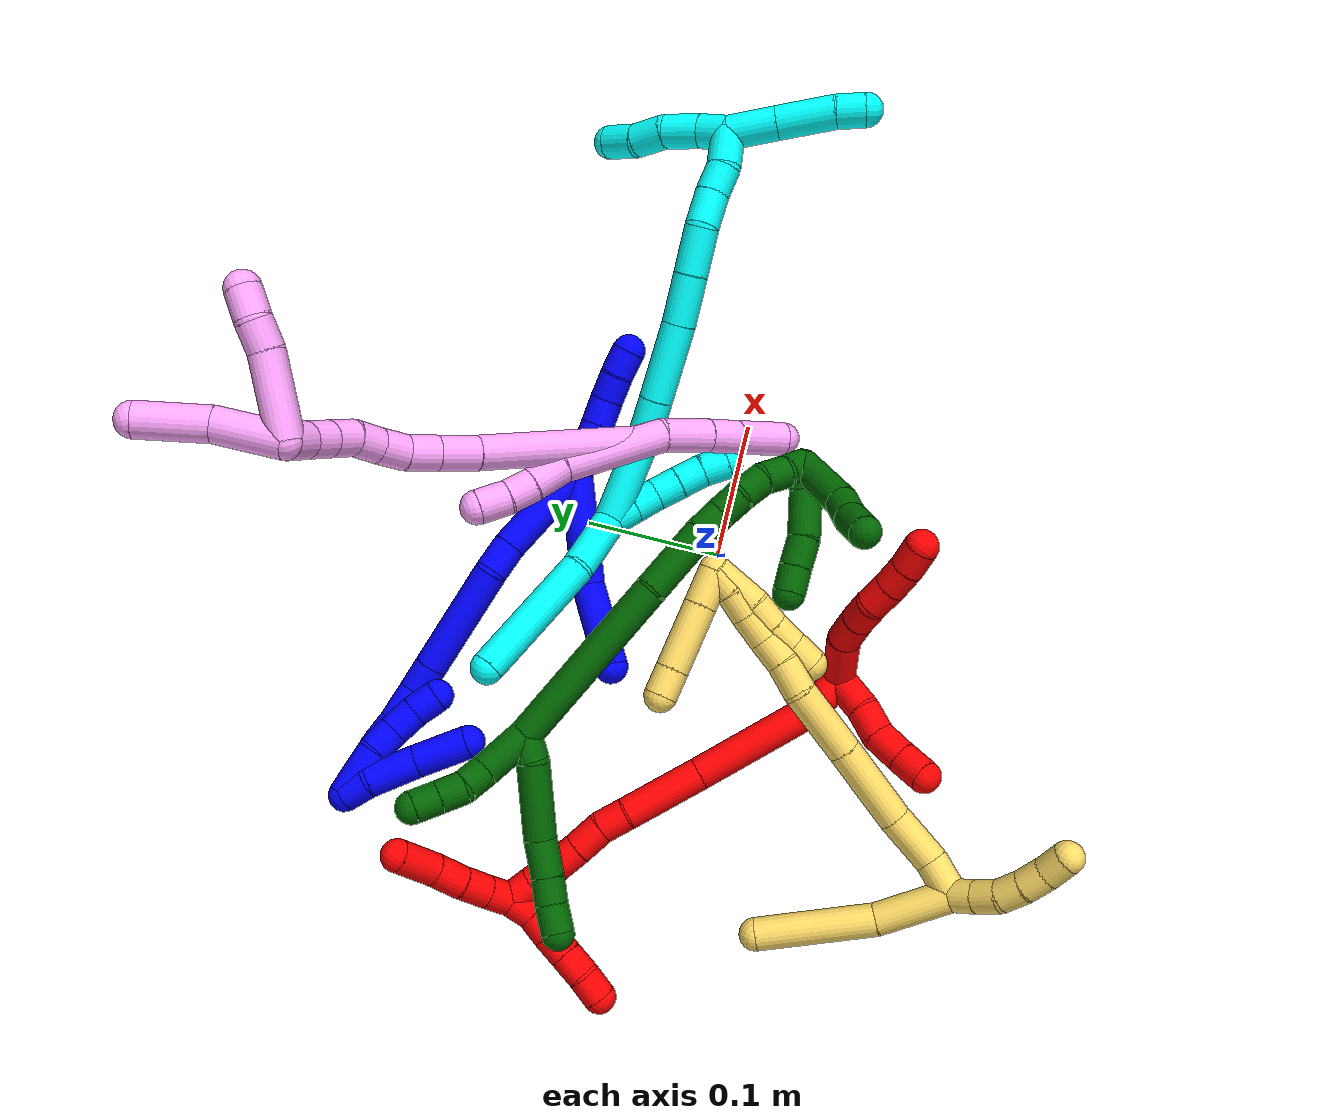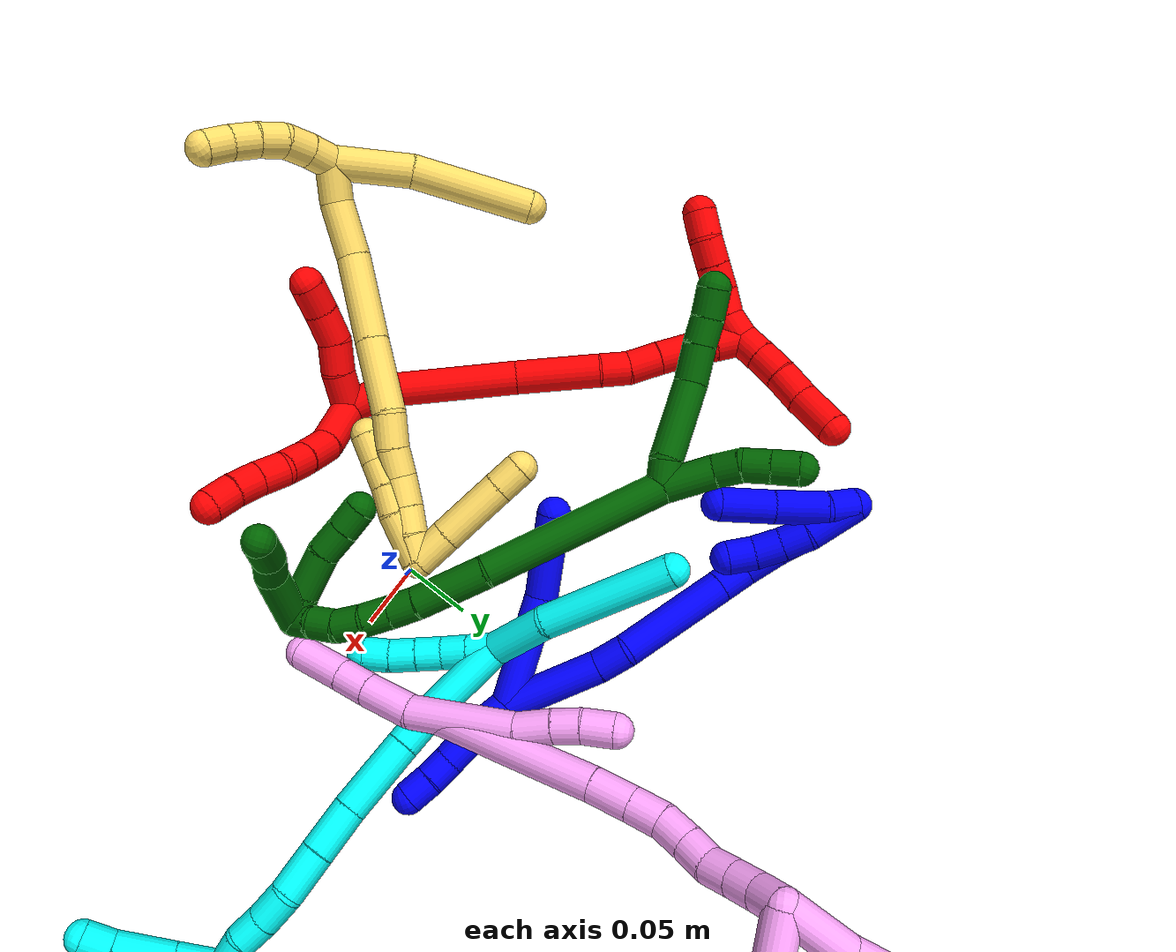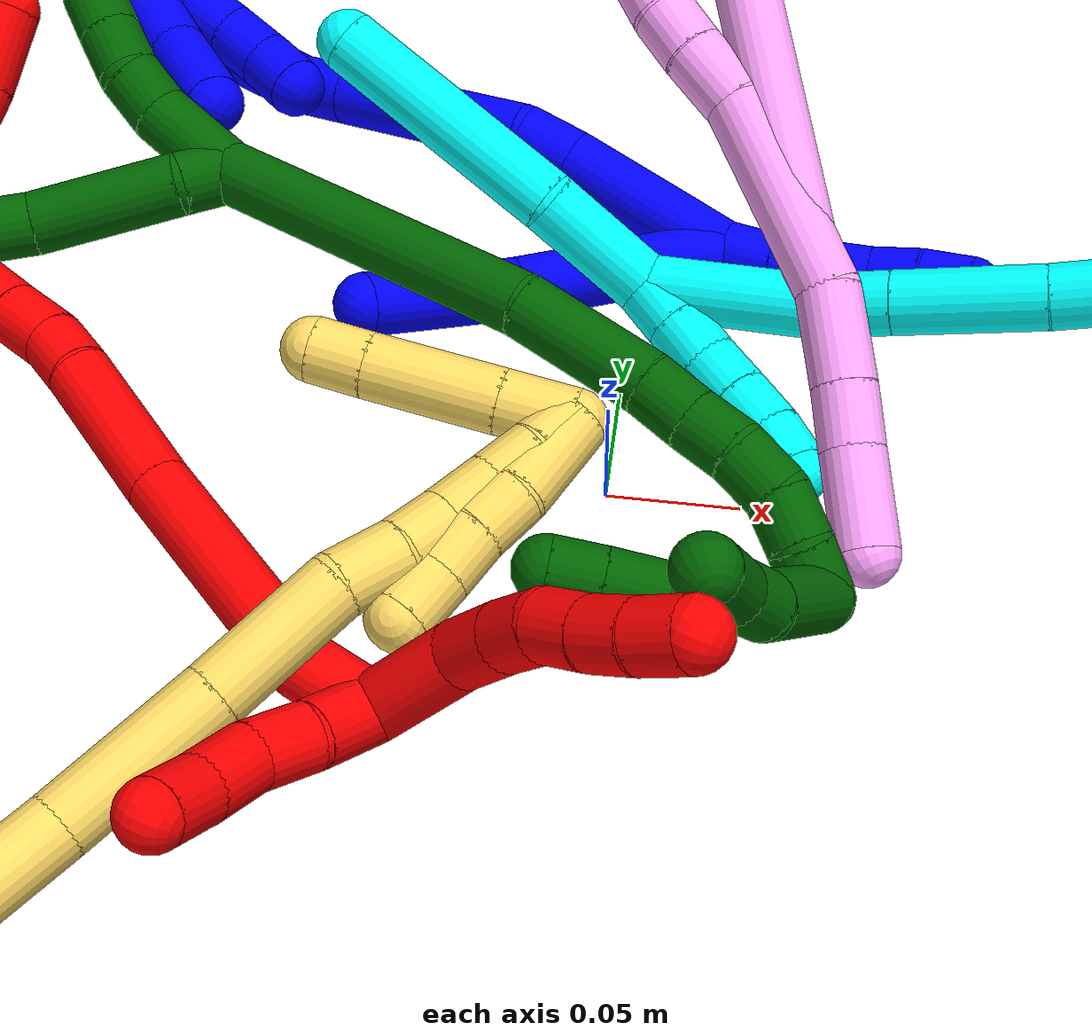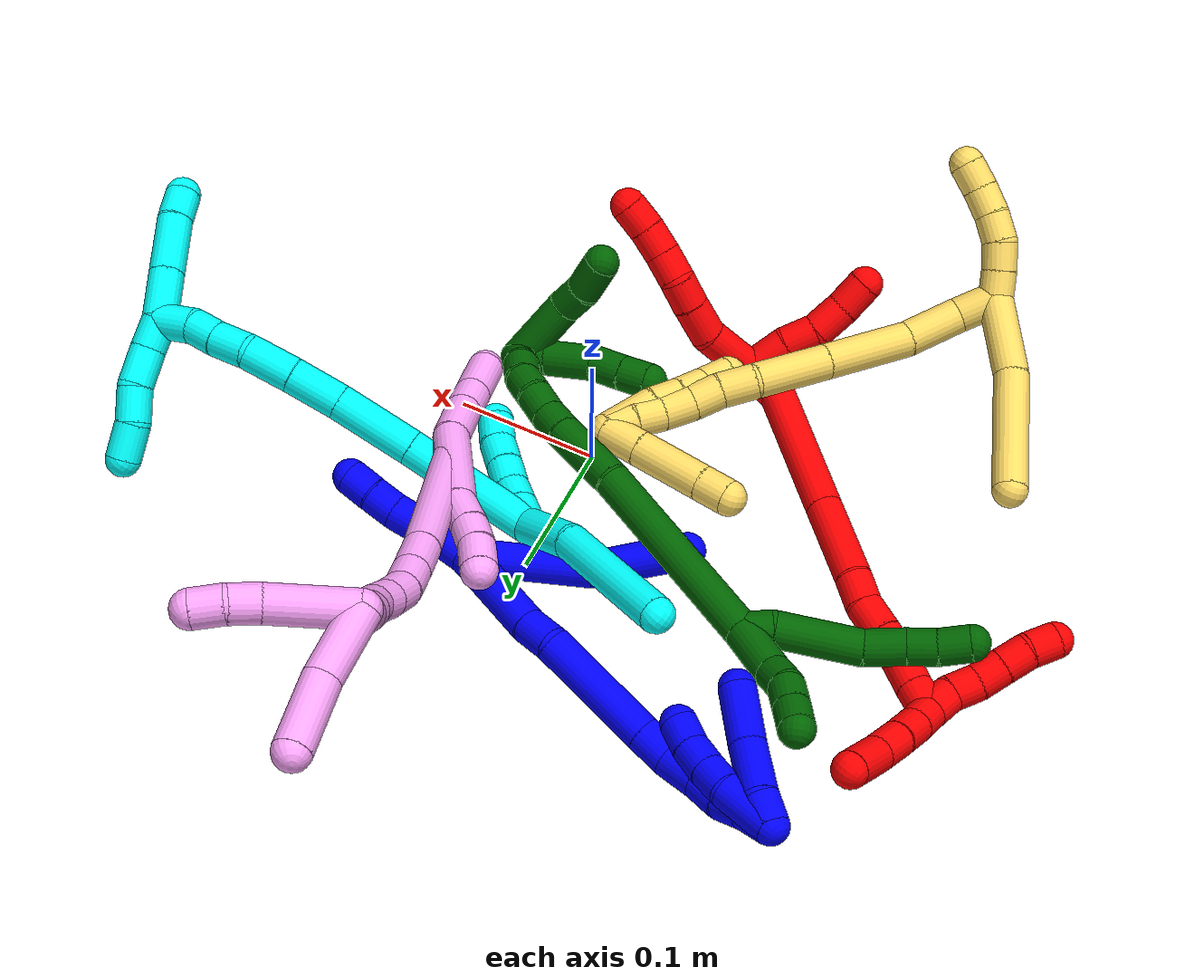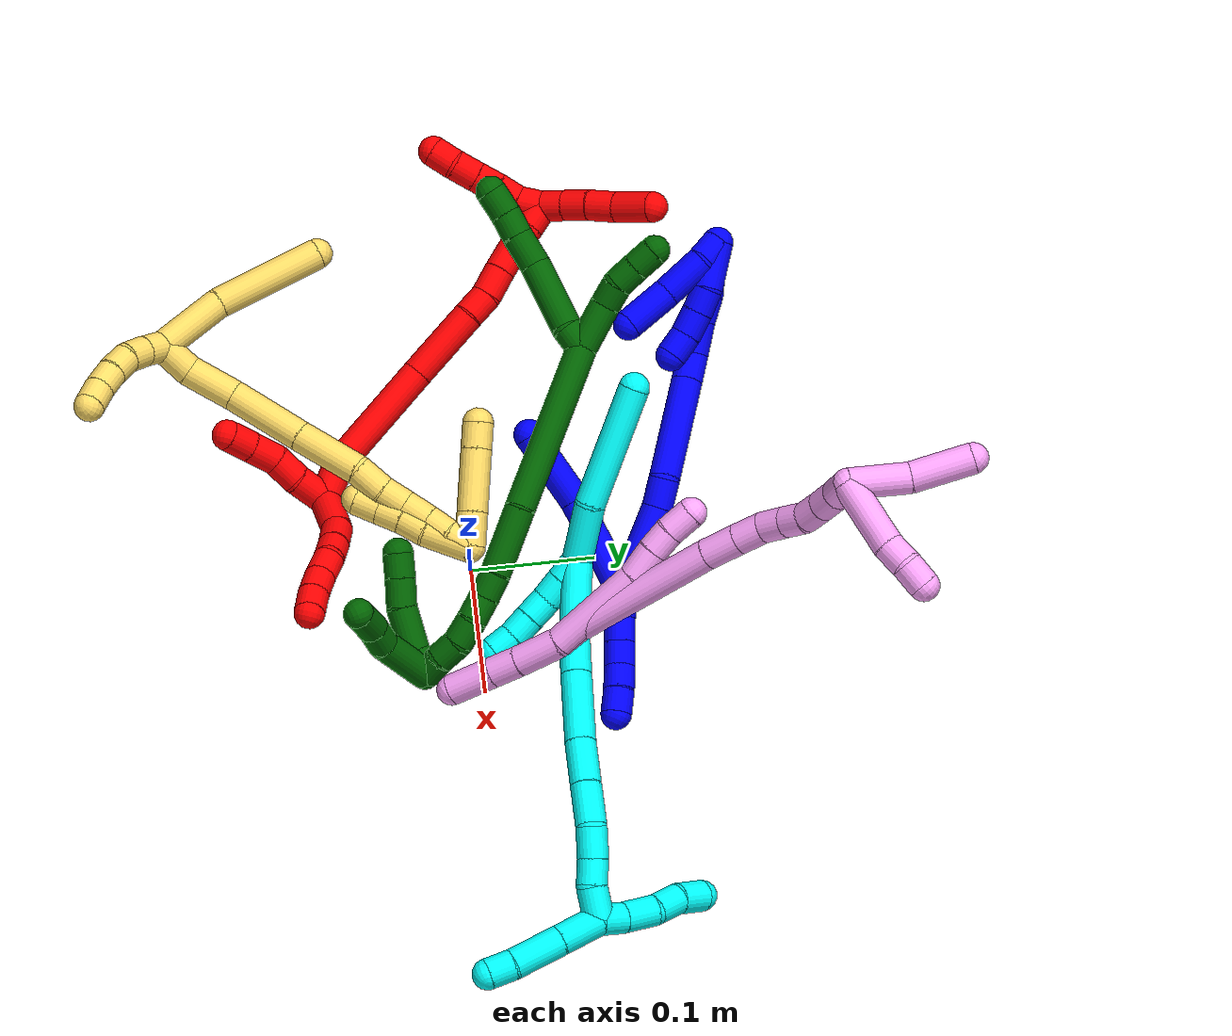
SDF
<sdf version="1.7">
 <world name="default">
  <plugin name="TubeGeneratorPlugin" filename="libtube_generator_plugin.so"/>
  <model name="photoneo_s_sensor">
   <static>1</static>
   <pose>0 0 2 1.57079 1.57079 3.14159</pose>
   <link name="link">
    <inertial><mass>0.1</mass></inertial>
    <sensor name="sensor" type="depth">
     <update_rate>30</update_rate>
     <camera>
      <horizontal_fov>1.22</horizontal_fov>
      <image><width>1920</width><height>1200</height><format>B8G8R8</format></image>
      <clip><near>0.1</near><far>4</far></clip>
      <depth_camera><output>points</output></depth_camera>
     </camera>
     <plugin name="camera_plugin" filename="libgazebo_ros_depth_camera.so">
      <baseline>0.2</baseline>
      <alwaysOn>1</alwaysOn>
      <updateRate>0.0</updateRate>
      <cameraName>camera_ir</cameraName>
      <imageTopicName>/camera/color/image_raw</imageTopicName>
      <cameraInfoTopicName>/camera/color/camera_info</cameraInfoTopicName>
      <depthImageTopicName>/camera/depth/image_raw</depthImageTopicName>
      <depthImageCameraInfoTopicName>/camera/depth/camera_info</depthImageCameraInfoTopicName>
      <pointCloudTopicName>/camera/depth/points</pointCloudTopicName>
      <frameName>fr_optical</frameName>
      <pointCloudCutoff>0.1</pointCloudCutoff>
      <pointCloudCutoffMax>2.0</pointCloudCutoffMax>
      <distortionK1>0</distortionK1>
      <distortionK2>0</distortionK2>
      <distortionK3>0</distortionK3>
      <distortionT1>0</distortionT1>
      <distortionT2>0</distortionT2>
      <CxPrime>0</CxPrime>
      <Cx>0</Cx>
      <Cy>0</Cy>
      <focalLength>0</focalLength>
      <hackBaseline>0</hackBaseline>
     </plugin>
    </sensor>
   </link>
  </model>
  <gravity>0 0 -9.8</gravity>
  <magnetic_field>6e-06 2.3e-05 -4.2e-05</magnetic_field>
  <atmosphere type="adiabatic"/>
  <physics name="default_physics" default="0" type="ode">
   <max_step_size>0.003</max_step_size>
   <real_time_factor>1</real_time_factor>
   <real_time_update_rate>1000</real_time_update_rate>
   <max_contacts>10000</max_contacts>
   <ode>
    <solver>
     <type>quick</type>
     <iters>100</iters>
     <sor>1.3</sor>
     <use_dynamic_moi_rescaling>0</use_dynamic_moi_rescaling>
    </solver>
    <constraints>
     <contact_max_correcting_vel>0</contact_max_correcting_vel>
     <contact_surface_layer>0.001</contact_surface_layer>
     <cfm>0</cfm>
     <erp>0.2</erp>
    </constraints>
   </ode>
  </physics>
  <scene><ambient>0.4 0.4 0.4 1</ambient><background>0.7 0.7 0.7 1</background><shadows>0</shadows></scene>
  <audio><device>default</device></audio>
  <spherical_coordinates>
   <surface_model>EARTH_WGS84</surface_model>
   <latitude_deg>0</latitude_deg>
   <longitude_deg>0</longitude_deg>
   <elevation>0</elevation>
   <heading_deg>0</heading_deg>
  </spherical_coordinates>
  <model name="bin">
   <static>1</static>
   <link name="bottom">
    <collision name="collision-bottom">
     <pose>0 0 -0.01 0 -0 0</pose>
     <geometry><box><size>0.8 0.6 0.02</size></box></geometry>
     <surface>
      <friction><ode><mu>100</mu><mu2>100</mu2></ode></friction>
      <contact><collide_bitmask>65535</collide_bitmask></contact>
     </surface>
    </collision>
   </link>
   <link name="west_wall">
    <collision name="collision-west_wall">
     <pose>-0.41 0 0.1 0 -0 0</pose>
     <geometry><box><size>0.02 0.6 0.2</size></box></geometry>
     <surface>
      <friction><ode><mu>100</mu><mu2>100</mu2></ode></friction>
      <contact><collide_bitmask>65535</collide_bitmask></contact>
     </surface>
    </collision>
   </link>
   <link name="east_wall">
    <collision name="collision-east_wall">
     <pose>0.41 0 0.1 0 -0 0</pose>
     <geometry><box><size>0.02 0.6 0.2</size></box></geometry>
     <surface>
      <friction><ode><mu>100</mu><mu2>100</mu2></ode></friction>
      <contact><collide_bitmask>65535</collide_bitmask></contact>
     </surface>
    </collision>
   </link>
   <link name="south_wall">
    <collision name="collision-south_wall">
     <pose>0 -0.31 0.1 0 -0 0</pose>
     <geometry><box><size>0.8 0.02 0.2</size></box></geometry>
     <surface>
      <friction><ode><mu>100</mu><mu2>100</mu2></ode></friction>
      <contact><collide_bitmask>65535</collide_bitmask></contact>
     </surface>
    </collision>
   </link>
   <link name="north_wall">
    <collision name="collision-north_wall">
     <pose>0 0.31 0.1 0 -0 0</pose>
     <geometry><box><size>0.8 0.02 0.2</size></box></geometry>
     <surface>
      <friction><ode><mu>100</mu><mu2>100</mu2></ode></friction>
      <contact><collide_bitmask>65535</collide_bitmask></contact>
     </surface>
    </collision>
   </link>
  </model>
  <model name="1">
   <static>0</static>
   <link name="1">
    <collision name="collision-cylinder-e_1_2_8">
     <pose>-0.031897 0.00626 0.027289 -0.225494 -0.850404 0.102455</pose>
     <geometry><cylinder><radius>0.0125</radius><length>0.084883</length></cylinder></geometry>
     <surface>
      <friction><ode><mu>1.16</mu><mu2>1.16</mu2><slip1>0</slip1><slip2>0</slip2></ode></friction>
      <contact><ode><kp>1e+06</kp><kd>1</kd><max_vel>0</max_vel><min_depth>0.001</min_depth></ode></contact>
     </surface>
    </collision>
    <visual name="visual-cylinder-e_1_2_8">
     <pose>-0.031897 0.00626 0.027289 -0.225494 -0.850404 0.102455</pose>
     <geometry><cylinder><radius>0.0125</radius><length>0.084883</length></cylinder></geometry>
     <material><ambient>0 0 1 1</ambient></material>
    </visual>
    <collision name="collision-cylinder-e_2_8_6">
     <pose>-0.09135 0.007956 0.071307 0.266302 -1.00913 -0.14767</pose>
     <geometry><cylinder><radius>0.0125</radius><length>0.065117</length></cylinder></geometry>
     <surface>
      <friction><ode><mu>1.16</mu><mu2>1.16</mu2><slip1>0</slip1><slip2>0</slip2></ode></friction>
      <contact><ode><kp>1e+06</kp><kd>1</kd><max_vel>0</max_vel><min_depth>0.001</min_depth></ode></contact>
     </surface>
    </collision>
    <visual name="visual-cylinder-e_2_8_6">
     <pose>-0.09135 0.007956 0.071307 0.266302 -1.00913 -0.14767</pose>
     <geometry><cylinder><radius>0.0125</radius><length>0.065117</length></cylinder></geometry>
     <material><ambient>0 0 1 1</ambient></material>
    </visual>
    <collision name="collision-cylinder-e_1_2_9">
     <pose>0.00269 -0.001166 -0.009561 3.02025 0.272355 2.30704</pose>
     <geometry><cylinder><radius>0.0125</radius><length>0.02</length></cylinder></geometry>
     <surface>
      <friction><ode><mu>1.16</mu><mu2>1.16</mu2><slip1>0</slip1><slip2>0</slip2></ode></friction>
      <contact><ode><kp>1e+06</kp><kd>1</kd><max_vel>0</max_vel><min_depth>0.001</min_depth></ode></contact>
     </surface>
    </collision>
    <visual name="visual-cylinder-e_1_2_9">
     <pose>0.00269 -0.001166 -0.009561 3.02025 0.272355 2.30704</pose>
     <geometry><cylinder><radius>0.0125</radius><length>0.02</length></cylinder></geometry>
     <material><ambient>0 0 1 1</ambient></material>
    </visual>
    <collision name="collision-cylinder-e_2_9_10">
     <pose>0.009068 -0.004043 -0.028257 2.9564 0.377685 2.237</pose>
     <geometry><cylinder><radius>0.0125</radius><length>0.02</length></cylinder></geometry>
     <surface>
      <friction><ode><mu>1.16</mu><mu2>1.16</mu2><slip1>0</slip1><slip2>0</slip2></ode></friction>
      <contact><ode><kp>1e+06</kp><kd>1</kd><max_vel>0</max_vel><min_depth>0.001</min_depth></ode></contact>
     </surface>
    </collision>
    <visual name="visual-cylinder-e_2_9_10">
     <pose>0.009068 -0.004043 -0.028257 2.9564 0.377685 2.237</pose>
     <geometry><cylinder><radius>0.0125</radius><length>0.02</length></cylinder></geometry>
     <material><ambient>0 0 1 1</ambient></material>
    </visual>
    <collision name="collision-cylinder-e_3_10_11">
     <pose>0.016504 -0.007547 -0.04649 2.94709 0.384281 2.21192</pose>
     <geometry><cylinder><radius>0.0125</radius><length>0.02</length></cylinder></geometry>
     <surface>
      <friction><ode><mu>1.16</mu><mu2>1.16</mu2><slip1>0</slip1><slip2>0</slip2></ode></friction>
      <contact><ode><kp>1e+06</kp><kd>1</kd><max_vel>0</max_vel><min_depth>0.001</min_depth></ode></contact>
     </surface>
    </collision>
    <visual name="visual-cylinder-e_3_10_11">
     <pose>0.016504 -0.007547 -0.04649 2.94709 0.384281 2.21192</pose>
     <geometry><cylinder><radius>0.0125</radius><length>0.02</length></cylinder></geometry>
     <material><ambient>0 0 1 1</ambient></material>
    </visual>
    <collision name="collision-cylinder-e_4_11_12">
     <pose>0.023421 -0.012743 -0.064438 2.77445 0.322378 1.43855</pose>
     <geometry><cylinder><radius>0.0125</radius><length>0.02</length></cylinder></geometry>
     <surface>
      <friction><ode><mu>1.16</mu><mu2>1.16</mu2><slip1>0</slip1><slip2>0</slip2></ode></friction>
      <contact><ode><kp>1e+06</kp><kd>1</kd><max_vel>0</max_vel><min_depth>0.001</min_depth></ode></contact>
     </surface>
    </collision>
    <visual name="visual-cylinder-e_4_11_12">
     <pose>0.023421 -0.012743 -0.064438 2.77445 0.322378 1.43855</pose>
     <geometry><cylinder><radius>0.0125</radius><length>0.02</length></cylinder></geometry>
     <material><ambient>0 0 1 1</ambient></material>
    </visual>
    <collision name="collision-cylinder-e_5_12_5">
     <pose>0.029197 -0.018583 -0.082633 2.88656 0.263747 1.60478</pose>
     <geometry><cylinder><radius>0.0125</radius><length>0.02</length></cylinder></geometry>
     <surface>
      <friction><ode><mu>1.16</mu><mu2>1.16</mu2><slip1>0</slip1><slip2>0</slip2></ode></friction>
      <contact><ode><kp>1e+06</kp><kd>1</kd><max_vel>0</max_vel><min_depth>0.001</min_depth></ode></contact>
     </surface>
    </collision>
    <visual name="visual-cylinder-e_5_12_5">
     <pose>0.029197 -0.018583 -0.082633 2.88656 0.263747 1.60478</pose>
     <geometry><cylinder><radius>0.0125</radius><length>0.02</length></cylinder></geometry>
     <material><ambient>0 0 1 1</ambient></material>
    </visual>
    <collision name="collision-cylinder-e_1_2_13">
     <pose>-0.000793 -0.000786 0.037102 0.021182 -0.021372 -0.000226</pose>
     <geometry><cylinder><radius>0.0125</radius><length>0.074237</length></cylinder></geometry>
     <surface>
      <friction><ode><mu>1.16</mu><mu2>1.16</mu2><slip1>0</slip1><slip2>0</slip2></ode></friction>
      <contact><ode><kp>1e+06</kp><kd>1</kd><max_vel>0</max_vel><min_depth>0.001</min_depth></ode></contact>
     </surface>
    </collision>
    <visual name="visual-cylinder-e_1_2_13">
     <pose>-0.000793 -0.000786 0.037102 0.021182 -0.021372 -0.000226</pose>
     <geometry><cylinder><radius>0.0125</radius><length>0.074237</length></cylinder></geometry>
     <material><ambient>0 0 1 1</ambient></material>
    </visual>
    <collision name="collision-cylinder-e_2_13_14">
     <pose>-0.003511 -0.002489 0.085995 0.077599 -0.161309 -0.006275</pose>
     <geometry><cylinder><radius>0.0125</radius><length>0.023967</length></cylinder></geometry>
     <surface>
      <friction><ode><mu>1.16</mu><mu2>1.16</mu2><slip1>0</slip1><slip2>0</slip2></ode></friction>
      <contact><ode><kp>1e+06</kp><kd>1</kd><max_vel>0</max_vel><min_depth>0.001</min_depth></ode></contact>
     </surface>
    </collision>
    <visual name="visual-cylinder-e_2_13_14">
     <pose>-0.003511 -0.002489 0.085995 0.077599 -0.161309 -0.006275</pose>
     <geometry><cylinder><radius>0.0125</radius><length>0.023967</length></cylinder></geometry>
     <material><ambient>0 0 1 1</ambient></material>
    </visual>
    <collision name="collision-cylinder-e_3_14_15">
     <pose>-0.012034 0.007093 0.138141 -0.254527 -0.156946 0.020123</pose>
     <geometry><cylinder><radius>0.0125</radius><length>0.084432</length></cylinder></geometry>
     <surface>
      <friction><ode><mu>1.16</mu><mu2>1.16</mu2><slip1>0</slip1><slip2>0</slip2></ode></friction>
      <contact><ode><kp>1e+06</kp><kd>1</kd><max_vel>0</max_vel><min_depth>0.001</min_depth></ode></contact>
     </surface>
    </collision>
    <visual name="visual-cylinder-e_3_14_15">
     <pose>-0.012034 0.007093 0.138141 -0.254527 -0.156946 0.020123</pose>
     <geometry><cylinder><radius>0.0125</radius><length>0.084432</length></cylinder></geometry>
     <material><ambient>0 0 1 1</ambient></material>
    </visual>
    <collision name="collision-cylinder-e_4_15_16">
     <pose>-0.020542 0.02046 0.189818 -0.2481 -0.162034 0.020248</pose>
     <geometry><cylinder><radius>0.0125</radius><length>0.023671</length></cylinder></geometry>
     <surface>
      <friction><ode><mu>1.16</mu><mu2>1.16</mu2><slip1>0</slip1><slip2>0</slip2></ode></friction>
      <contact><ode><kp>1e+06</kp><kd>1</kd><max_vel>0</max_vel><min_depth>0.001</min_depth></ode></contact>
     </surface>
    </collision>
    <visual name="visual-cylinder-e_4_15_16">
     <pose>-0.020542 0.02046 0.189818 -0.2481 -0.162034 0.020248</pose>
     <geometry><cylinder><radius>0.0125</radius><length>0.023671</length></cylinder></geometry>
     <material><ambient>0 0 1 1</ambient></material>
    </visual>
    <collision name="collision-cylinder-e_5_16_17">
     <pose>-0.025143 0.022345 0.214704 0.072396 -0.195391 -0.007098</pose>
     <geometry><cylinder><radius>0.0125</radius><length>0.027727</length></cylinder></geometry>
     <surface>
      <friction><ode><mu>1.16</mu><mu2>1.16</mu2><slip1>0</slip1><slip2>0</slip2></ode></friction>
      <contact><ode><kp>1e+06</kp><kd>1</kd><max_vel>0</max_vel><min_depth>0.001</min_depth></ode></contact>
     </surface>
    </collision>
    <visual name="visual-cylinder-e_5_16_17">
     <pose>-0.025143 0.022345 0.214704 0.072396 -0.195391 -0.007098</pose>
     <geometry><cylinder><radius>0.0125</radius><length>0.027727</length></cylinder></geometry>
     <material><ambient>0 0 1 1</ambient></material>
    </visual>
    <collision name="collision-cylinder-e_6_17_18">
     <pose>-0.028946 0.020682 0.238854 0.064018 -0.104382 -0.003345</pose>
     <geometry><cylinder><radius>0.0125</radius><length>0.02133</length></cylinder></geometry>
     <surface>
      <friction><ode><mu>1.16</mu><mu2>1.16</mu2><slip1>0</slip1><slip2>0</slip2></ode></friction>
      <contact><ode><kp>1e+06</kp><kd>1</kd><max_vel>0</max_vel><min_depth>0.001</min_depth></ode></contact>
     </surface>
    </collision>
    <visual name="visual-cylinder-e_6_17_18">
     <pose>-0.028946 0.020682 0.238854 0.064018 -0.104382 -0.003345</pose>
     <geometry><cylinder><radius>0.0125</radius><length>0.02133</length></cylinder></geometry>
     <material><ambient>0 0 1 1</ambient></material>
    </visual>
    <collision name="collision-cylinder-e_7_18_19">
     <pose>-0.033163 0.017098 0.258624 0.306448 -0.311859 -0.048546</pose>
     <geometry><cylinder><radius>0.0125</radius><length>0.020243</length></cylinder></geometry>
     <surface>
      <friction><ode><mu>1.16</mu><mu2>1.16</mu2><slip1>0</slip1><slip2>0</slip2></ode></friction>
      <contact><ode><kp>1e+06</kp><kd>1</kd><max_vel>0</max_vel><min_depth>0.001</min_depth></ode></contact>
     </surface>
    </collision>
    <visual name="visual-cylinder-e_7_18_19">
     <pose>-0.033163 0.017098 0.258624 0.306448 -0.311859 -0.048546</pose>
     <geometry><cylinder><radius>0.0125</radius><length>0.020243</length></cylinder></geometry>
     <material><ambient>0 0 1 1</ambient></material>
    </visual>
    <collision name="collision-cylinder-e_8_19_1">
     <pose>-0.038061 0.010159 0.279179 0.340834 -0.147508 -0.025429</pose>
     <geometry><cylinder><radius>0.0125</radius><length>0.024394</length></cylinder></geometry>
     <surface>
      <friction><ode><mu>1.16</mu><mu2>1.16</mu2><slip1>0</slip1><slip2>0</slip2></ode></friction>
      <contact><ode><kp>1e+06</kp><kd>1</kd><max_vel>0</max_vel><min_depth>0.001</min_depth></ode></contact>
     </surface>
    </collision>
    <visual name="visual-cylinder-e_8_19_1">
     <pose>-0.038061 0.010159 0.279179 0.340834 -0.147508 -0.025429</pose>
     <geometry><cylinder><radius>0.0125</radius><length>0.024394</length></cylinder></geometry>
     <material><ambient>0 0 1 1</ambient></material>
    </visual>
    <collision name="collision-cylinder-e_1_1_20">
     <pose>-0.042878 0.00393 0.280959 2.91649 -0.298299 -1.85181</pose>
     <geometry><cylinder><radius>0.0125</radius><length>0.020585</length></cylinder></geometry>
     <surface>
      <friction><ode><mu>1.16</mu><mu2>1.16</mu2><slip1>0</slip1><slip2>0</slip2></ode></friction>
      <contact><ode><kp>1e+06</kp><kd>1</kd><max_vel>0</max_vel><min_depth>0.001</min_depth></ode></contact>
     </surface>
    </collision>
    <visual name="visual-cylinder-e_1_1_20">
     <pose>-0.042878 0.00393 0.280959 2.91649 -0.298299 -1.85181</pose>
     <geometry><cylinder><radius>0.0125</radius><length>0.020585</length></cylinder></geometry>
     <material><ambient>0 0 1 1</ambient></material>
    </visual>
    <collision name="collision-cylinder-e_2_20_21">
     <pose>-0.053857 0.002186 0.253871 -3.11577 -0.426525 3.02249</pose>
     <geometry><cylinder><radius>0.0125</radius><length>0.038453</length></cylinder></geometry>
     <surface>
      <friction><ode><mu>1.16</mu><mu2>1.16</mu2><slip1>0</slip1><slip2>0</slip2></ode></friction>
      <contact><ode><kp>1e+06</kp><kd>1</kd><max_vel>0</max_vel><min_depth>0.001</min_depth></ode></contact>
     </surface>
    </collision>
    <visual name="visual-cylinder-e_2_20_21">
     <pose>-0.053857 0.002186 0.253871 -3.11577 -0.426525 3.02249</pose>
     <geometry><cylinder><radius>0.0125</radius><length>0.038453</length></cylinder></geometry>
     <material><ambient>0 0 1 1</ambient></material>
    </visual>
    <collision name="collision-cylinder-e_3_21_4">
     <pose>-0.070974 -0.000227 0.218281 2.9845 -0.463799 -2.49816</pose>
     <geometry><cylinder><radius>0.0125</radius><length>0.040962</length></cylinder></geometry>
     <surface>
      <friction><ode><mu>1.16</mu><mu2>1.16</mu2><slip1>0</slip1><slip2>0</slip2></ode></friction>
      <contact><ode><kp>1e+06</kp><kd>1</kd><max_vel>0</max_vel><min_depth>0.001</min_depth></ode></contact>
     </surface>
    </collision>
    <visual name="visual-cylinder-e_3_21_4">
     <pose>-0.070974 -0.000227 0.218281 2.9845 -0.463799 -2.49816</pose>
     <geometry><cylinder><radius>0.0125</radius><length>0.040962</length></cylinder></geometry>
     <material><ambient>0 0 1 1</ambient></material>
    </visual>
    <collision name="collision-cylinder-e_1_1_22">
     <pose>-0.036467 0.005544 0.271523 3.11102 0.176086 2.79859</pose>
     <geometry><cylinder><radius>0.0125</radius><length>0.038668</length></cylinder></geometry>
     <surface>
      <friction><ode><mu>1.16</mu><mu2>1.16</mu2><slip1>0</slip1><slip2>0</slip2></ode></friction>
      <contact><ode><kp>1e+06</kp><kd>1</kd><max_vel>0</max_vel><min_depth>0.001</min_depth></ode></contact>
     </surface>
    </collision>
    <visual name="visual-cylinder-e_1_1_22">
     <pose>-0.036467 0.005544 0.271523 3.11102 0.176086 2.79859</pose>
     <geometry><cylinder><radius>0.0125</radius><length>0.038668</length></cylinder></geometry>
     <material><ambient>0 0 1 1</ambient></material>
    </visual>
    <collision name="collision-cylinder-e_2_22_23">
     <pose>-0.032998 0.006284 0.242539 -3.00964 0.008129 -0.122872</pose>
     <geometry><cylinder><radius>0.0125</radius><length>0.020091</length></cylinder></geometry>
     <surface>
      <friction><ode><mu>1.16</mu><mu2>1.16</mu2><slip1>0</slip1><slip2>0</slip2></ode></friction>
      <contact><ode><kp>1e+06</kp><kd>1</kd><max_vel>0</max_vel><min_depth>0.001</min_depth></ode></contact>
     </surface>
    </collision>
    <visual name="visual-cylinder-e_2_22_23">
     <pose>-0.032998 0.006284 0.242539 -3.00964 0.008129 -0.122872</pose>
     <geometry><cylinder><radius>0.0125</radius><length>0.020091</length></cylinder></geometry>
     <material><ambient>0 0 1 1</ambient></material>
    </visual>
    <collision name="collision-cylinder-e_3_23_24">
     <pose>-0.033605 0.008537 0.222134 -3.05266 -0.06556 1.27026</pose>
     <geometry><cylinder><radius>0.0125</radius><length>0.021022</length></cylinder></geometry>
     <surface>
      <friction><ode><mu>1.16</mu><mu2>1.16</mu2><slip1>0</slip1><slip2>0</slip2></ode></friction>
      <contact><ode><kp>1e+06</kp><kd>1</kd><max_vel>0</max_vel><min_depth>0.001</min_depth></ode></contact>
     </surface>
    </collision>
    <visual name="visual-cylinder-e_3_23_24">
     <pose>-0.033605 0.008537 0.222134 -3.05266 -0.06556 1.27026</pose>
     <geometry><cylinder><radius>0.0125</radius><length>0.021022</length></cylinder></geometry>
     <material><ambient>0 0 1 1</ambient></material>
    </visual>
    <collision name="collision-cylinder-e_4_24_3">
     <pose>-0.036473 0.009125 0.201821 3.10679 -0.217278 -2.82515</pose>
     <geometry><cylinder><radius>0.0125</radius><length>0.020219</length></cylinder></geometry>
     <surface>
      <friction><ode><mu>1.16</mu><mu2>1.16</mu2><slip1>0</slip1><slip2>0</slip2></ode></friction>
      <contact><ode><kp>1e+06</kp><kd>1</kd><max_vel>0</max_vel><min_depth>0.001</min_depth></ode></contact>
     </surface>
    </collision>
    <visual name="visual-cylinder-e_4_24_3">
     <pose>-0.036473 0.009125 0.201821 3.10679 -0.217278 -2.82515</pose>
     <geometry><cylinder><radius>0.0125</radius><length>0.020219</length></cylinder></geometry>
     <material><ambient>0 0 1 1</ambient></material>
    </visual>
    <collision name="collision-sphere-3">
     <pose>-0.038652 0.008782 0.191955 0 -0 0</pose>
     <geometry><sphere><radius>0.0125</radius></sphere></geometry>
     <surface>
      <friction><ode><mu>1.16</mu><mu2>1.16</mu2><slip1>0</slip1><slip2>0</slip2></ode></friction>
      <contact><ode><kp>1e+06</kp><kd>1</kd><max_vel>0</max_vel><min_depth>0.001</min_depth></ode></contact>
     </surface>
    </collision>
    <visual name="visual-sphere-3">
     <pose>-0.038652 0.008782 0.191955 0 -0 0</pose>
     <geometry><sphere><radius>0.0125</radius></sphere></geometry>
     <material><ambient>0 0 1 1</ambient></material>
    </visual>
    <collision name="collision-sphere-24">
     <pose>-0.034294 0.009469 0.211687 0 -0 0</pose>
     <geometry><sphere><radius>0.0125</radius></sphere></geometry>
     <surface>
      <friction><ode><mu>1.16</mu><mu2>1.16</mu2><slip1>0</slip1><slip2>0</slip2></ode></friction>
      <contact><ode><kp>1e+06</kp><kd>1</kd><max_vel>0</max_vel><min_depth>0.001</min_depth></ode></contact>
     </surface>
    </collision>
    <visual name="visual-sphere-24">
     <pose>-0.034294 0.009469 0.211687 0 -0 0</pose>
     <geometry><sphere><radius>0.0125</radius></sphere></geometry>
     <material><ambient>0 0 1 1</ambient></material>
    </visual>
    <collision name="collision-sphere-23">
     <pose>-0.032916 0.007606 0.232581 0 -0 0</pose>
     <geometry><sphere><radius>0.0125</radius></sphere></geometry>
     <surface>
      <friction><ode><mu>1.16</mu><mu2>1.16</mu2><slip1>0</slip1><slip2>0</slip2></ode></friction>
      <contact><ode><kp>1e+06</kp><kd>1</kd><max_vel>0</max_vel><min_depth>0.001</min_depth></ode></contact>
     </surface>
    </collision>
    <visual name="visual-sphere-23">
     <pose>-0.032916 0.007606 0.232581 0 -0 0</pose>
     <geometry><sphere><radius>0.0125</radius></sphere></geometry>
     <material><ambient>0 0 1 1</ambient></material>
    </visual>
    <collision name="collision-sphere-22">
     <pose>-0.03308 0.004962 0.252497 0 -0 0</pose>
     <geometry><sphere><radius>0.0125</radius></sphere></geometry>
     <surface>
      <friction><ode><mu>1.16</mu><mu2>1.16</mu2><slip1>0</slip1><slip2>0</slip2></ode></friction>
      <contact><ode><kp>1e+06</kp><kd>1</kd><max_vel>0</max_vel><min_depth>0.001</min_depth></ode></contact>
     </surface>
    </collision>
    <visual name="visual-sphere-22">
     <pose>-0.03308 0.004962 0.252497 0 -0 0</pose>
     <geometry><sphere><radius>0.0125</radius></sphere></geometry>
     <material><ambient>0 0 1 1</ambient></material>
    </visual>
    <collision name="collision-sphere-4">
     <pose>-0.080136 -0.003093 0.200189 0 -0 0</pose>
     <geometry><sphere><radius>0.0125</radius></sphere></geometry>
     <surface>
      <friction><ode><mu>1.16</mu><mu2>1.16</mu2><slip1>0</slip1><slip2>0</slip2></ode></friction>
      <contact><ode><kp>1e+06</kp><kd>1</kd><max_vel>0</max_vel><min_depth>0.001</min_depth></ode></contact>
     </surface>
    </collision>
    <visual name="visual-sphere-4">
     <pose>-0.080136 -0.003093 0.200189 0 -0 0</pose>
     <geometry><sphere><radius>0.0125</radius></sphere></geometry>
     <material><ambient>0 0 1 1</ambient></material>
    </visual>
    <collision name="collision-sphere-21">
     <pose>-0.061812 0.002638 0.236373 0 -0 0</pose>
     <geometry><sphere><radius>0.0125</radius></sphere></geometry>
     <surface>
      <friction><ode><mu>1.16</mu><mu2>1.16</mu2><slip1>0</slip1><slip2>0</slip2></ode></friction>
      <contact><ode><kp>1e+06</kp><kd>1</kd><max_vel>0</max_vel><min_depth>0.001</min_depth></ode></contact>
     </surface>
    </collision>
    <visual name="visual-sphere-21">
     <pose>-0.061812 0.002638 0.236373 0 -0 0</pose>
     <geometry><sphere><radius>0.0125</radius></sphere></geometry>
     <material><ambient>0 0 1 1</ambient></material>
    </visual>
    <collision name="collision-sphere-20">
     <pose>-0.045903 0.001734 0.27137 0 -0 0</pose>
     <geometry><sphere><radius>0.0125</radius></sphere></geometry>
     <surface>
      <friction><ode><mu>1.16</mu><mu2>1.16</mu2><slip1>0</slip1><slip2>0</slip2></ode></friction>
      <contact><ode><kp>1e+06</kp><kd>1</kd><max_vel>0</max_vel><min_depth>0.001</min_depth></ode></contact>
     </surface>
    </collision>
    <visual name="visual-sphere-20">
     <pose>-0.045903 0.001734 0.27137 0 -0 0</pose>
     <geometry><sphere><radius>0.0125</radius></sphere></geometry>
     <material><ambient>0 0 1 1</ambient></material>
    </visual>
    <collision name="collision-sphere-11">
     <pose>0.020253 -0.009338 -0.055585 0 -0 0</pose>
     <geometry><sphere><radius>0.0125</radius></sphere></geometry>
     <surface>
      <friction><ode><mu>1.16</mu><mu2>1.16</mu2><slip1>0</slip1><slip2>0</slip2></ode></friction>
      <contact><ode><kp>1e+06</kp><kd>1</kd><max_vel>0</max_vel><min_depth>0.001</min_depth></ode></contact>
     </surface>
    </collision>
    <visual name="visual-sphere-11">
     <pose>0.020253 -0.009338 -0.055585 0 -0 0</pose>
     <geometry><sphere><radius>0.0125</radius></sphere></geometry>
     <material><ambient>0 0 1 1</ambient></material>
    </visual>
    <collision name="collision-sphere-10">
     <pose>0.012755 -0.005755 -0.037394 0 -0 0</pose>
     <geometry><sphere><radius>0.0125</radius></sphere></geometry>
     <surface>
      <friction><ode><mu>1.16</mu><mu2>1.16</mu2><slip1>0</slip1><slip2>0</slip2></ode></friction>
      <contact><ode><kp>1e+06</kp><kd>1</kd><max_vel>0</max_vel><min_depth>0.001</min_depth></ode></contact>
     </surface>
    </collision>
    <visual name="visual-sphere-10">
     <pose>0.012755 -0.005755 -0.037394 0 -0 0</pose>
     <geometry><sphere><radius>0.0125</radius></sphere></geometry>
     <material><ambient>0 0 1 1</ambient></material>
    </visual>
    <collision name="collision-sphere-6">
     <pose>-0.118906 0.003393 0.088037 0 -0 0</pose>
     <geometry><sphere><radius>0.0125</radius></sphere></geometry>
     <surface>
      <friction><ode><mu>1.16</mu><mu2>1.16</mu2><slip1>0</slip1><slip2>0</slip2></ode></friction>
      <contact><ode><kp>1e+06</kp><kd>1</kd><max_vel>0</max_vel><min_depth>0.001</min_depth></ode></contact>
     </surface>
    </collision>
    <visual name="visual-sphere-6">
     <pose>-0.118906 0.003393 0.088037 0 -0 0</pose>
     <geometry><sphere><radius>0.0125</radius></sphere></geometry>
     <material><ambient>0 0 1 1</ambient></material>
    </visual>
    <collision name="collision-sphere-9">
     <pose>0.00538 -0.002332 -0.019121 0 -0 0</pose>
     <geometry><sphere><radius>0.0125</radius></sphere></geometry>
     <surface>
      <friction><ode><mu>1.16</mu><mu2>1.16</mu2><slip1>0</slip1><slip2>0</slip2></ode></friction>
      <contact><ode><kp>1e+06</kp><kd>1</kd><max_vel>0</max_vel><min_depth>0.001</min_depth></ode></contact>
     </surface>
    </collision>
    <visual name="visual-sphere-9">
     <pose>0.00538 -0.002332 -0.019121 0 -0 0</pose>
     <geometry><sphere><radius>0.0125</radius></sphere></geometry>
     <material><ambient>0 0 1 1</ambient></material>
    </visual>
    <collision name="collision-sphere-2">
     <geometry><sphere><radius>0.0125</radius></sphere></geometry>
     <surface>
      <friction><ode><mu>1.16</mu><mu2>1.16</mu2><slip1>0</slip1><slip2>0</slip2></ode></friction>
      <contact><ode><kp>1e+06</kp><kd>1</kd><max_vel>0</max_vel><min_depth>0.001</min_depth></ode></contact>
     </surface>
    </collision>
    <visual name="visual-sphere-2">
     <geometry><sphere><radius>0.0125</radius></sphere></geometry>
     <material><ambient>0 0 1 1</ambient></material>
    </visual>
    <collision name="collision-sphere-19">
     <pose>-0.036268 0.014192 0.267808 0 -0 0</pose>
     <geometry><sphere><radius>0.0125</radius></sphere></geometry>
     <surface>
      <friction><ode><mu>1.16</mu><mu2>1.16</mu2><slip1>0</slip1><slip2>0</slip2></ode></friction>
      <contact><ode><kp>1e+06</kp><kd>1</kd><max_vel>0</max_vel><min_depth>0.001</min_depth></ode></contact>
     </surface>
    </collision>
    <visual name="visual-sphere-19">
     <pose>-0.036268 0.014192 0.267808 0 -0 0</pose>
     <geometry><sphere><radius>0.0125</radius></sphere></geometry>
     <material><ambient>0 0 1 1</ambient></material>
    </visual>
    <collision name="collision-sphere-8">
     <pose>-0.063794 0.01252 0.054578 0 -0 0</pose>
     <geometry><sphere><radius>0.0125</radius></sphere></geometry>
     <surface>
      <friction><ode><mu>1.16</mu><mu2>1.16</mu2><slip1>0</slip1><slip2>0</slip2></ode></friction>
      <contact><ode><kp>1e+06</kp><kd>1</kd><max_vel>0</max_vel><min_depth>0.001</min_depth></ode></contact>
     </surface>
    </collision>
    <visual name="visual-sphere-8">
     <pose>-0.063794 0.01252 0.054578 0 -0 0</pose>
     <geometry><sphere><radius>0.0125</radius></sphere></geometry>
     <material><ambient>0 0 1 1</ambient></material>
    </visual>
    <collision name="collision-sphere-12">
     <pose>0.02659 -0.016148 -0.073291 0 -0 0</pose>
     <geometry><sphere><radius>0.0125</radius></sphere></geometry>
     <surface>
      <friction><ode><mu>1.16</mu><mu2>1.16</mu2><slip1>0</slip1><slip2>0</slip2></ode></friction>
      <contact><ode><kp>1e+06</kp><kd>1</kd><max_vel>0</max_vel><min_depth>0.001</min_depth></ode></contact>
     </surface>
    </collision>
    <visual name="visual-sphere-12">
     <pose>0.02659 -0.016148 -0.073291 0 -0 0</pose>
     <geometry><sphere><radius>0.0125</radius></sphere></geometry>
     <material><ambient>0 0 1 1</ambient></material>
    </visual>
    <collision name="collision-sphere-5">
     <pose>0.031804 -0.021019 -0.091975 0 -0 0</pose>
     <geometry><sphere><radius>0.0125</radius></sphere></geometry>
     <surface>
      <friction><ode><mu>1.16</mu><mu2>1.16</mu2><slip1>0</slip1><slip2>0</slip2></ode></friction>
      <contact><ode><kp>1e+06</kp><kd>1</kd><max_vel>0</max_vel><min_depth>0.001</min_depth></ode></contact>
     </surface>
    </collision>
    <visual name="visual-sphere-5">
     <pose>0.031804 -0.021019 -0.091975 0 -0 0</pose>
     <geometry><sphere><radius>0.0125</radius></sphere></geometry>
     <material><ambient>0 0 1 1</ambient></material>
    </visual>
    <collision name="collision-sphere-13">
     <pose>-0.001586 -0.001572 0.074203 0 -0 0</pose>
     <geometry><sphere><radius>0.0125</radius></sphere></geometry>
     <surface>
      <friction><ode><mu>1.16</mu><mu2>1.16</mu2><slip1>0</slip1><slip2>0</slip2></ode></friction>
      <contact><ode><kp>1e+06</kp><kd>1</kd><max_vel>0</max_vel><min_depth>0.001</min_depth></ode></contact>
     </surface>
    </collision>
    <visual name="visual-sphere-13">
     <pose>-0.001586 -0.001572 0.074203 0 -0 0</pose>
     <geometry><sphere><radius>0.0125</radius></sphere></geometry>
     <material><ambient>0 0 1 1</ambient></material>
    </visual>
    <collision name="collision-sphere-14">
     <pose>-0.005436 -0.003406 0.097787 0 -0 0</pose>
     <geometry><sphere><radius>0.0125</radius></sphere></geometry>
     <surface>
      <friction><ode><mu>1.16</mu><mu2>1.16</mu2><slip1>0</slip1><slip2>0</slip2></ode></friction>
      <contact><ode><kp>1e+06</kp><kd>1</kd><max_vel>0</max_vel><min_depth>0.001</min_depth></ode></contact>
     </surface>
    </collision>
    <visual name="visual-sphere-14">
     <pose>-0.005436 -0.003406 0.097787 0 -0 0</pose>
     <geometry><sphere><radius>0.0125</radius></sphere></geometry>
     <material><ambient>0 0 1 1</ambient></material>
    </visual>
    <collision name="collision-sphere-15">
     <pose>-0.018633 0.017592 0.178495 0 -0 0</pose>
     <geometry><sphere><radius>0.0125</radius></sphere></geometry>
     <surface>
      <friction><ode><mu>1.16</mu><mu2>1.16</mu2><slip1>0</slip1><slip2>0</slip2></ode></friction>
      <contact><ode><kp>1e+06</kp><kd>1</kd><max_vel>0</max_vel><min_depth>0.001</min_depth></ode></contact>
     </surface>
    </collision>
    <visual name="visual-sphere-15">
     <pose>-0.018633 0.017592 0.178495 0 -0 0</pose>
     <geometry><sphere><radius>0.0125</radius></sphere></geometry>
     <material><ambient>0 0 1 1</ambient></material>
    </visual>
    <collision name="collision-sphere-16">
     <pose>-0.022451 0.023328 0.20114 0 -0 0</pose>
     <geometry><sphere><radius>0.0125</radius></sphere></geometry>
     <surface>
      <friction><ode><mu>1.16</mu><mu2>1.16</mu2><slip1>0</slip1><slip2>0</slip2></ode></friction>
      <contact><ode><kp>1e+06</kp><kd>1</kd><max_vel>0</max_vel><min_depth>0.001</min_depth></ode></contact>
     </surface>
    </collision>
    <visual name="visual-sphere-16">
     <pose>-0.022451 0.023328 0.20114 0 -0 0</pose>
     <geometry><sphere><radius>0.0125</radius></sphere></geometry>
     <material><ambient>0 0 1 1</ambient></material>
    </visual>
    <collision name="collision-sphere-17">
     <pose>-0.027835 0.021361 0.228268 0 -0 0</pose>
     <geometry><sphere><radius>0.0125</radius></sphere></geometry>
     <surface>
      <friction><ode><mu>1.16</mu><mu2>1.16</mu2><slip1>0</slip1><slip2>0</slip2></ode></friction>
      <contact><ode><kp>1e+06</kp><kd>1</kd><max_vel>0</max_vel><min_depth>0.001</min_depth></ode></contact>
     </surface>
    </collision>
    <visual name="visual-sphere-17">
     <pose>-0.027835 0.021361 0.228268 0 -0 0</pose>
     <geometry><sphere><radius>0.0125</radius></sphere></geometry>
     <material><ambient>0 0 1 1</ambient></material>
    </visual>
    <collision name="collision-sphere-18">
     <pose>-0.030057 0.020004 0.249439 0 -0 0</pose>
     <geometry><sphere><radius>0.0125</radius></sphere></geometry>
     <surface>
      <friction><ode><mu>1.16</mu><mu2>1.16</mu2><slip1>0</slip1><slip2>0</slip2></ode></friction>
      <contact><ode><kp>1e+06</kp><kd>1</kd><max_vel>0</max_vel><min_depth>0.001</min_depth></ode></contact>
     </surface>
    </collision>
    <visual name="visual-sphere-18">
     <pose>-0.030057 0.020004 0.249439 0 -0 0</pose>
     <geometry><sphere><radius>0.0125</radius></sphere></geometry>
     <material><ambient>0 0 1 1</ambient></material>
    </visual>
    <collision name="collision-sphere-1">
     <pose>-0.039853 0.006126 0.290549 0 -0 0</pose>
     <geometry><sphere><radius>0.0125</radius></sphere></geometry>
     <surface>
      <friction><ode><mu>1.16</mu><mu2>1.16</mu2><slip1>0</slip1><slip2>0</slip2></ode></friction>
      <contact><ode><kp>1e+06</kp><kd>1</kd><max_vel>0</max_vel><min_depth>0.001</min_depth></ode></contact>
     </surface>
    </collision>
    <visual name="visual-sphere-1">
     <pose>-0.039853 0.006126 0.290549 0 -0 0</pose>
     <geometry><sphere><radius>0.0125</radius></sphere></geometry>
     <material><ambient>0 0 1 1</ambient></material>
    </visual>
    <inertial>
     <pose>-0.027968 0.004864 0.126676 0 -0 0</pose>
     <mass>0.75</mass>
     <inertia>
      <ixx>0.000126</ixx>
      <ixy>0</ixy>
      <ixz>0</ixz>
      <iyy>0.000206</iyy>
      <iyz>0</iyz>
      <izz>7.1e-05</izz>
     </inertia>
    </inertial>
   </link>
   <pose>0.034 0.118854 0.013079 -1.47044 0.089728 1.06623</pose>
  </model>
  <model name="2">
   <static>0</static>
   <link name="2">
    <collision name="collision-cylinder-e_1_2_8">
     <pose>0.00149 0.017385 -0.012236 -2.18411 0.069969 -0.134663</pose>
     <geometry><cylinder><radius>0.0125</radius><length>0.042623</length></cylinder></geometry>
     <surface>
      <friction><ode><mu>1.16</mu><mu2>1.16</mu2><slip1>0</slip1><slip2>0</slip2></ode></friction>
      <contact><ode><kp>1e+06</kp><kd>1</kd><max_vel>0</max_vel><min_depth>0.001</min_depth></ode></contact>
     </surface>
    </collision>
    <visual name="visual-cylinder-e_1_2_8">
     <pose>0.00149 0.017385 -0.012236 -2.18411 0.069969 -0.134663</pose>
     <geometry><cylinder><radius>0.0125</radius><length>0.042623</length></cylinder></geometry>
     <material><ambient>1 0 0 1</ambient></material>
    </visual>
    <collision name="collision-cylinder-e_2_8_9">
     <pose>0.00813 0.043892 -0.032093 -2.26667 0.408887 -0.834592</pose>
     <geometry><cylinder><radius>0.0125</radius><length>0.025909</length></cylinder></geometry>
     <surface>
      <friction><ode><mu>1.16</mu><mu2>1.16</mu2><slip1>0</slip1><slip2>0</slip2></ode></friction>
      <contact><ode><kp>1e+06</kp><kd>1</kd><max_vel>0</max_vel><min_depth>0.001</min_depth></ode></contact>
     </surface>
    </collision>
    <visual name="visual-cylinder-e_2_8_9">
     <pose>0.00813 0.043892 -0.032093 -2.26667 0.408887 -0.834592</pose>
     <geometry><cylinder><radius>0.0125</radius><length>0.025909</length></cylinder></geometry>
     <material><ambient>1 0 0 1</ambient></material>
    </visual>
    <collision name="collision-cylinder-e_3_9_10">
     <pose>0.017939 0.059899 -0.046176 -2.32469 0.458268 -0.98856</pose>
     <geometry><cylinder><radius>0.0125</radius><length>0.021059</length></cylinder></geometry>
     <surface>
      <friction><ode><mu>1.16</mu><mu2>1.16</mu2><slip1>0</slip1><slip2>0</slip2></ode></friction>
      <contact><ode><kp>1e+06</kp><kd>1</kd><max_vel>0</max_vel><min_depth>0.001</min_depth></ode></contact>
     </surface>
    </collision>
    <visual name="visual-cylinder-e_3_9_10">
     <pose>0.017939 0.059899 -0.046176 -2.32469 0.458268 -0.98856</pose>
     <geometry><cylinder><radius>0.0125</radius><length>0.021059</length></cylinder></geometry>
     <material><ambient>1 0 0 1</ambient></material>
    </visual>
    <collision name="collision-cylinder-e_4_10_11">
     <pose>0.026878 0.070784 -0.060901 -2.69064 0.436354 -1.5368</pose>
     <geometry><cylinder><radius>0.0125</radius><length>0.020255</length></cylinder></geometry>
     <surface>
      <friction><ode><mu>1.16</mu><mu2>1.16</mu2><slip1>0</slip1><slip2>0</slip2></ode></friction>
      <contact><ode><kp>1e+06</kp><kd>1</kd><max_vel>0</max_vel><min_depth>0.001</min_depth></ode></contact>
     </surface>
    </collision>
    <visual name="visual-cylinder-e_4_10_11">
     <pose>0.026878 0.070784 -0.060901 -2.69064 0.436354 -1.5368</pose>
     <geometry><cylinder><radius>0.0125</radius><length>0.020255</length></cylinder></geometry>
     <material><ambient>1 0 0 1</ambient></material>
    </visual>
    <collision name="collision-cylinder-e_5_11_12">
     <pose>0.034925 0.079522 -0.077129 -2.60504 0.386006 -1.23604</pose>
     <geometry><cylinder><radius>0.0125</radius><length>0.02001</length></cylinder></geometry>
     <surface>
      <friction><ode><mu>1.16</mu><mu2>1.16</mu2><slip1>0</slip1><slip2>0</slip2></ode></friction>
      <contact><ode><kp>1e+06</kp><kd>1</kd><max_vel>0</max_vel><min_depth>0.001</min_depth></ode></contact>
     </surface>
    </collision>
    <visual name="visual-cylinder-e_5_11_12">
     <pose>0.034925 0.079522 -0.077129 -2.60504 0.386006 -1.23604</pose>
     <geometry><cylinder><radius>0.0125</radius><length>0.02001</length></cylinder></geometry>
     <material><ambient>1 0 0 1</ambient></material>
    </visual>
    <collision name="collision-cylinder-e_6_12_6">
     <pose>0.041516 0.089584 -0.093165 -2.55838 0.284176 -0.889481</pose>
     <geometry><cylinder><radius>0.0125</radius><length>0.020144</length></cylinder></geometry>
     <surface>
      <friction><ode><mu>1.16</mu><mu2>1.16</mu2><slip1>0</slip1><slip2>0</slip2></ode></friction>
      <contact><ode><kp>1e+06</kp><kd>1</kd><max_vel>0</max_vel><min_depth>0.001</min_depth></ode></contact>
     </surface>
    </collision>
    <visual name="visual-cylinder-e_6_12_6">
     <pose>0.041516 0.089584 -0.093165 -2.55838 0.284176 -0.889481</pose>
     <geometry><cylinder><radius>0.0125</radius><length>0.020144</length></cylinder></geometry>
     <material><ambient>1 0 0 1</ambient></material>
    </visual>
    <collision name="collision-cylinder-e_1_2_13">
     <pose>0.014083 -0.00192 0.004566 0.398035 1.2326 0.283804</pose>
     <geometry><cylinder><radius>0.0125</radius><length>0.029857</length></cylinder></geometry>
     <surface>
      <friction><ode><mu>1.16</mu><mu2>1.16</mu2><slip1>0</slip1><slip2>0</slip2></ode></friction>
      <contact><ode><kp>1e+06</kp><kd>1</kd><max_vel>0</max_vel><min_depth>0.001</min_depth></ode></contact>
     </surface>
    </collision>
    <visual name="visual-cylinder-e_1_2_13">
     <pose>0.014083 -0.00192 0.004566 0.398035 1.2326 0.283804</pose>
     <geometry><cylinder><radius>0.0125</radius><length>0.029857</length></cylinder></geometry>
     <material><ambient>1 0 0 1</ambient></material>
    </visual>
    <collision name="collision-cylinder-e_2_13_14">
     <pose>0.037938 -0.006459 0.014443 0.458131 1.02601 0.261185</pose>
     <geometry><cylinder><radius>0.0125</radius><length>0.022853</length></cylinder></geometry>
     <surface>
      <friction><ode><mu>1.16</mu><mu2>1.16</mu2><slip1>0</slip1><slip2>0</slip2></ode></friction>
      <contact><ode><kp>1e+06</kp><kd>1</kd><max_vel>0</max_vel><min_depth>0.001</min_depth></ode></contact>
     </surface>
    </collision>
    <visual name="visual-cylinder-e_2_13_14">
     <pose>0.037938 -0.006459 0.014443 0.458131 1.02601 0.261185</pose>
     <geometry><cylinder><radius>0.0125</radius><length>0.022853</length></cylinder></geometry>
     <material><ambient>1 0 0 1</ambient></material>
    </visual>
    <collision name="collision-cylinder-e_3_14_15">
     <pose>0.059641 -0.011062 0.021902 0.745805 1.33038 0.595519</pose>
     <geometry><cylinder><radius>0.0125</radius><length>0.024566</length></cylinder></geometry>
     <surface>
      <friction><ode><mu>1.16</mu><mu2>1.16</mu2><slip1>0</slip1><slip2>0</slip2></ode></friction>
      <contact><ode><kp>1e+06</kp><kd>1</kd><max_vel>0</max_vel><min_depth>0.001</min_depth></ode></contact>
     </surface>
    </collision>
    <visual name="visual-cylinder-e_3_14_15">
     <pose>0.059641 -0.011062 0.021902 0.745805 1.33038 0.595519</pose>
     <geometry><cylinder><radius>0.0125</radius><length>0.024566</length></cylinder></geometry>
     <material><ambient>1 0 0 1</ambient></material>
    </visual>
    <collision name="collision-cylinder-e_4_15_5">
     <pose>0.082825 -0.013156 0.025603 0.070403 1.43335 0.061341</pose>
     <geometry><cylinder><radius>0.0125</radius><length>0.022723</length></cylinder></geometry>
     <surface>
      <friction><ode><mu>1.16</mu><mu2>1.16</mu2><slip1>0</slip1><slip2>0</slip2></ode></friction>
      <contact><ode><kp>1e+06</kp><kd>1</kd><max_vel>0</max_vel><min_depth>0.001</min_depth></ode></contact>
     </surface>
    </collision>
    <visual name="visual-cylinder-e_4_15_5">
     <pose>0.082825 -0.013156 0.025603 0.070403 1.43335 0.061341</pose>
     <geometry><cylinder><radius>0.0125</radius><length>0.022723</length></cylinder></geometry>
     <material><ambient>1 0 0 1</ambient></material>
    </visual>
    <collision name="collision-cylinder-e_1_2_16">
     <pose>-0.001633 0.000918 0.015141 -0.060572 -0.10726 0.003253</pose>
     <geometry><cylinder><radius>0.0125</radius><length>0.030513</length></cylinder></geometry>
     <surface>
      <friction><ode><mu>1.16</mu><mu2>1.16</mu2><slip1>0</slip1><slip2>0</slip2></ode></friction>
      <contact><ode><kp>1e+06</kp><kd>1</kd><max_vel>0</max_vel><min_depth>0.001</min_depth></ode></contact>
     </surface>
    </collision>
    <visual name="visual-cylinder-e_1_2_16">
     <pose>-0.001633 0.000918 0.015141 -0.060572 -0.10726 0.003253</pose>
     <geometry><cylinder><radius>0.0125</radius><length>0.030513</length></cylinder></geometry>
     <material><ambient>1 0 0 1</ambient></material>
    </visual>
    <collision name="collision-cylinder-e_2_16_17">
     <pose>-0.023172 0.01128 0.073934 -0.21306 -0.419266 0.045495</pose>
     <geometry><cylinder><radius>0.0125</radius><length>0.097794</length></cylinder></geometry>
     <surface>
      <friction><ode><mu>1.16</mu><mu2>1.16</mu2><slip1>0</slip1><slip2>0</slip2></ode></friction>
      <contact><ode><kp>1e+06</kp><kd>1</kd><max_vel>0</max_vel><min_depth>0.001</min_depth></ode></contact>
     </surface>
    </collision>
    <visual name="visual-cylinder-e_2_16_17">
     <pose>-0.023172 0.01128 0.073934 -0.21306 -0.419266 0.045495</pose>
     <geometry><cylinder><radius>0.0125</radius><length>0.097794</length></cylinder></geometry>
     <material><ambient>1 0 0 1</ambient></material>
    </visual>
    <collision name="collision-cylinder-e_3_17_18">
     <pose>-0.054613 0.029359 0.145056 -0.304552 -0.381033 0.059176</pose>
     <geometry><cylinder><radius>0.0125</radius><length>0.062038</length></cylinder></geometry>
     <surface>
      <friction><ode><mu>1.16</mu><mu2>1.16</mu2><slip1>0</slip1><slip2>0</slip2></ode></friction>
      <contact><ode><kp>1e+06</kp><kd>1</kd><max_vel>0</max_vel><min_depth>0.001</min_depth></ode></contact>
     </surface>
    </collision>
    <visual name="visual-cylinder-e_3_17_18">
     <pose>-0.054613 0.029359 0.145056 -0.304552 -0.381033 0.059176</pose>
     <geometry><cylinder><radius>0.0125</radius><length>0.062038</length></cylinder></geometry>
     <material><ambient>1 0 0 1</ambient></material>
    </visual>
    <collision name="collision-cylinder-e_4_18_19">
     <pose>-0.07102 0.039649 0.1821 -0.171194 -0.464684 0.040601</pose>
     <geometry><cylinder><radius>0.0125</radius><length>0.02174</length></cylinder></geometry>
     <surface>
      <friction><ode><mu>1.16</mu><mu2>1.16</mu2><slip1>0</slip1><slip2>0</slip2></ode></friction>
      <contact><ode><kp>1e+06</kp><kd>1</kd><max_vel>0</max_vel><min_depth>0.001</min_depth></ode></contact>
     </surface>
    </collision>
    <visual name="visual-cylinder-e_4_18_19">
     <pose>-0.07102 0.039649 0.1821 -0.171194 -0.464684 0.040601</pose>
     <geometry><cylinder><radius>0.0125</radius><length>0.02174</length></cylinder></geometry>
     <material><ambient>1 0 0 1</ambient></material>
    </visual>
    <collision name="collision-cylinder-e_5_19_20">
     <pose>-0.078939 0.041959 0.203059 -0.057517 -0.261244 0.007558</pose>
     <geometry><cylinder><radius>0.0125</radius><length>0.023606</length></cylinder></geometry>
     <surface>
      <friction><ode><mu>1.16</mu><mu2>1.16</mu2><slip1>0</slip1><slip2>0</slip2></ode></friction>
      <contact><ode><kp>1e+06</kp><kd>1</kd><max_vel>0</max_vel><min_depth>0.001</min_depth></ode></contact>
     </surface>
    </collision>
    <visual name="visual-cylinder-e_5_19_20">
     <pose>-0.078939 0.041959 0.203059 -0.057517 -0.261244 0.007558</pose>
     <geometry><cylinder><radius>0.0125</radius><length>0.023606</length></cylinder></geometry>
     <material><ambient>1 0 0 1</ambient></material>
    </visual>
    <collision name="collision-cylinder-e_6_20_21">
     <pose>-0.085497 0.043278 0.225397 -0.060412 -0.309494 0.009427</pose>
     <geometry><cylinder><radius>0.0125</radius><length>0.023043</length></cylinder></geometry>
     <surface>
      <friction><ode><mu>1.16</mu><mu2>1.16</mu2><slip1>0</slip1><slip2>0</slip2></ode></friction>
      <contact><ode><kp>1e+06</kp><kd>1</kd><max_vel>0</max_vel><min_depth>0.001</min_depth></ode></contact>
     </surface>
    </collision>
    <visual name="visual-cylinder-e_6_20_21">
     <pose>-0.085497 0.043278 0.225397 -0.060412 -0.309494 0.009427</pose>
     <geometry><cylinder><radius>0.0125</radius><length>0.023043</length></cylinder></geometry>
     <material><ambient>1 0 0 1</ambient></material>
    </visual>
    <collision name="collision-cylinder-e_7_21_22">
     <pose>-0.092691 0.045067 0.245937 -0.116971 -0.364627 0.021589</pose>
     <geometry><cylinder><radius>0.0125</radius><length>0.020664</length></cylinder></geometry>
     <surface>
      <friction><ode><mu>1.16</mu><mu2>1.16</mu2><slip1>0</slip1><slip2>0</slip2></ode></friction>
      <contact><ode><kp>1e+06</kp><kd>1</kd><max_vel>0</max_vel><min_depth>0.001</min_depth></ode></contact>
     </surface>
    </collision>
    <visual name="visual-cylinder-e_7_21_22">
     <pose>-0.092691 0.045067 0.245937 -0.116971 -0.364627 0.021589</pose>
     <geometry><cylinder><radius>0.0125</radius><length>0.020664</length></cylinder></geometry>
     <material><ambient>1 0 0 1</ambient></material>
    </visual>
    <collision name="collision-cylinder-e_8_22_1">
     <pose>-0.099458 0.04773 0.265232 -0.156986 -0.303946 0.024091</pose>
     <geometry><cylinder><radius>0.0125</radius><length>0.020602</length></cylinder></geometry>
     <surface>
      <friction><ode><mu>1.16</mu><mu2>1.16</mu2><slip1>0</slip1><slip2>0</slip2></ode></friction>
      <contact><ode><kp>1e+06</kp><kd>1</kd><max_vel>0</max_vel><min_depth>0.001</min_depth></ode></contact>
     </surface>
    </collision>
    <visual name="visual-cylinder-e_8_22_1">
     <pose>-0.099458 0.04773 0.265232 -0.156986 -0.303946 0.024091</pose>
     <geometry><cylinder><radius>0.0125</radius><length>0.020602</length></cylinder></geometry>
     <material><ambient>1 0 0 1</ambient></material>
    </visual>
    <collision name="collision-cylinder-e_1_1_23">
     <pose>-0.094496 0.04333 0.27477 1.59947 0.934914 0.958179</pose>
     <geometry><cylinder><radius>0.0125</radius><length>0.02</length></cylinder></geometry>
     <surface>
      <friction><ode><mu>1.16</mu><mu2>1.16</mu2><slip1>0</slip1><slip2>0</slip2></ode></friction>
      <contact><ode><kp>1e+06</kp><kd>1</kd><max_vel>0</max_vel><min_depth>0.001</min_depth></ode></contact>
     </surface>
    </collision>
    <visual name="visual-cylinder-e_1_1_23">
     <pose>-0.094496 0.04333 0.27477 1.59947 0.934914 0.958179</pose>
     <geometry><cylinder><radius>0.0125</radius><length>0.02</length></cylinder></geometry>
     <material><ambient>1 0 0 1</ambient></material>
    </visual>
    <collision name="collision-cylinder-e_2_23_24">
     <pose>-0.078735 0.031909 0.277825 1.0392 0.881171 0.526885</pose>
     <geometry><cylinder><radius>0.0125</radius><length>0.02</length></cylinder></geometry>
     <surface>
      <friction><ode><mu>1.16</mu><mu2>1.16</mu2><slip1>0</slip1><slip2>0</slip2></ode></friction>
      <contact><ode><kp>1e+06</kp><kd>1</kd><max_vel>0</max_vel><min_depth>0.001</min_depth></ode></contact>
     </surface>
    </collision>
    <visual name="visual-cylinder-e_2_23_24">
     <pose>-0.078735 0.031909 0.277825 1.0392 0.881171 0.526885</pose>
     <geometry><cylinder><radius>0.0125</radius><length>0.02</length></cylinder></geometry>
     <material><ambient>1 0 0 1</ambient></material>
    </visual>
    <collision name="collision-cylinder-e_3_24_25">
     <pose>-0.062073 0.022622 0.283393 1.01865 1.10779 0.665142</pose>
     <geometry><cylinder><radius>0.0125</radius><length>0.02</length></cylinder></geometry>
     <surface>
      <friction><ode><mu>1.16</mu><mu2>1.16</mu2><slip1>0</slip1><slip2>0</slip2></ode></friction>
      <contact><ode><kp>1e+06</kp><kd>1</kd><max_vel>0</max_vel><min_depth>0.001</min_depth></ode></contact>
     </surface>
    </collision>
    <visual name="visual-cylinder-e_3_24_25">
     <pose>-0.062073 0.022622 0.283393 1.01865 1.10779 0.665142</pose>
     <geometry><cylinder><radius>0.0125</radius><length>0.02</length></cylinder></geometry>
     <material><ambient>1 0 0 1</ambient></material>
    </visual>
    <collision name="collision-cylinder-e_4_25_26">
     <pose>-0.044247 0.014934 0.2882 1.00562 1.09269 0.645461</pose>
     <geometry><cylinder><radius>0.0125</radius><length>0.02</length></cylinder></geometry>
     <surface>
      <friction><ode><mu>1.16</mu><mu2>1.16</mu2><slip1>0</slip1><slip2>0</slip2></ode></friction>
      <contact><ode><kp>1e+06</kp><kd>1</kd><max_vel>0</max_vel><min_depth>0.001</min_depth></ode></contact>
     </surface>
    </collision>
    <visual name="visual-cylinder-e_4_25_26">
     <pose>-0.044247 0.014934 0.2882 1.00562 1.09269 0.645461</pose>
     <geometry><cylinder><radius>0.0125</radius><length>0.02</length></cylinder></geometry>
     <material><ambient>1 0 0 1</ambient></material>
    </visual>
    <collision name="collision-cylinder-e_5_26_4">
     <pose>-0.02777 0.005447 0.293961 1.03874 0.863179 0.514924</pose>
     <geometry><cylinder><radius>0.0125</radius><length>0.02</length></cylinder></geometry>
     <surface>
      <friction><ode><mu>1.16</mu><mu2>1.16</mu2><slip1>0</slip1><slip2>0</slip2></ode></friction>
      <contact><ode><kp>1e+06</kp><kd>1</kd><max_vel>0</max_vel><min_depth>0.001</min_depth></ode></contact>
     </surface>
    </collision>
    <visual name="visual-cylinder-e_5_26_4">
     <pose>-0.02777 0.005447 0.293961 1.03874 0.863179 0.514924</pose>
     <geometry><cylinder><radius>0.0125</radius><length>0.02</length></cylinder></geometry>
     <material><ambient>1 0 0 1</ambient></material>
    </visual>
    <collision name="collision-cylinder-e_1_1_27">
     <pose>-0.107868 0.057771 0.276909 -1.34332 -0.547925 0.439596</pose>
     <geometry><cylinder><radius>0.0125</radius><length>0.020453</length></cylinder></geometry>
     <surface>
      <friction><ode><mu>1.16</mu><mu2>1.16</mu2><slip1>0</slip1><slip2>0</slip2></ode></friction>
      <contact><ode><kp>1e+06</kp><kd>1</kd><max_vel>0</max_vel><min_depth>0.001</min_depth></ode></contact>
     </surface>
    </collision>
    <visual name="visual-cylinder-e_1_1_27">
     <pose>-0.107868 0.057771 0.276909 -1.34332 -0.547925 0.439596</pose>
     <geometry><cylinder><radius>0.0125</radius><length>0.020453</length></cylinder></geometry>
     <material><ambient>1 0 0 1</ambient></material>
    </visual>
    <collision name="collision-cylinder-e_2_27_28">
     <pose>-0.118563 0.075754 0.280537 -1.39748 -0.5088 0.43017</pose>
     <geometry><cylinder><radius>0.0125</radius><length>0.022037</length></cylinder></geometry>
     <surface>
      <friction><ode><mu>1.16</mu><mu2>1.16</mu2><slip1>0</slip1><slip2>0</slip2></ode></friction>
      <contact><ode><kp>1e+06</kp><kd>1</kd><max_vel>0</max_vel><min_depth>0.001</min_depth></ode></contact>
     </surface>
    </collision>
    <visual name="visual-cylinder-e_2_27_28">
     <pose>-0.118563 0.075754 0.280537 -1.39748 -0.5088 0.43017</pose>
     <geometry><cylinder><radius>0.0125</radius><length>0.022037</length></cylinder></geometry>
     <material><ambient>1 0 0 1</ambient></material>
    </visual>
    <collision name="collision-cylinder-e_3_28_29">
     <pose>-0.130582 0.095207 0.283269 -1.46364 -0.58549 0.528768</pose>
     <geometry><cylinder><radius>0.0125</radius><length>0.024074</length></cylinder></geometry>
     <surface>
      <friction><ode><mu>1.16</mu><mu2>1.16</mu2><slip1>0</slip1><slip2>0</slip2></ode></friction>
      <contact><ode><kp>1e+06</kp><kd>1</kd><max_vel>0</max_vel><min_depth>0.001</min_depth></ode></contact>
     </surface>
    </collision>
    <visual name="visual-cylinder-e_3_28_29">
     <pose>-0.130582 0.095207 0.283269 -1.46364 -0.58549 0.528768</pose>
     <geometry><cylinder><radius>0.0125</radius><length>0.024074</length></cylinder></geometry>
     <material><ambient>1 0 0 1</ambient></material>
    </visual>
    <collision name="collision-cylinder-e_4_29_3">
     <pose>-0.143776 0.120445 0.286273 -1.44501 -0.402076 0.355494</pose>
     <geometry><cylinder><radius>0.0125</radius><length>0.033436</length></cylinder></geometry>
     <surface>
      <friction><ode><mu>1.16</mu><mu2>1.16</mu2><slip1>0</slip1><slip2>0</slip2></ode></friction>
      <contact><ode><kp>1e+06</kp><kd>1</kd><max_vel>0</max_vel><min_depth>0.001</min_depth></ode></contact>
     </surface>
    </collision>
    <visual name="visual-cylinder-e_4_29_3">
     <pose>-0.143776 0.120445 0.286273 -1.44501 -0.402076 0.355494</pose>
     <geometry><cylinder><radius>0.0125</radius><length>0.033436</length></cylinder></geometry>
     <material><ambient>1 0 0 1</ambient></material>
    </visual>
    <collision name="collision-sphere-3">
     <pose>-0.150318 0.135708 0.288203 0 -0 0</pose>
     <geometry><sphere><radius>0.0125</radius></sphere></geometry>
     <surface>
      <friction><ode><mu>1.16</mu><mu2>1.16</mu2><slip1>0</slip1><slip2>0</slip2></ode></friction>
      <contact><ode><kp>1e+06</kp><kd>1</kd><max_vel>0</max_vel><min_depth>0.001</min_depth></ode></contact>
     </surface>
    </collision>
    <visual name="visual-sphere-3">
     <pose>-0.150318 0.135708 0.288203 0 -0 0</pose>
     <geometry><sphere><radius>0.0125</radius></sphere></geometry>
     <material><ambient>1 0 0 1</ambient></material>
    </visual>
    <collision name="collision-sphere-29">
     <pose>-0.137234 0.105182 0.284342 0 -0 0</pose>
     <geometry><sphere><radius>0.0125</radius></sphere></geometry>
     <surface>
      <friction><ode><mu>1.16</mu><mu2>1.16</mu2><slip1>0</slip1><slip2>0</slip2></ode></friction>
      <contact><ode><kp>1e+06</kp><kd>1</kd><max_vel>0</max_vel><min_depth>0.001</min_depth></ode></contact>
     </surface>
    </collision>
    <visual name="visual-sphere-29">
     <pose>-0.137234 0.105182 0.284342 0 -0 0</pose>
     <geometry><sphere><radius>0.0125</radius></sphere></geometry>
     <material><ambient>1 0 0 1</ambient></material>
    </visual>
    <collision name="collision-sphere-28">
     <pose>-0.12393 0.085233 0.282196 0 -0 0</pose>
     <geometry><sphere><radius>0.0125</radius></sphere></geometry>
     <surface>
      <friction><ode><mu>1.16</mu><mu2>1.16</mu2><slip1>0</slip1><slip2>0</slip2></ode></friction>
      <contact><ode><kp>1e+06</kp><kd>1</kd><max_vel>0</max_vel><min_depth>0.001</min_depth></ode></contact>
     </surface>
    </collision>
    <visual name="visual-sphere-28">
     <pose>-0.12393 0.085233 0.282196 0 -0 0</pose>
     <geometry><sphere><radius>0.0125</radius></sphere></geometry>
     <material><ambient>1 0 0 1</ambient></material>
    </visual>
    <collision name="collision-sphere-27">
     <pose>-0.113196 0.066276 0.278878 0 -0 0</pose>
     <geometry><sphere><radius>0.0125</radius></sphere></geometry>
     <surface>
      <friction><ode><mu>1.16</mu><mu2>1.16</mu2><slip1>0</slip1><slip2>0</slip2></ode></friction>
      <contact><ode><kp>1e+06</kp><kd>1</kd><max_vel>0</max_vel><min_depth>0.001</min_depth></ode></contact>
     </surface>
    </collision>
    <visual name="visual-sphere-27">
     <pose>-0.113196 0.066276 0.278878 0 -0 0</pose>
     <geometry><sphere><radius>0.0125</radius></sphere></geometry>
     <material><ambient>1 0 0 1</ambient></material>
    </visual>
    <collision name="collision-sphere-4">
     <pose>-0.02017 -0.000155 0.297259 0 -0 0</pose>
     <geometry><sphere><radius>0.0125</radius></sphere></geometry>
     <surface>
      <friction><ode><mu>1.16</mu><mu2>1.16</mu2><slip1>0</slip1><slip2>0</slip2></ode></friction>
      <contact><ode><kp>1e+06</kp><kd>1</kd><max_vel>0</max_vel><min_depth>0.001</min_depth></ode></contact>
     </surface>
    </collision>
    <visual name="visual-sphere-4">
     <pose>-0.02017 -0.000155 0.297259 0 -0 0</pose>
     <geometry><sphere><radius>0.0125</radius></sphere></geometry>
     <material><ambient>1 0 0 1</ambient></material>
    </visual>
    <collision name="collision-sphere-26">
     <pose>-0.035369 0.011048 0.290664 0 -0 0</pose>
     <geometry><sphere><radius>0.0125</radius></sphere></geometry>
     <surface>
      <friction><ode><mu>1.16</mu><mu2>1.16</mu2><slip1>0</slip1><slip2>0</slip2></ode></friction>
      <contact><ode><kp>1e+06</kp><kd>1</kd><max_vel>0</max_vel><min_depth>0.001</min_depth></ode></contact>
     </surface>
    </collision>
    <visual name="visual-sphere-26">
     <pose>-0.035369 0.011048 0.290664 0 -0 0</pose>
     <geometry><sphere><radius>0.0125</radius></sphere></geometry>
     <material><ambient>1 0 0 1</ambient></material>
    </visual>
    <collision name="collision-sphere-25">
     <pose>-0.053126 0.018819 0.285736 0 -0 0</pose>
     <geometry><sphere><radius>0.0125</radius></sphere></geometry>
     <surface>
      <friction><ode><mu>1.16</mu><mu2>1.16</mu2><slip1>0</slip1><slip2>0</slip2></ode></friction>
      <contact><ode><kp>1e+06</kp><kd>1</kd><max_vel>0</max_vel><min_depth>0.001</min_depth></ode></contact>
     </surface>
    </collision>
    <visual name="visual-sphere-25">
     <pose>-0.053126 0.018819 0.285736 0 -0 0</pose>
     <geometry><sphere><radius>0.0125</radius></sphere></geometry>
     <material><ambient>1 0 0 1</ambient></material>
    </visual>
    <collision name="collision-sphere-24">
     <pose>-0.07102 0.026425 0.28105 0 -0 0</pose>
     <geometry><sphere><radius>0.0125</radius></sphere></geometry>
     <surface>
      <friction><ode><mu>1.16</mu><mu2>1.16</mu2><slip1>0</slip1><slip2>0</slip2></ode></friction>
      <contact><ode><kp>1e+06</kp><kd>1</kd><max_vel>0</max_vel><min_depth>0.001</min_depth></ode></contact>
     </surface>
    </collision>
    <visual name="visual-sphere-24">
     <pose>-0.07102 0.026425 0.28105 0 -0 0</pose>
     <geometry><sphere><radius>0.0125</radius></sphere></geometry>
     <material><ambient>1 0 0 1</ambient></material>
    </visual>
    <collision name="collision-sphere-23">
     <pose>-0.08645 0.037394 0.2746 0 -0 0</pose>
     <geometry><sphere><radius>0.0125</radius></sphere></geometry>
     <surface>
      <friction><ode><mu>1.16</mu><mu2>1.16</mu2><slip1>0</slip1><slip2>0</slip2></ode></friction>
      <contact><ode><kp>1e+06</kp><kd>1</kd><max_vel>0</max_vel><min_depth>0.001</min_depth></ode></contact>
     </surface>
    </collision>
    <visual name="visual-sphere-23">
     <pose>-0.08645 0.037394 0.2746 0 -0 0</pose>
     <geometry><sphere><radius>0.0125</radius></sphere></geometry>
     <material><ambient>1 0 0 1</ambient></material>
    </visual>
    <collision name="collision-sphere-1">
     <pose>-0.102541 0.049266 0.27494 0 -0 0</pose>
     <geometry><sphere><radius>0.0125</radius></sphere></geometry>
     <surface>
      <friction><ode><mu>1.16</mu><mu2>1.16</mu2><slip1>0</slip1><slip2>0</slip2></ode></friction>
      <contact><ode><kp>1e+06</kp><kd>1</kd><max_vel>0</max_vel><min_depth>0.001</min_depth></ode></contact>
     </surface>
    </collision>
    <visual name="visual-sphere-1">
     <pose>-0.102541 0.049266 0.27494 0 -0 0</pose>
     <geometry><sphere><radius>0.0125</radius></sphere></geometry>
     <material><ambient>1 0 0 1</ambient></material>
    </visual>
    <collision name="collision-sphere-22">
     <pose>-0.096375 0.046193 0.255524 0 -0 0</pose>
     <geometry><sphere><radius>0.0125</radius></sphere></geometry>
     <surface>
      <friction><ode><mu>1.16</mu><mu2>1.16</mu2><slip1>0</slip1><slip2>0</slip2></ode></friction>
      <contact><ode><kp>1e+06</kp><kd>1</kd><max_vel>0</max_vel><min_depth>0.001</min_depth></ode></contact>
     </surface>
    </collision>
    <visual name="visual-sphere-22">
     <pose>-0.096375 0.046193 0.255524 0 -0 0</pose>
     <geometry><sphere><radius>0.0125</radius></sphere></geometry>
     <material><ambient>1 0 0 1</ambient></material>
    </visual>
    <collision name="collision-sphere-21">
     <pose>-0.089006 0.04394 0.236351 0 -0 0</pose>
     <geometry><sphere><radius>0.0125</radius></sphere></geometry>
     <surface>
      <friction><ode><mu>1.16</mu><mu2>1.16</mu2><slip1>0</slip1><slip2>0</slip2></ode></friction>
      <contact><ode><kp>1e+06</kp><kd>1</kd><max_vel>0</max_vel><min_depth>0.001</min_depth></ode></contact>
     </surface>
    </collision>
    <visual name="visual-sphere-21">
     <pose>-0.089006 0.04394 0.236351 0 -0 0</pose>
     <geometry><sphere><radius>0.0125</radius></sphere></geometry>
     <material><ambient>1 0 0 1</ambient></material>
    </visual>
    <collision name="collision-sphere-12">
     <pose>0.038692 0.08426 -0.085095 0 -0 0</pose>
     <geometry><sphere><radius>0.0125</radius></sphere></geometry>
     <surface>
      <friction><ode><mu>1.16</mu><mu2>1.16</mu2><slip1>0</slip1><slip2>0</slip2></ode></friction>
      <contact><ode><kp>1e+06</kp><kd>1</kd><max_vel>0</max_vel><min_depth>0.001</min_depth></ode></contact>
     </surface>
    </collision>
    <visual name="visual-sphere-12">
     <pose>0.038692 0.08426 -0.085095 0 -0 0</pose>
     <geometry><sphere><radius>0.0125</radius></sphere></geometry>
     <material><ambient>1 0 0 1</ambient></material>
    </visual>
    <collision name="collision-sphere-11">
     <pose>0.031158 0.074784 -0.069162 0 -0 0</pose>
     <geometry><sphere><radius>0.0125</radius></sphere></geometry>
     <surface>
      <friction><ode><mu>1.16</mu><mu2>1.16</mu2><slip1>0</slip1><slip2>0</slip2></ode></friction>
      <contact><ode><kp>1e+06</kp><kd>1</kd><max_vel>0</max_vel><min_depth>0.001</min_depth></ode></contact>
     </surface>
    </collision>
    <visual name="visual-sphere-11">
     <pose>0.031158 0.074784 -0.069162 0 -0 0</pose>
     <geometry><sphere><radius>0.0125</radius></sphere></geometry>
     <material><ambient>1 0 0 1</ambient></material>
    </visual>
    <collision name="collision-sphere-10">
     <pose>0.022598 0.066784 -0.05264 0 -0 0</pose>
     <geometry><sphere><radius>0.0125</radius></sphere></geometry>
     <surface>
      <friction><ode><mu>1.16</mu><mu2>1.16</mu2><slip1>0</slip1><slip2>0</slip2></ode></friction>
      <contact><ode><kp>1e+06</kp><kd>1</kd><max_vel>0</max_vel><min_depth>0.001</min_depth></ode></contact>
     </surface>
    </collision>
    <visual name="visual-sphere-10">
     <pose>0.022598 0.066784 -0.05264 0 -0 0</pose>
     <geometry><sphere><radius>0.0125</radius></sphere></geometry>
     <material><ambient>1 0 0 1</ambient></material>
    </visual>
    <collision name="collision-sphere-9">
     <pose>0.013281 0.053015 -0.039713 0 -0 0</pose>
     <geometry><sphere><radius>0.0125</radius></sphere></geometry>
     <surface>
      <friction><ode><mu>1.16</mu><mu2>1.16</mu2><slip1>0</slip1><slip2>0</slip2></ode></friction>
      <contact><ode><kp>1e+06</kp><kd>1</kd><max_vel>0</max_vel><min_depth>0.001</min_depth></ode></contact>
     </surface>
    </collision>
    <visual name="visual-sphere-9">
     <pose>0.013281 0.053015 -0.039713 0 -0 0</pose>
     <geometry><sphere><radius>0.0125</radius></sphere></geometry>
     <material><ambient>1 0 0 1</ambient></material>
    </visual>
    <collision name="collision-sphere-2">
     <geometry><sphere><radius>0.0125</radius></sphere></geometry>
     <surface>
      <friction><ode><mu>1.16</mu><mu2>1.16</mu2><slip1>0</slip1><slip2>0</slip2></ode></friction>
      <contact><ode><kp>1e+06</kp><kd>1</kd><max_vel>0</max_vel><min_depth>0.001</min_depth></ode></contact>
     </surface>
    </collision>
    <visual name="visual-sphere-2">
     <geometry><sphere><radius>0.0125</radius></sphere></geometry>
     <material><ambient>1 0 0 1</ambient></material>
    </visual>
    <collision name="collision-sphere-19">
     <pose>-0.075891 0.041304 0.191675 0 -0 0</pose>
     <geometry><sphere><radius>0.0125</radius></sphere></geometry>
     <surface>
      <friction><ode><mu>1.16</mu><mu2>1.16</mu2><slip1>0</slip1><slip2>0</slip2></ode></friction>
      <contact><ode><kp>1e+06</kp><kd>1</kd><max_vel>0</max_vel><min_depth>0.001</min_depth></ode></contact>
     </surface>
    </collision>
    <visual name="visual-sphere-19">
     <pose>-0.075891 0.041304 0.191675 0 -0 0</pose>
     <geometry><sphere><radius>0.0125</radius></sphere></geometry>
     <material><ambient>1 0 0 1</ambient></material>
    </visual>
    <collision name="collision-sphere-8">
     <pose>0.00298 0.034769 -0.024473 0 -0 0</pose>
     <geometry><sphere><radius>0.0125</radius></sphere></geometry>
     <surface>
      <friction><ode><mu>1.16</mu><mu2>1.16</mu2><slip1>0</slip1><slip2>0</slip2></ode></friction>
      <contact><ode><kp>1e+06</kp><kd>1</kd><max_vel>0</max_vel><min_depth>0.001</min_depth></ode></contact>
     </surface>
    </collision>
    <visual name="visual-sphere-8">
     <pose>0.00298 0.034769 -0.024473 0 -0 0</pose>
     <geometry><sphere><radius>0.0125</radius></sphere></geometry>
     <material><ambient>1 0 0 1</ambient></material>
    </visual>
    <collision name="collision-sphere-6">
     <pose>0.044339 0.094909 -0.101235 0 -0 0</pose>
     <geometry><sphere><radius>0.0125</radius></sphere></geometry>
     <surface>
      <friction><ode><mu>1.16</mu><mu2>1.16</mu2><slip1>0</slip1><slip2>0</slip2></ode></friction>
      <contact><ode><kp>1e+06</kp><kd>1</kd><max_vel>0</max_vel><min_depth>0.001</min_depth></ode></contact>
     </surface>
    </collision>
    <visual name="visual-sphere-6">
     <pose>0.044339 0.094909 -0.101235 0 -0 0</pose>
     <geometry><sphere><radius>0.0125</radius></sphere></geometry>
     <material><ambient>1 0 0 1</ambient></material>
    </visual>
    <collision name="collision-sphere-13">
     <pose>0.028166 -0.00384 0.009132 0 -0 0</pose>
     <geometry><sphere><radius>0.0125</radius></sphere></geometry>
     <surface>
      <friction><ode><mu>1.16</mu><mu2>1.16</mu2><slip1>0</slip1><slip2>0</slip2></ode></friction>
      <contact><ode><kp>1e+06</kp><kd>1</kd><max_vel>0</max_vel><min_depth>0.001</min_depth></ode></contact>
     </surface>
    </collision>
    <visual name="visual-sphere-13">
     <pose>0.028166 -0.00384 0.009132 0 -0 0</pose>
     <geometry><sphere><radius>0.0125</radius></sphere></geometry>
     <material><ambient>1 0 0 1</ambient></material>
    </visual>
    <collision name="collision-sphere-14">
     <pose>0.047711 -0.009078 0.019754 0 -0 0</pose>
     <geometry><sphere><radius>0.0125</radius></sphere></geometry>
     <surface>
      <friction><ode><mu>1.16</mu><mu2>1.16</mu2><slip1>0</slip1><slip2>0</slip2></ode></friction>
      <contact><ode><kp>1e+06</kp><kd>1</kd><max_vel>0</max_vel><min_depth>0.001</min_depth></ode></contact>
     </surface>
    </collision>
    <visual name="visual-sphere-14">
     <pose>0.047711 -0.009078 0.019754 0 -0 0</pose>
     <geometry><sphere><radius>0.0125</radius></sphere></geometry>
     <material><ambient>1 0 0 1</ambient></material>
    </visual>
    <collision name="collision-sphere-15">
     <pose>0.071571 -0.013047 0.024051 0 -0 0</pose>
     <geometry><sphere><radius>0.0125</radius></sphere></geometry>
     <surface>
      <friction><ode><mu>1.16</mu><mu2>1.16</mu2><slip1>0</slip1><slip2>0</slip2></ode></friction>
      <contact><ode><kp>1e+06</kp><kd>1</kd><max_vel>0</max_vel><min_depth>0.001</min_depth></ode></contact>
     </surface>
    </collision>
    <visual name="visual-sphere-15">
     <pose>0.071571 -0.013047 0.024051 0 -0 0</pose>
     <geometry><sphere><radius>0.0125</radius></sphere></geometry>
     <material><ambient>1 0 0 1</ambient></material>
    </visual>
    <collision name="collision-sphere-5">
     <pose>0.09408 -0.013266 0.027156 0 -0 0</pose>
     <geometry><sphere><radius>0.0125</radius></sphere></geometry>
     <surface>
      <friction><ode><mu>1.16</mu><mu2>1.16</mu2><slip1>0</slip1><slip2>0</slip2></ode></friction>
      <contact><ode><kp>1e+06</kp><kd>1</kd><max_vel>0</max_vel><min_depth>0.001</min_depth></ode></contact>
     </surface>
    </collision>
    <visual name="visual-sphere-5">
     <pose>0.09408 -0.013266 0.027156 0 -0 0</pose>
     <geometry><sphere><radius>0.0125</radius></sphere></geometry>
     <material><ambient>1 0 0 1</ambient></material>
    </visual>
    <collision name="collision-sphere-16">
     <pose>-0.003267 0.001836 0.030282 0 -0 0</pose>
     <geometry><sphere><radius>0.0125</radius></sphere></geometry>
     <surface>
      <friction><ode><mu>1.16</mu><mu2>1.16</mu2><slip1>0</slip1><slip2>0</slip2></ode></friction>
      <contact><ode><kp>1e+06</kp><kd>1</kd><max_vel>0</max_vel><min_depth>0.001</min_depth></ode></contact>
     </surface>
    </collision>
    <visual name="visual-sphere-16">
     <pose>-0.003267 0.001836 0.030282 0 -0 0</pose>
     <geometry><sphere><radius>0.0125</radius></sphere></geometry>
     <material><ambient>1 0 0 1</ambient></material>
    </visual>
    <collision name="collision-sphere-17">
     <pose>-0.043078 0.020724 0.117586 0 -0 0</pose>
     <geometry><sphere><radius>0.0125</radius></sphere></geometry>
     <surface>
      <friction><ode><mu>1.16</mu><mu2>1.16</mu2><slip1>0</slip1><slip2>0</slip2></ode></friction>
      <contact><ode><kp>1e+06</kp><kd>1</kd><max_vel>0</max_vel><min_depth>0.001</min_depth></ode></contact>
     </surface>
    </collision>
    <visual name="visual-sphere-17">
     <pose>-0.043078 0.020724 0.117586 0 -0 0</pose>
     <geometry><sphere><radius>0.0125</radius></sphere></geometry>
     <material><ambient>1 0 0 1</ambient></material>
    </visual>
    <collision name="collision-sphere-18">
     <pose>-0.066149 0.037993 0.172525 0 -0 0</pose>
     <geometry><sphere><radius>0.0125</radius></sphere></geometry>
     <surface>
      <friction><ode><mu>1.16</mu><mu2>1.16</mu2><slip1>0</slip1><slip2>0</slip2></ode></friction>
      <contact><ode><kp>1e+06</kp><kd>1</kd><max_vel>0</max_vel><min_depth>0.001</min_depth></ode></contact>
     </surface>
    </collision>
    <visual name="visual-sphere-18">
     <pose>-0.066149 0.037993 0.172525 0 -0 0</pose>
     <geometry><sphere><radius>0.0125</radius></sphere></geometry>
     <material><ambient>1 0 0 1</ambient></material>
    </visual>
    <collision name="collision-sphere-20">
     <pose>-0.081988 0.042615 0.214442 0 -0 0</pose>
     <geometry><sphere><radius>0.0125</radius></sphere></geometry>
     <surface>
      <friction><ode><mu>1.16</mu><mu2>1.16</mu2><slip1>0</slip1><slip2>0</slip2></ode></friction>
      <contact><ode><kp>1e+06</kp><kd>1</kd><max_vel>0</max_vel><min_depth>0.001</min_depth></ode></contact>
     </surface>
    </collision>
    <visual name="visual-sphere-20">
     <pose>-0.081988 0.042615 0.214442 0 -0 0</pose>
     <geometry><sphere><radius>0.0125</radius></sphere></geometry>
     <material><ambient>1 0 0 1</ambient></material>
    </visual>
    <inertial>
     <pose>-0.035461 0.03526 0.123188 0 -0 0</pose>
     <mass>0.75</mass>
     <inertia>
      <ixx>0.000142</ixx>
      <ixy>0</ixy>
      <ixz>0</ixz>
      <iyy>0.000143</iyy>
      <iyz>0</iyz>
      <izz>1.1e-05</izz>
     </inertia>
    </inertial>
   </link>
   <pose>-0.068672 -0.110107 0.012476 1.49503 -0.6013 -1.87748</pose>
  </model>
  <model name="3">
   <static>0</static>
   <link name="3">
    <collision name="collision-cylinder-e_1_2_8">
     <pose>-0.023205 0.003755 -0.008558 -2.72813 -1.18795 2.53937</pose>
     <geometry><cylinder><radius>0.0125</radius><length>0.050032</length></cylinder></geometry>
     <surface>
      <friction><ode><mu>1.16</mu><mu2>1.16</mu2><slip1>0</slip1><slip2>0</slip2></ode></friction>
      <contact><ode><kp>1e+06</kp><kd>1</kd><max_vel>0</max_vel><min_depth>0.001</min_depth></ode></contact>
     </surface>
    </collision>
    <visual name="visual-cylinder-e_1_2_8">
     <pose>-0.023205 0.003755 -0.008558 -2.72813 -1.18795 2.53937</pose>
     <geometry><cylinder><radius>0.0125</radius><length>0.050032</length></cylinder></geometry>
     <material><ambient>0.003922 1 0.996078 1</ambient></material>
    </visual>
    <collision name="collision-cylinder-e_2_8_6">
     <pose>-0.087188 0.024235 -0.04069 -2.52454 -0.954169 2.03659</pose>
     <geometry><cylinder><radius>0.0125</radius><length>0.099968</length></cylinder></geometry>
     <surface>
      <friction><ode><mu>1.16</mu><mu2>1.16</mu2><slip1>0</slip1><slip2>0</slip2></ode></friction>
      <contact><ode><kp>1e+06</kp><kd>1</kd><max_vel>0</max_vel><min_depth>0.001</min_depth></ode></contact>
     </surface>
    </collision>
    <visual name="visual-cylinder-e_2_8_6">
     <pose>-0.087188 0.024235 -0.04069 -2.52454 -0.954169 2.03659</pose>
     <geometry><cylinder><radius>0.0125</radius><length>0.099968</length></cylinder></geometry>
     <material><ambient>0.003922 1 0.996078 1</ambient></material>
    </visual>
    <collision name="collision-cylinder-e_1_2_9">
     <pose>0.006921 -0.006111 0.003842 1.00948 0.764356 0.43703</pose>
     <geometry><cylinder><radius>0.0125</radius><length>0.02</length></cylinder></geometry>
     <surface>
      <friction><ode><mu>1.16</mu><mu2>1.16</mu2><slip1>0</slip1><slip2>0</slip2></ode></friction>
      <contact><ode><kp>1e+06</kp><kd>1</kd><max_vel>0</max_vel><min_depth>0.001</min_depth></ode></contact>
     </surface>
    </collision>
    <visual name="visual-cylinder-e_1_2_9">
     <pose>0.006921 -0.006111 0.003842 1.00948 0.764356 0.43703</pose>
     <geometry><cylinder><radius>0.0125</radius><length>0.02</length></cylinder></geometry>
     <material><ambient>0.003922 1 0.996078 1</ambient></material>
    </visual>
    <collision name="collision-cylinder-e_2_9_10">
     <pose>0.020872 -0.018296 0.011381 1.02411 0.77972 0.453933</pose>
     <geometry><cylinder><radius>0.0125</radius><length>0.02</length></cylinder></geometry>
     <surface>
      <friction><ode><mu>1.16</mu><mu2>1.16</mu2><slip1>0</slip1><slip2>0</slip2></ode></friction>
      <contact><ode><kp>1e+06</kp><kd>1</kd><max_vel>0</max_vel><min_depth>0.001</min_depth></ode></contact>
     </surface>
    </collision>
    <visual name="visual-cylinder-e_2_9_10">
     <pose>0.020872 -0.018296 0.011381 1.02411 0.77972 0.453933</pose>
     <geometry><cylinder><radius>0.0125</radius><length>0.02</length></cylinder></geometry>
     <material><ambient>0.003922 1 0.996078 1</ambient></material>
    </visual>
    <collision name="collision-cylinder-e_3_10_11">
     <pose>0.033418 -0.03135 0.019647 0.991183 0.584103 0.322239</pose>
     <geometry><cylinder><radius>0.0125</radius><length>0.02</length></cylinder></geometry>
     <surface>
      <friction><ode><mu>1.16</mu><mu2>1.16</mu2><slip1>0</slip1><slip2>0</slip2></ode></friction>
      <contact><ode><kp>1e+06</kp><kd>1</kd><max_vel>0</max_vel><min_depth>0.001</min_depth></ode></contact>
     </surface>
    </collision>
    <visual name="visual-cylinder-e_3_10_11">
     <pose>0.033418 -0.03135 0.019647 0.991183 0.584103 0.322239</pose>
     <geometry><cylinder><radius>0.0125</radius><length>0.02</length></cylinder></geometry>
     <material><ambient>0.003922 1 0.996078 1</ambient></material>
    </visual>
    <collision name="collision-cylinder-e_4_11_12">
     <pose>0.044708 -0.045174 0.028664 0.994475 0.61583 0.341835</pose>
     <geometry><cylinder><radius>0.0125</radius><length>0.02</length></cylinder></geometry>
     <surface>
      <friction><ode><mu>1.16</mu><mu2>1.16</mu2><slip1>0</slip1><slip2>0</slip2></ode></friction>
      <contact><ode><kp>1e+06</kp><kd>1</kd><max_vel>0</max_vel><min_depth>0.001</min_depth></ode></contact>
     </surface>
    </collision>
    <visual name="visual-cylinder-e_4_11_12">
     <pose>0.044708 -0.045174 0.028664 0.994475 0.61583 0.341835</pose>
     <geometry><cylinder><radius>0.0125</radius><length>0.02</length></cylinder></geometry>
     <material><ambient>0.003922 1 0.996078 1</ambient></material>
    </visual>
    <collision name="collision-cylinder-e_5_12_5">
     <pose>0.055224 -0.060045 0.036736 1.14676 0.493707 0.32262</pose>
     <geometry><cylinder><radius>0.0125</radius><length>0.02</length></cylinder></geometry>
     <surface>
      <friction><ode><mu>1.16</mu><mu2>1.16</mu2><slip1>0</slip1><slip2>0</slip2></ode></friction>
      <contact><ode><kp>1e+06</kp><kd>1</kd><max_vel>0</max_vel><min_depth>0.001</min_depth></ode></contact>
     </surface>
    </collision>
    <visual name="visual-cylinder-e_5_12_5">
     <pose>0.055224 -0.060045 0.036736 1.14676 0.493707 0.32262</pose>
     <geometry><cylinder><radius>0.0125</radius><length>0.02</length></cylinder></geometry>
     <material><ambient>0.003922 1 0.996078 1</ambient></material>
    </visual>
    <collision name="collision-cylinder-e_1_2_13">
     <pose>0.016243 -0.003818 0.028323 0.133998 0.516818 0.035468</pose>
     <geometry><cylinder><radius>0.0125</radius><length>0.065745</length></cylinder></geometry>
     <surface>
      <friction><ode><mu>1.16</mu><mu2>1.16</mu2><slip1>0</slip1><slip2>0</slip2></ode></friction>
      <contact><ode><kp>1e+06</kp><kd>1</kd><max_vel>0</max_vel><min_depth>0.001</min_depth></ode></contact>
     </surface>
    </collision>
    <visual name="visual-cylinder-e_1_2_13">
     <pose>0.016243 -0.003818 0.028323 0.133998 0.516818 0.035468</pose>
     <geometry><cylinder><radius>0.0125</radius><length>0.065745</length></cylinder></geometry>
     <material><ambient>0.003922 1 0.996078 1</ambient></material>
    </visual>
    <collision name="collision-cylinder-e_2_13_14">
     <pose>0.037831 -0.008655 0.071008 0.070797 0.355487 0.012723</pose>
     <geometry><cylinder><radius>0.0125</radius><length>0.030717</length></cylinder></geometry>
     <surface>
      <friction><ode><mu>1.16</mu><mu2>1.16</mu2><slip1>0</slip1><slip2>0</slip2></ode></friction>
      <contact><ode><kp>1e+06</kp><kd>1</kd><max_vel>0</max_vel><min_depth>0.001</min_depth></ode></contact>
     </surface>
    </collision>
    <visual name="visual-cylinder-e_2_13_14">
     <pose>0.037831 -0.008655 0.071008 0.070797 0.355487 0.012723</pose>
     <geometry><cylinder><radius>0.0125</radius><length>0.030717</length></cylinder></geometry>
     <material><ambient>0.003922 1 0.996078 1</ambient></material>
    </visual>
    <collision name="collision-cylinder-e_3_14_15">
     <pose>0.053828 -0.011085 0.112218 0.052547 0.377214 0.010032</pose>
     <geometry><cylinder><radius>0.0125</radius><length>0.057836</length></cylinder></geometry>
     <surface>
      <friction><ode><mu>1.16</mu><mu2>1.16</mu2><slip1>0</slip1><slip2>0</slip2></ode></friction>
      <contact><ode><kp>1e+06</kp><kd>1</kd><max_vel>0</max_vel><min_depth>0.001</min_depth></ode></contact>
     </surface>
    </collision>
    <visual name="visual-cylinder-e_3_14_15">
     <pose>0.053828 -0.011085 0.112218 0.052547 0.377214 0.010032</pose>
     <geometry><cylinder><radius>0.0125</radius><length>0.057836</length></cylinder></geometry>
     <material><ambient>0.003922 1 0.996078 1</ambient></material>
    </visual>
    <collision name="collision-cylinder-e_4_15_16">
     <pose>0.070861 -0.012379 0.156296 -0.006858 0.354682 -0.001229</pose>
     <geometry><cylinder><radius>0.0125</radius><length>0.036748</length></cylinder></geometry>
     <surface>
      <friction><ode><mu>1.16</mu><mu2>1.16</mu2><slip1>0</slip1><slip2>0</slip2></ode></friction>
      <contact><ode><kp>1e+06</kp><kd>1</kd><max_vel>0</max_vel><min_depth>0.001</min_depth></ode></contact>
     </surface>
    </collision>
    <visual name="visual-cylinder-e_4_15_16">
     <pose>0.070861 -0.012379 0.156296 -0.006858 0.354682 -0.001229</pose>
     <geometry><cylinder><radius>0.0125</radius><length>0.036748</length></cylinder></geometry>
     <material><ambient>0.003922 1 0.996078 1</ambient></material>
    </visual>
    <collision name="collision-cylinder-e_5_16_17">
     <pose>0.084069 -0.011894 0.189487 -0.023012 0.40411 -0.004714</pose>
     <geometry><cylinder><radius>0.0125</radius><length>0.034728</length></cylinder></geometry>
     <surface>
      <friction><ode><mu>1.16</mu><mu2>1.16</mu2><slip1>0</slip1><slip2>0</slip2></ode></friction>
      <contact><ode><kp>1e+06</kp><kd>1</kd><max_vel>0</max_vel><min_depth>0.001</min_depth></ode></contact>
     </surface>
    </collision>
    <visual name="visual-cylinder-e_5_16_17">
     <pose>0.084069 -0.011894 0.189487 -0.023012 0.40411 -0.004714</pose>
     <geometry><cylinder><radius>0.0125</radius><length>0.034728</length></cylinder></geometry>
     <material><ambient>0.003922 1 0.996078 1</ambient></material>
    </visual>
    <collision name="collision-cylinder-e_6_17_18">
     <pose>0.099317 -0.011398 0.215048 -0.013341 0.719934 -0.005021</pose>
     <geometry><cylinder><radius>0.0125</radius><length>0.02554</length></cylinder></geometry>
     <surface>
      <friction><ode><mu>1.16</mu><mu2>1.16</mu2><slip1>0</slip1><slip2>0</slip2></ode></friction>
      <contact><ode><kp>1e+06</kp><kd>1</kd><max_vel>0</max_vel><min_depth>0.001</min_depth></ode></contact>
     </surface>
    </collision>
    <visual name="visual-cylinder-e_6_17_18">
     <pose>0.099317 -0.011398 0.215048 -0.013341 0.719934 -0.005021</pose>
     <geometry><cylinder><radius>0.0125</radius><length>0.02554</length></cylinder></geometry>
     <material><ambient>0.003922 1 0.996078 1</ambient></material>
    </visual>
    <collision name="collision-cylinder-e_7_18_19">
     <pose>0.114564 -0.012297 0.232706 0.126809 0.699016 0.046272</pose>
     <geometry><cylinder><radius>0.0125</radius><length>0.021221</length></cylinder></geometry>
     <surface>
      <friction><ode><mu>1.16</mu><mu2>1.16</mu2><slip1>0</slip1><slip2>0</slip2></ode></friction>
      <contact><ode><kp>1e+06</kp><kd>1</kd><max_vel>0</max_vel><min_depth>0.001</min_depth></ode></contact>
     </surface>
    </collision>
    <visual name="visual-cylinder-e_7_18_19">
     <pose>0.114564 -0.012297 0.232706 0.126809 0.699016 0.046272</pose>
     <geometry><cylinder><radius>0.0125</radius><length>0.021221</length></cylinder></geometry>
     <material><ambient>0.003922 1 0.996078 1</ambient></material>
    </visual>
    <collision name="collision-cylinder-e_8_19_1">
     <pose>0.131102 -0.010771 0.250131 -0.266093 0.785442 -0.110768</pose>
     <geometry><cylinder><radius>0.0125</radius><length>0.027465</length></cylinder></geometry>
     <surface>
      <friction><ode><mu>1.16</mu><mu2>1.16</mu2><slip1>0</slip1><slip2>0</slip2></ode></friction>
      <contact><ode><kp>1e+06</kp><kd>1</kd><max_vel>0</max_vel><min_depth>0.001</min_depth></ode></contact>
     </surface>
    </collision>
    <visual name="visual-cylinder-e_8_19_1">
     <pose>0.131102 -0.010771 0.250131 -0.266093 0.785442 -0.110768</pose>
     <geometry><cylinder><radius>0.0125</radius><length>0.027465</length></cylinder></geometry>
     <material><ambient>0.003922 1 0.996078 1</ambient></material>
    </visual>
    <collision name="collision-cylinder-e_1_1_20">
     <pose>0.144783 -0.02452 0.265942 1.19442 0.222713 0.151793</pose>
     <geometry><cylinder><radius>0.0125</radius><length>0.035946</length></cylinder></geometry>
     <surface>
      <friction><ode><mu>1.16</mu><mu2>1.16</mu2><slip1>0</slip1><slip2>0</slip2></ode></friction>
      <contact><ode><kp>1e+06</kp><kd>1</kd><max_vel>0</max_vel><min_depth>0.001</min_depth></ode></contact>
     </surface>
    </collision>
    <visual name="visual-cylinder-e_1_1_20">
     <pose>0.144783 -0.02452 0.265942 1.19442 0.222713 0.151793</pose>
     <geometry><cylinder><radius>0.0125</radius><length>0.035946</length></cylinder></geometry>
     <material><ambient>0.003922 1 0.996078 1</ambient></material>
    </visual>
    <collision name="collision-cylinder-e_2_20_21">
     <pose>0.153288 -0.06025 0.279926 1.2005 0.21427 0.146968</pose>
     <geometry><cylinder><radius>0.0125</radius><length>0.042658</length></cylinder></geometry>
     <surface>
      <friction><ode><mu>1.16</mu><mu2>1.16</mu2><slip1>0</slip1><slip2>0</slip2></ode></friction>
      <contact><ode><kp>1e+06</kp><kd>1</kd><max_vel>0</max_vel><min_depth>0.001</min_depth></ode></contact>
     </surface>
    </collision>
    <visual name="visual-cylinder-e_2_20_21">
     <pose>0.153288 -0.06025 0.279926 1.2005 0.21427 0.146968</pose>
     <geometry><cylinder><radius>0.0125</radius><length>0.042658</length></cylinder></geometry>
     <material><ambient>0.003922 1 0.996078 1</ambient></material>
    </visual>
    <collision name="collision-cylinder-e_3_21_4">
     <pose>0.160198 -0.089834 0.289855 1.34001 0.223905 0.177668</pose>
     <geometry><cylinder><radius>0.0125</radius><length>0.021397</length></cylinder></geometry>
     <surface>
      <friction><ode><mu>1.16</mu><mu2>1.16</mu2><slip1>0</slip1><slip2>0</slip2></ode></friction>
      <contact><ode><kp>1e+06</kp><kd>1</kd><max_vel>0</max_vel><min_depth>0.001</min_depth></ode></contact>
     </surface>
    </collision>
    <visual name="visual-cylinder-e_3_21_4">
     <pose>0.160198 -0.089834 0.289855 1.34001 0.223905 0.177668</pose>
     <geometry><cylinder><radius>0.0125</radius><length>0.021397</length></cylinder></geometry>
     <material><ambient>0.003922 1 0.996078 1</ambient></material>
    </visual>
    <collision name="collision-cylinder-e_1_1_22">
     <pose>0.142996 0.002216 0.256868 -1.81777 0.200205 -0.256394</pose>
     <geometry><cylinder><radius>0.0125</radius><length>0.021959</length></cylinder></geometry>
     <surface>
      <friction><ode><mu>1.16</mu><mu2>1.16</mu2><slip1>0</slip1><slip2>0</slip2></ode></friction>
      <contact><ode><kp>1e+06</kp><kd>1</kd><max_vel>0</max_vel><min_depth>0.001</min_depth></ode></contact>
     </surface>
    </collision>
    <visual name="visual-cylinder-e_1_1_22">
     <pose>0.142996 0.002216 0.256868 -1.81777 0.200205 -0.256394</pose>
     <geometry><cylinder><radius>0.0125</radius><length>0.021959</length></cylinder></geometry>
     <material><ambient>0.003922 1 0.996078 1</ambient></material>
    </visual>
    <collision name="collision-cylinder-e_2_22_23">
     <pose>0.145358 0.026008 0.250716 -1.82854 0.012882 -0.016717</pose>
     <geometry><cylinder><radius>0.0125</radius><length>0.027631</length></cylinder></geometry>
     <surface>
      <friction><ode><mu>1.16</mu><mu2>1.16</mu2><slip1>0</slip1><slip2>0</slip2></ode></friction>
      <contact><ode><kp>1e+06</kp><kd>1</kd><max_vel>0</max_vel><min_depth>0.001</min_depth></ode></contact>
     </surface>
    </collision>
    <visual name="visual-cylinder-e_2_22_23">
     <pose>0.145358 0.026008 0.250716 -1.82854 0.012882 -0.016717</pose>
     <geometry><cylinder><radius>0.0125</radius><length>0.027631</length></cylinder></geometry>
     <material><ambient>0.003922 1 0.996078 1</ambient></material>
    </visual>
    <collision name="collision-cylinder-e_3_23_24">
     <pose>0.146617 0.049835 0.240667 -2.12833 0.087444 -0.157347</pose>
     <geometry><cylinder><radius>0.0125</radius><length>0.02477</length></cylinder></geometry>
     <surface>
      <friction><ode><mu>1.16</mu><mu2>1.16</mu2><slip1>0</slip1><slip2>0</slip2></ode></friction>
      <contact><ode><kp>1e+06</kp><kd>1</kd><max_vel>0</max_vel><min_depth>0.001</min_depth></ode></contact>
     </surface>
    </collision>
    <visual name="visual-cylinder-e_3_23_24">
     <pose>0.146617 0.049835 0.240667 -2.12833 0.087444 -0.157347</pose>
     <geometry><cylinder><radius>0.0125</radius><length>0.02477</length></cylinder></geometry>
     <material><ambient>0.003922 1 0.996078 1</ambient></material>
    </visual>
    <collision name="collision-cylinder-e_4_24_3">
     <pose>0.15167 0.071538 0.229409 -1.96931 0.314937 -0.469462</pose>
     <geometry><cylinder><radius>0.0125</radius><length>0.02564</length></cylinder></geometry>
     <surface>
      <friction><ode><mu>1.16</mu><mu2>1.16</mu2><slip1>0</slip1><slip2>0</slip2></ode></friction>
      <contact><ode><kp>1e+06</kp><kd>1</kd><max_vel>0</max_vel><min_depth>0.001</min_depth></ode></contact>
     </surface>
    </collision>
    <visual name="visual-cylinder-e_4_24_3">
     <pose>0.15167 0.071538 0.229409 -1.96931 0.314937 -0.469462</pose>
     <geometry><cylinder><radius>0.0125</radius><length>0.02564</length></cylinder></geometry>
     <material><ambient>0.003922 1 0.996078 1</ambient></material>
    </visual>
    <collision name="collision-sphere-3">
     <pose>0.155641 0.082773 0.224679 0 -0 0</pose>
     <geometry><sphere><radius>0.0125</radius></sphere></geometry>
     <surface>
      <friction><ode><mu>1.16</mu><mu2>1.16</mu2><slip1>0</slip1><slip2>0</slip2></ode></friction>
      <contact><ode><kp>1e+06</kp><kd>1</kd><max_vel>0</max_vel><min_depth>0.001</min_depth></ode></contact>
     </surface>
    </collision>
    <visual name="visual-sphere-3">
     <pose>0.155641 0.082773 0.224679 0 -0 0</pose>
     <geometry><sphere><radius>0.0125</radius></sphere></geometry>
     <material><ambient>0.003922 1 0.996078 1</ambient></material>
    </visual>
    <collision name="collision-sphere-24">
     <pose>0.147699 0.060304 0.234139 0 -0 0</pose>
     <geometry><sphere><radius>0.0125</radius></sphere></geometry>
     <surface>
      <friction><ode><mu>1.16</mu><mu2>1.16</mu2><slip1>0</slip1><slip2>0</slip2></ode></friction>
      <contact><ode><kp>1e+06</kp><kd>1</kd><max_vel>0</max_vel><min_depth>0.001</min_depth></ode></contact>
     </surface>
    </collision>
    <visual name="visual-sphere-24">
     <pose>0.147699 0.060304 0.234139 0 -0 0</pose>
     <geometry><sphere><radius>0.0125</radius></sphere></geometry>
     <material><ambient>0.003922 1 0.996078 1</ambient></material>
    </visual>
    <collision name="collision-sphere-23">
     <pose>0.145536 0.039366 0.247195 0 -0 0</pose>
     <geometry><sphere><radius>0.0125</radius></sphere></geometry>
     <surface>
      <friction><ode><mu>1.16</mu><mu2>1.16</mu2><slip1>0</slip1><slip2>0</slip2></ode></friction>
      <contact><ode><kp>1e+06</kp><kd>1</kd><max_vel>0</max_vel><min_depth>0.001</min_depth></ode></contact>
     </surface>
    </collision>
    <visual name="visual-sphere-23">
     <pose>0.145536 0.039366 0.247195 0 -0 0</pose>
     <geometry><sphere><radius>0.0125</radius></sphere></geometry>
     <material><ambient>0.003922 1 0.996078 1</ambient></material>
    </visual>
    <collision name="collision-sphere-22">
     <pose>0.14518 0.012649 0.254238 0 -0 0</pose>
     <geometry><sphere><radius>0.0125</radius></sphere></geometry>
     <surface>
      <friction><ode><mu>1.16</mu><mu2>1.16</mu2><slip1>0</slip1><slip2>0</slip2></ode></friction>
      <contact><ode><kp>1e+06</kp><kd>1</kd><max_vel>0</max_vel><min_depth>0.001</min_depth></ode></contact>
     </surface>
    </collision>
    <visual name="visual-sphere-22">
     <pose>0.14518 0.012649 0.254238 0 -0 0</pose>
     <geometry><sphere><radius>0.0125</radius></sphere></geometry>
     <material><ambient>0.003922 1 0.996078 1</ambient></material>
    </visual>
    <collision name="collision-sphere-4">
     <pose>0.162574 -0.099988 0.292241 0 -0 0</pose>
     <geometry><sphere><radius>0.0125</radius></sphere></geometry>
     <surface>
      <friction><ode><mu>1.16</mu><mu2>1.16</mu2><slip1>0</slip1><slip2>0</slip2></ode></friction>
      <contact><ode><kp>1e+06</kp><kd>1</kd><max_vel>0</max_vel><min_depth>0.001</min_depth></ode></contact>
     </surface>
    </collision>
    <visual name="visual-sphere-4">
     <pose>0.162574 -0.099988 0.292241 0 -0 0</pose>
     <geometry><sphere><radius>0.0125</radius></sphere></geometry>
     <material><ambient>0.003922 1 0.996078 1</ambient></material>
    </visual>
    <collision name="collision-sphere-21">
     <pose>0.157823 -0.079679 0.287468 0 -0 0</pose>
     <geometry><sphere><radius>0.0125</radius></sphere></geometry>
     <surface>
      <friction><ode><mu>1.16</mu><mu2>1.16</mu2><slip1>0</slip1><slip2>0</slip2></ode></friction>
      <contact><ode><kp>1e+06</kp><kd>1</kd><max_vel>0</max_vel><min_depth>0.001</min_depth></ode></contact>
     </surface>
    </collision>
    <visual name="visual-sphere-21">
     <pose>0.157823 -0.079679 0.287468 0 -0 0</pose>
     <geometry><sphere><radius>0.0125</radius></sphere></geometry>
     <material><ambient>0.003922 1 0.996078 1</ambient></material>
    </visual>
    <collision name="collision-sphere-20">
     <pose>0.148752 -0.040822 0.272384 0 -0 0</pose>
     <geometry><sphere><radius>0.0125</radius></sphere></geometry>
     <surface>
      <friction><ode><mu>1.16</mu><mu2>1.16</mu2><slip1>0</slip1><slip2>0</slip2></ode></friction>
      <contact><ode><kp>1e+06</kp><kd>1</kd><max_vel>0</max_vel><min_depth>0.001</min_depth></ode></contact>
     </surface>
    </collision>
    <visual name="visual-sphere-20">
     <pose>0.148752 -0.040822 0.272384 0 -0 0</pose>
     <geometry><sphere><radius>0.0125</radius></sphere></geometry>
     <material><ambient>0.003922 1 0.996078 1</ambient></material>
    </visual>
    <collision name="collision-sphere-11">
     <pose>0.038932 -0.03833 0.024216 0 -0 0</pose>
     <geometry><sphere><radius>0.0125</radius></sphere></geometry>
     <surface>
      <friction><ode><mu>1.16</mu><mu2>1.16</mu2><slip1>0</slip1><slip2>0</slip2></ode></friction>
      <contact><ode><kp>1e+06</kp><kd>1</kd><max_vel>0</max_vel><min_depth>0.001</min_depth></ode></contact>
     </surface>
    </collision>
    <visual name="visual-sphere-11">
     <pose>0.038932 -0.03833 0.024216 0 -0 0</pose>
     <geometry><sphere><radius>0.0125</radius></sphere></geometry>
     <material><ambient>0.003922 1 0.996078 1</ambient></material>
    </visual>
    <collision name="collision-sphere-10">
     <pose>0.027903 -0.024371 0.015078 0 -0 0</pose>
     <geometry><sphere><radius>0.0125</radius></sphere></geometry>
     <surface>
      <friction><ode><mu>1.16</mu><mu2>1.16</mu2><slip1>0</slip1><slip2>0</slip2></ode></friction>
      <contact><ode><kp>1e+06</kp><kd>1</kd><max_vel>0</max_vel><min_depth>0.001</min_depth></ode></contact>
     </surface>
    </collision>
    <visual name="visual-sphere-10">
     <pose>0.027903 -0.024371 0.015078 0 -0 0</pose>
     <geometry><sphere><radius>0.0125</radius></sphere></geometry>
     <material><ambient>0.003922 1 0.996078 1</ambient></material>
    </visual>
    <collision name="collision-sphere-6">
     <pose>-0.127967 0.04096 -0.064265 0 -0 0</pose>
     <geometry><sphere><radius>0.0125</radius></sphere></geometry>
     <surface>
      <friction><ode><mu>1.16</mu><mu2>1.16</mu2><slip1>0</slip1><slip2>0</slip2></ode></friction>
      <contact><ode><kp>1e+06</kp><kd>1</kd><max_vel>0</max_vel><min_depth>0.001</min_depth></ode></contact>
     </surface>
    </collision>
    <visual name="visual-sphere-6">
     <pose>-0.127967 0.04096 -0.064265 0 -0 0</pose>
     <geometry><sphere><radius>0.0125</radius></sphere></geometry>
     <material><ambient>0.003922 1 0.996078 1</ambient></material>
    </visual>
    <collision name="collision-sphere-9">
     <pose>0.013841 -0.012221 0.007685 0 -0 0</pose>
     <geometry><sphere><radius>0.0125</radius></sphere></geometry>
     <surface>
      <friction><ode><mu>1.16</mu><mu2>1.16</mu2><slip1>0</slip1><slip2>0</slip2></ode></friction>
      <contact><ode><kp>1e+06</kp><kd>1</kd><max_vel>0</max_vel><min_depth>0.001</min_depth></ode></contact>
     </surface>
    </collision>
    <visual name="visual-sphere-9">
     <pose>0.013841 -0.012221 0.007685 0 -0 0</pose>
     <geometry><sphere><radius>0.0125</radius></sphere></geometry>
     <material><ambient>0.003922 1 0.996078 1</ambient></material>
    </visual>
    <collision name="collision-sphere-2">
     <geometry><sphere><radius>0.0125</radius></sphere></geometry>
     <surface>
      <friction><ode><mu>1.16</mu><mu2>1.16</mu2><slip1>0</slip1><slip2>0</slip2></ode></friction>
      <contact><ode><kp>1e+06</kp><kd>1</kd><max_vel>0</max_vel><min_depth>0.001</min_depth></ode></contact>
     </surface>
    </collision>
    <visual name="visual-sphere-2">
     <geometry><sphere><radius>0.0125</radius></sphere></geometry>
     <material><ambient>0.003922 1 0.996078 1</ambient></material>
    </visual>
    <collision name="collision-sphere-19">
     <pose>0.121391 -0.013325 0.240763 0 -0 0</pose>
     <geometry><sphere><radius>0.0125</radius></sphere></geometry>
     <surface>
      <friction><ode><mu>1.16</mu><mu2>1.16</mu2><slip1>0</slip1><slip2>0</slip2></ode></friction>
      <contact><ode><kp>1e+06</kp><kd>1</kd><max_vel>0</max_vel><min_depth>0.001</min_depth></ode></contact>
     </surface>
    </collision>
    <visual name="visual-sphere-19">
     <pose>0.121391 -0.013325 0.240763 0 -0 0</pose>
     <geometry><sphere><radius>0.0125</radius></sphere></geometry>
     <material><ambient>0.003922 1 0.996078 1</ambient></material>
    </visual>
    <collision name="collision-sphere-8">
     <pose>-0.046409 0.007509 -0.017115 0 -0 0</pose>
     <geometry><sphere><radius>0.0125</radius></sphere></geometry>
     <surface>
      <friction><ode><mu>1.16</mu><mu2>1.16</mu2><slip1>0</slip1><slip2>0</slip2></ode></friction>
      <contact><ode><kp>1e+06</kp><kd>1</kd><max_vel>0</max_vel><min_depth>0.001</min_depth></ode></contact>
     </surface>
    </collision>
    <visual name="visual-sphere-8">
     <pose>-0.046409 0.007509 -0.017115 0 -0 0</pose>
     <geometry><sphere><radius>0.0125</radius></sphere></geometry>
     <material><ambient>0.003922 1 0.996078 1</ambient></material>
    </visual>
    <collision name="collision-sphere-12">
     <pose>0.050485 -0.052019 0.033113 0 -0 0</pose>
     <geometry><sphere><radius>0.0125</radius></sphere></geometry>
     <surface>
      <friction><ode><mu>1.16</mu><mu2>1.16</mu2><slip1>0</slip1><slip2>0</slip2></ode></friction>
      <contact><ode><kp>1e+06</kp><kd>1</kd><max_vel>0</max_vel><min_depth>0.001</min_depth></ode></contact>
     </surface>
    </collision>
    <visual name="visual-sphere-12">
     <pose>0.050485 -0.052019 0.033113 0 -0 0</pose>
     <geometry><sphere><radius>0.0125</radius></sphere></geometry>
     <material><ambient>0.003922 1 0.996078 1</ambient></material>
    </visual>
    <collision name="collision-sphere-5">
     <pose>0.059963 -0.068071 0.040359 0 -0 0</pose>
     <geometry><sphere><radius>0.0125</radius></sphere></geometry>
     <surface>
      <friction><ode><mu>1.16</mu><mu2>1.16</mu2><slip1>0</slip1><slip2>0</slip2></ode></friction>
      <contact><ode><kp>1e+06</kp><kd>1</kd><max_vel>0</max_vel><min_depth>0.001</min_depth></ode></contact>
     </surface>
    </collision>
    <visual name="visual-sphere-5">
     <pose>0.059963 -0.068071 0.040359 0 -0 0</pose>
     <geometry><sphere><radius>0.0125</radius></sphere></geometry>
     <material><ambient>0.003922 1 0.996078 1</ambient></material>
    </visual>
    <collision name="collision-sphere-13">
     <pose>0.032486 -0.007636 0.056646 0 -0 0</pose>
     <geometry><sphere><radius>0.0125</radius></sphere></geometry>
     <surface>
      <friction><ode><mu>1.16</mu><mu2>1.16</mu2><slip1>0</slip1><slip2>0</slip2></ode></friction>
      <contact><ode><kp>1e+06</kp><kd>1</kd><max_vel>0</max_vel><min_depth>0.001</min_depth></ode></contact>
     </surface>
    </collision>
    <visual name="visual-sphere-13">
     <pose>0.032486 -0.007636 0.056646 0 -0 0</pose>
     <geometry><sphere><radius>0.0125</radius></sphere></geometry>
     <material><ambient>0.003922 1 0.996078 1</ambient></material>
    </visual>
    <collision name="collision-sphere-14">
     <pose>0.043177 -0.009673 0.08537 0 -0 0</pose>
     <geometry><sphere><radius>0.0125</radius></sphere></geometry>
     <surface>
      <friction><ode><mu>1.16</mu><mu2>1.16</mu2><slip1>0</slip1><slip2>0</slip2></ode></friction>
      <contact><ode><kp>1e+06</kp><kd>1</kd><max_vel>0</max_vel><min_depth>0.001</min_depth></ode></contact>
     </surface>
    </collision>
    <visual name="visual-sphere-14">
     <pose>0.043177 -0.009673 0.08537 0 -0 0</pose>
     <geometry><sphere><radius>0.0125</radius></sphere></geometry>
     <material><ambient>0.003922 1 0.996078 1</ambient></material>
    </visual>
    <collision name="collision-sphere-15">
     <pose>0.064479 -0.012497 0.139066 0 -0 0</pose>
     <geometry><sphere><radius>0.0125</radius></sphere></geometry>
     <surface>
      <friction><ode><mu>1.16</mu><mu2>1.16</mu2><slip1>0</slip1><slip2>0</slip2></ode></friction>
      <contact><ode><kp>1e+06</kp><kd>1</kd><max_vel>0</max_vel><min_depth>0.001</min_depth></ode></contact>
     </surface>
    </collision>
    <visual name="visual-sphere-15">
     <pose>0.064479 -0.012497 0.139066 0 -0 0</pose>
     <geometry><sphere><radius>0.0125</radius></sphere></geometry>
     <material><ambient>0.003922 1 0.996078 1</ambient></material>
    </visual>
    <collision name="collision-sphere-16">
     <pose>0.077242 -0.012261 0.173525 0 -0 0</pose>
     <geometry><sphere><radius>0.0125</radius></sphere></geometry>
     <surface>
      <friction><ode><mu>1.16</mu><mu2>1.16</mu2><slip1>0</slip1><slip2>0</slip2></ode></friction>
      <contact><ode><kp>1e+06</kp><kd>1</kd><max_vel>0</max_vel><min_depth>0.001</min_depth></ode></contact>
     </surface>
    </collision>
    <visual name="visual-sphere-16">
     <pose>0.077242 -0.012261 0.173525 0 -0 0</pose>
     <geometry><sphere><radius>0.0125</radius></sphere></geometry>
     <material><ambient>0.003922 1 0.996078 1</ambient></material>
    </visual>
    <collision name="collision-sphere-17">
     <pose>0.090897 -0.011526 0.205448 0 -0 0</pose>
     <geometry><sphere><radius>0.0125</radius></sphere></geometry>
     <surface>
      <friction><ode><mu>1.16</mu><mu2>1.16</mu2><slip1>0</slip1><slip2>0</slip2></ode></friction>
      <contact><ode><kp>1e+06</kp><kd>1</kd><max_vel>0</max_vel><min_depth>0.001</min_depth></ode></contact>
     </surface>
    </collision>
    <visual name="visual-sphere-17">
     <pose>0.090897 -0.011526 0.205448 0 -0 0</pose>
     <geometry><sphere><radius>0.0125</radius></sphere></geometry>
     <material><ambient>0.003922 1 0.996078 1</ambient></material>
    </visual>
    <collision name="collision-sphere-18">
     <pose>0.107736 -0.01127 0.224649 0 -0 0</pose>
     <geometry><sphere><radius>0.0125</radius></sphere></geometry>
     <surface>
      <friction><ode><mu>1.16</mu><mu2>1.16</mu2><slip1>0</slip1><slip2>0</slip2></ode></friction>
      <contact><ode><kp>1e+06</kp><kd>1</kd><max_vel>0</max_vel><min_depth>0.001</min_depth></ode></contact>
     </surface>
    </collision>
    <visual name="visual-sphere-18">
     <pose>0.107736 -0.01127 0.224649 0 -0 0</pose>
     <geometry><sphere><radius>0.0125</radius></sphere></geometry>
     <material><ambient>0.003922 1 0.996078 1</ambient></material>
    </visual>
    <collision name="collision-sphere-1">
     <pose>0.140813 -0.008218 0.259499 0 -0 0</pose>
     <geometry><sphere><radius>0.0125</radius></sphere></geometry>
     <surface>
      <friction><ode><mu>1.16</mu><mu2>1.16</mu2><slip1>0</slip1><slip2>0</slip2></ode></friction>
      <contact><ode><kp>1e+06</kp><kd>1</kd><max_vel>0</max_vel><min_depth>0.001</min_depth></ode></contact>
     </surface>
    </collision>
    <visual name="visual-sphere-1">
     <pose>0.140813 -0.008218 0.259499 0 -0 0</pose>
     <geometry><sphere><radius>0.0125</radius></sphere></geometry>
     <material><ambient>0.003922 1 0.996078 1</ambient></material>
    </visual>
    <inertial>
     <pose>0.056838 -0.006694 0.119709 0 -0 0</pose>
     <mass>0.75</mass>
     <inertia><ixx>0.00012</ixx><ixy>0</ixy><ixz>0</ixz><iyy>0.000202</iyy><iyz>0</iyz><izz>4.5e-05</izz></inertia>
    </inertial>
   </link>
   <pose>0.005521 0.085229 0.024852 -0.315564 0.933803 -0.305177</pose>
  </model>
  <model name="4">
   <static>0</static>
   <link name="4">
    <collision name="collision-cylinder-e_1_2_8">
     <pose>0.002981 0.002922 0.04024 -0.072486 0.073762 -0.002676</pose>
     <geometry><cylinder><radius>0.0125</radius><length>0.080912</length></cylinder></geometry>
     <surface>
      <friction><ode><mu>1.16</mu><mu2>1.16</mu2><slip1>0</slip1><slip2>0</slip2></ode></friction>
      <contact><ode><kp>1e+06</kp><kd>1</kd><max_vel>0</max_vel><min_depth>0.001</min_depth></ode></contact>
     </surface>
    </collision>
    <visual name="visual-cylinder-e_1_2_8">
     <pose>0.002981 0.002922 0.04024 -0.072486 0.073762 -0.002676</pose>
     <geometry><cylinder><radius>0.0125</radius><length>0.080912</length></cylinder></geometry>
     <material><ambient>1 0.65098 0.996078 1</ambient></material>
    </visual>
    <collision name="collision-cylinder-e_2_8_9">
     <pose>0.00908 0.004407 0.093134 0.113097 0.240063 0.013655</pose>
     <geometry><cylinder><radius>0.0125</radius><length>0.026222</length></cylinder></geometry>
     <surface>
      <friction><ode><mu>1.16</mu><mu2>1.16</mu2><slip1>0</slip1><slip2>0</slip2></ode></friction>
      <contact><ode><kp>1e+06</kp><kd>1</kd><max_vel>0</max_vel><min_depth>0.001</min_depth></ode></contact>
     </surface>
    </collision>
    <visual name="visual-cylinder-e_2_8_9">
     <pose>0.00908 0.004407 0.093134 0.113097 0.240063 0.013655</pose>
     <geometry><cylinder><radius>0.0125</radius><length>0.026222</length></cylinder></geometry>
     <material><ambient>1 0.65098 0.996078 1</ambient></material>
    </visual>
    <collision name="collision-cylinder-e_3_9_10">
     <pose>0.01376 0.002061 0.115643 0.091898 0.156631 0.007217</pose>
     <geometry><cylinder><radius>0.0125</radius><length>0.020039</length></cylinder></geometry>
     <surface>
      <friction><ode><mu>1.16</mu><mu2>1.16</mu2><slip1>0</slip1><slip2>0</slip2></ode></friction>
      <contact><ode><kp>1e+06</kp><kd>1</kd><max_vel>0</max_vel><min_depth>0.001</min_depth></ode></contact>
     </surface>
    </collision>
    <visual name="visual-cylinder-e_3_9_10">
     <pose>0.01376 0.002061 0.115643 0.091898 0.156631 0.007217</pose>
     <geometry><cylinder><radius>0.0125</radius><length>0.020039</length></cylinder></geometry>
     <material><ambient>1 0.65098 0.996078 1</ambient></material>
    </visual>
    <collision name="collision-cylinder-e_4_10_6">
     <pose>0.015404 0.000671 0.136901 0.042287 0.007077 0.00015</pose>
     <geometry><cylinder><radius>0.0125</radius><length>0.022827</length></cylinder></geometry>
     <surface>
      <friction><ode><mu>1.16</mu><mu2>1.16</mu2><slip1>0</slip1><slip2>0</slip2></ode></friction>
      <contact><ode><kp>1e+06</kp><kd>1</kd><max_vel>0</max_vel><min_depth>0.001</min_depth></ode></contact>
     </surface>
    </collision>
    <visual name="visual-cylinder-e_4_10_6">
     <pose>0.015404 0.000671 0.136901 0.042287 0.007077 0.00015</pose>
     <geometry><cylinder><radius>0.0125</radius><length>0.022827</length></cylinder></geometry>
     <material><ambient>1 0.65098 0.996078 1</ambient></material>
    </visual>
    <collision name="collision-cylinder-e_1_2_11">
     <pose>0.002431 -0.004854 -0.017999 2.87816 0.129662 0.911295</pose>
     <geometry><cylinder><radius>0.0125</radius><length>0.0376</length></cylinder></geometry>
     <surface>
      <friction><ode><mu>1.16</mu><mu2>1.16</mu2><slip1>0</slip1><slip2>0</slip2></ode></friction>
      <contact><ode><kp>1e+06</kp><kd>1</kd><max_vel>0</max_vel><min_depth>0.001</min_depth></ode></contact>
     </surface>
    </collision>
    <visual name="visual-cylinder-e_1_2_11">
     <pose>0.002431 -0.004854 -0.017999 2.87816 0.129662 0.911295</pose>
     <geometry><cylinder><radius>0.0125</radius><length>0.0376</length></cylinder></geometry>
     <material><ambient>1 0.65098 0.996078 1</ambient></material>
    </visual>
    <collision name="collision-cylinder-e_2_11_12">
     <pose>0.006738 -0.013189 -0.047517 2.84816 0.154673 0.965927</pose>
     <geometry><cylinder><radius>0.0125</radius><length>0.024358</length></cylinder></geometry>
     <surface>
      <friction><ode><mu>1.16</mu><mu2>1.16</mu2><slip1>0</slip1><slip2>0</slip2></ode></friction>
      <contact><ode><kp>1e+06</kp><kd>1</kd><max_vel>0</max_vel><min_depth>0.001</min_depth></ode></contact>
     </surface>
    </collision>
    <visual name="visual-cylinder-e_2_11_12">
     <pose>0.006738 -0.013189 -0.047517 2.84816 0.154673 0.965927</pose>
     <geometry><cylinder><radius>0.0125</radius><length>0.024358</length></cylinder></geometry>
     <material><ambient>1 0.65098 0.996078 1</ambient></material>
    </visual>
    <collision name="collision-cylinder-e_3_12_5">
     <pose>0.011761 -0.021614 -0.077132 2.87488 0.166221 1.11136</pose>
     <geometry><cylinder><radius>0.0125</radius><length>0.038042</length></cylinder></geometry>
     <surface>
      <friction><ode><mu>1.16</mu><mu2>1.16</mu2><slip1>0</slip1><slip2>0</slip2></ode></friction>
      <contact><ode><kp>1e+06</kp><kd>1</kd><max_vel>0</max_vel><min_depth>0.001</min_depth></ode></contact>
     </surface>
    </collision>
    <visual name="visual-cylinder-e_3_12_5">
     <pose>0.011761 -0.021614 -0.077132 2.87488 0.166221 1.11136</pose>
     <geometry><cylinder><radius>0.0125</radius><length>0.038042</length></cylinder></geometry>
     <material><ambient>1 0.65098 0.996078 1</ambient></material>
    </visual>
    <collision name="collision-cylinder-e_1_2_13">
     <pose>7.5e-05 0.000164 0.010574 -0.015545 0.007046 -5.5e-05</pose>
     <geometry><cylinder><radius>0.0125</radius><length>0.02115</length></cylinder></geometry>
     <surface>
      <friction><ode><mu>1.16</mu><mu2>1.16</mu2><slip1>0</slip1><slip2>0</slip2></ode></friction>
      <contact><ode><kp>1e+06</kp><kd>1</kd><max_vel>0</max_vel><min_depth>0.001</min_depth></ode></contact>
     </surface>
    </collision>
    <visual name="visual-cylinder-e_1_2_13">
     <pose>7.5e-05 0.000164 0.010574 -0.015545 0.007046 -5.5e-05</pose>
     <geometry><cylinder><radius>0.0125</radius><length>0.02115</length></cylinder></geometry>
     <material><ambient>1 0.65098 0.996078 1</ambient></material>
    </visual>
    <collision name="collision-cylinder-e_2_13_14">
     <pose>-0.003585 0.015469 0.080643 -0.249187 -0.060753 0.007611</pose>
     <geometry><cylinder><radius>0.0125</radius><length>0.123011</length></cylinder></geometry>
     <surface>
      <friction><ode><mu>1.16</mu><mu2>1.16</mu2><slip1>0</slip1><slip2>0</slip2></ode></friction>
      <contact><ode><kp>1e+06</kp><kd>1</kd><max_vel>0</max_vel><min_depth>0.001</min_depth></ode></contact>
     </surface>
    </collision>
    <visual name="visual-cylinder-e_2_13_14">
     <pose>-0.003585 0.015469 0.080643 -0.249187 -0.060753 0.007611</pose>
     <geometry><cylinder><radius>0.0125</radius><length>0.123011</length></cylinder></geometry>
     <material><ambient>1 0.65098 0.996078 1</ambient></material>
    </visual>
    <collision name="collision-cylinder-e_3_14_15">
     <pose>-0.008883 0.034638 0.154066 -0.281577 -0.107435 0.015241</pose>
     <geometry><cylinder><radius>0.0125</radius><length>0.029163</length></cylinder></geometry>
     <surface>
      <friction><ode><mu>1.16</mu><mu2>1.16</mu2><slip1>0</slip1><slip2>0</slip2></ode></friction>
      <contact><ode><kp>1e+06</kp><kd>1</kd><max_vel>0</max_vel><min_depth>0.001</min_depth></ode></contact>
     </surface>
    </collision>
    <visual name="visual-cylinder-e_3_14_15">
     <pose>-0.008883 0.034638 0.154066 -0.281577 -0.107435 0.015241</pose>
     <geometry><cylinder><radius>0.0125</radius><length>0.029163</length></cylinder></geometry>
     <material><ambient>1 0.65098 0.996078 1</ambient></material>
    </visual>
    <collision name="collision-cylinder-e_4_15_16">
     <pose>-0.011693 0.042152 0.178946 -0.308096 -0.108002 0.016786</pose>
     <geometry><cylinder><radius>0.0125</radius><length>0.023123</length></cylinder></geometry>
     <surface>
      <friction><ode><mu>1.16</mu><mu2>1.16</mu2><slip1>0</slip1><slip2>0</slip2></ode></friction>
      <contact><ode><kp>1e+06</kp><kd>1</kd><max_vel>0</max_vel><min_depth>0.001</min_depth></ode></contact>
     </surface>
    </collision>
    <visual name="visual-cylinder-e_4_15_16">
     <pose>-0.011693 0.042152 0.178946 -0.308096 -0.108002 0.016786</pose>
     <geometry><cylinder><radius>0.0125</radius><length>0.023123</length></cylinder></geometry>
     <material><ambient>1 0.65098 0.996078 1</ambient></material>
    </visual>
    <collision name="collision-cylinder-e_5_16_17">
     <pose>-0.014471 0.05159 0.198901 -0.584241 -0.140948 0.04245</pose>
     <geometry><cylinder><radius>0.0125</radius><length>0.021801</length></cylinder></geometry>
     <surface>
      <friction><ode><mu>1.16</mu><mu2>1.16</mu2><slip1>0</slip1><slip2>0</slip2></ode></friction>
      <contact><ode><kp>1e+06</kp><kd>1</kd><max_vel>0</max_vel><min_depth>0.001</min_depth></ode></contact>
     </surface>
    </collision>
    <visual name="visual-cylinder-e_5_16_17">
     <pose>-0.014471 0.05159 0.198901 -0.584241 -0.140948 0.04245</pose>
     <geometry><cylinder><radius>0.0125</radius><length>0.021801</length></cylinder></geometry>
     <material><ambient>1 0.65098 0.996078 1</ambient></material>
    </visual>
    <collision name="collision-cylinder-e_6_17_18">
     <pose>-0.016954 0.063822 0.215644 -0.681517 -0.095244 0.033795</pose>
     <geometry><cylinder><radius>0.0125</radius><length>0.020026</length></cylinder></geometry>
     <surface>
      <friction><ode><mu>1.16</mu><mu2>1.16</mu2><slip1>0</slip1><slip2>0</slip2></ode></friction>
      <contact><ode><kp>1e+06</kp><kd>1</kd><max_vel>0</max_vel><min_depth>0.001</min_depth></ode></contact>
     </surface>
    </collision>
    <visual name="visual-cylinder-e_6_17_18">
     <pose>-0.016954 0.063822 0.215644 -0.681517 -0.095244 0.033795</pose>
     <geometry><cylinder><radius>0.0125</radius><length>0.020026</length></cylinder></geometry>
     <material><ambient>1 0.65098 0.996078 1</ambient></material>
    </visual>
    <collision name="collision-cylinder-e_7_18_19">
     <pose>-0.016091 0.075212 0.231912 -0.53994 0.180633 -0.050112</pose>
     <geometry><cylinder><radius>0.0125</radius><length>0.020211</length></cylinder></geometry>
     <surface>
      <friction><ode><mu>1.16</mu><mu2>1.16</mu2><slip1>0</slip1><slip2>0</slip2></ode></friction>
      <contact><ode><kp>1e+06</kp><kd>1</kd><max_vel>0</max_vel><min_depth>0.001</min_depth></ode></contact>
     </surface>
    </collision>
    <visual name="visual-cylinder-e_7_18_19">
     <pose>-0.016091 0.075212 0.231912 -0.53994 0.180633 -0.050112</pose>
     <geometry><cylinder><radius>0.0125</radius><length>0.020211</length></cylinder></geometry>
     <material><ambient>1 0.65098 0.996078 1</ambient></material>
    </visual>
    <collision name="collision-cylinder-e_8_19_20">
     <pose>-0.011841 0.086022 0.248531 -0.61363 0.241184 -0.076747</pose>
     <geometry><cylinder><radius>0.0125</radius><length>0.020385</length></cylinder></geometry>
     <surface>
      <friction><ode><mu>1.16</mu><mu2>1.16</mu2><slip1>0</slip1><slip2>0</slip2></ode></friction>
      <contact><ode><kp>1e+06</kp><kd>1</kd><max_vel>0</max_vel><min_depth>0.001</min_depth></ode></contact>
     </surface>
    </collision>
    <visual name="visual-cylinder-e_8_19_20">
     <pose>-0.011841 0.086022 0.248531 -0.61363 0.241184 -0.076747</pose>
     <geometry><cylinder><radius>0.0125</radius><length>0.020385</length></cylinder></geometry>
     <material><ambient>1 0.65098 0.996078 1</ambient></material>
    </visual>
    <collision name="collision-cylinder-e_9_20_1">
     <pose>-0.005653 0.098555 0.263752 -0.76421 0.363197 -0.147312</pose>
     <geometry><cylinder><radius>0.0125</radius><length>0.021128</length></cylinder></geometry>
     <surface>
      <friction><ode><mu>1.16</mu><mu2>1.16</mu2><slip1>0</slip1><slip2>0</slip2></ode></friction>
      <contact><ode><kp>1e+06</kp><kd>1</kd><max_vel>0</max_vel><min_depth>0.001</min_depth></ode></contact>
     </surface>
    </collision>
    <visual name="visual-cylinder-e_9_20_1">
     <pose>-0.005653 0.098555 0.263752 -0.76421 0.363197 -0.147312</pose>
     <geometry><cylinder><radius>0.0125</radius><length>0.021128</length></cylinder></geometry>
     <material><ambient>1 0.65098 0.996078 1</ambient></material>
    </visual>
    <collision name="collision-cylinder-e_1_1_21">
     <pose>-0.01691 0.104368 0.290251 0.052624 -0.658583 -0.017987</pose>
     <geometry><cylinder><radius>0.0125</radius><length>0.049051</length></cylinder></geometry>
     <surface>
      <friction><ode><mu>1.16</mu><mu2>1.16</mu2><slip1>0</slip1><slip2>0</slip2></ode></friction>
      <contact><ode><kp>1e+06</kp><kd>1</kd><max_vel>0</max_vel><min_depth>0.001</min_depth></ode></contact>
     </surface>
    </collision>
    <visual name="visual-cylinder-e_1_1_21">
     <pose>-0.01691 0.104368 0.290251 0.052624 -0.658583 -0.017987</pose>
     <geometry><cylinder><radius>0.0125</radius><length>0.049051</length></cylinder></geometry>
     <material><ambient>1 0.65098 0.996078 1</ambient></material>
    </visual>
    <collision name="collision-cylinder-e_2_21_4">
     <pose>-0.042276 0.10332 0.332894 0.001196 -0.41869 -0.000254</pose>
     <geometry><cylinder><radius>0.0125</radius><length>0.050949</length></cylinder></geometry>
     <surface>
      <friction><ode><mu>1.16</mu><mu2>1.16</mu2><slip1>0</slip1><slip2>0</slip2></ode></friction>
      <contact><ode><kp>1e+06</kp><kd>1</kd><max_vel>0</max_vel><min_depth>0.001</min_depth></ode></contact>
     </surface>
    </collision>
    <visual name="visual-cylinder-e_2_21_4">
     <pose>-0.042276 0.10332 0.332894 0.001196 -0.41869 -0.000254</pose>
     <geometry><cylinder><radius>0.0125</radius><length>0.050949</length></cylinder></geometry>
     <material><ambient>1 0.65098 0.996078 1</ambient></material>
    </visual>
    <collision name="collision-cylinder-e_1_1_22">
     <pose>-0.025071 0.12273 0.268785 -1.69109 -0.924805 1.02451</pose>
     <geometry><cylinder><radius>0.0125</radius><length>0.058035</length></cylinder></geometry>
     <surface>
      <friction><ode><mu>1.16</mu><mu2>1.16</mu2><slip1>0</slip1><slip2>0</slip2></ode></friction>
      <contact><ode><kp>1e+06</kp><kd>1</kd><max_vel>0</max_vel><min_depth>0.001</min_depth></ode></contact>
     </surface>
    </collision>
    <visual name="visual-cylinder-e_1_1_22">
     <pose>-0.025071 0.12273 0.268785 -1.69109 -0.924805 1.02451</pose>
     <geometry><cylinder><radius>0.0125</radius><length>0.058035</length></cylinder></geometry>
     <material><ambient>1 0.65098 0.996078 1</ambient></material>
    </visual>
    <collision name="collision-cylinder-e_2_22_23">
     <pose>-0.056146 0.146834 0.267933 -1.38878 -0.854942 0.725189</pose>
     <geometry><cylinder><radius>0.0125</radius><length>0.020952</length></cylinder></geometry>
     <surface>
      <friction><ode><mu>1.16</mu><mu2>1.16</mu2><slip1>0</slip1><slip2>0</slip2></ode></friction>
      <contact><ode><kp>1e+06</kp><kd>1</kd><max_vel>0</max_vel><min_depth>0.001</min_depth></ode></contact>
     </surface>
    </collision>
    <visual name="visual-cylinder-e_2_22_23">
     <pose>-0.056146 0.146834 0.267933 -1.38878 -0.854942 0.725189</pose>
     <geometry><cylinder><radius>0.0125</radius><length>0.020952</length></cylinder></geometry>
     <material><ambient>1 0.65098 0.996078 1</ambient></material>
    </visual>
    <collision name="collision-cylinder-e_3_23_3">
     <pose>-0.073451 0.158282 0.269386 -1.52634 -1.10784 1.06846</pose>
     <geometry><cylinder><radius>0.0125</radius><length>0.021013</length></cylinder></geometry>
     <surface>
      <friction><ode><mu>1.16</mu><mu2>1.16</mu2><slip1>0</slip1><slip2>0</slip2></ode></friction>
      <contact><ode><kp>1e+06</kp><kd>1</kd><max_vel>0</max_vel><min_depth>0.001</min_depth></ode></contact>
     </surface>
    </collision>
    <visual name="visual-cylinder-e_3_23_3">
     <pose>-0.073451 0.158282 0.269386 -1.52634 -1.10784 1.06846</pose>
     <geometry><cylinder><radius>0.0125</radius><length>0.021013</length></cylinder></geometry>
     <material><ambient>1 0.65098 0.996078 1</ambient></material>
    </visual>
    <collision name="collision-sphere-3">
     <pose>-0.082851 0.16297 0.269594 0 -0 0</pose>
     <geometry><sphere><radius>0.0125</radius></sphere></geometry>
     <surface>
      <friction><ode><mu>1.16</mu><mu2>1.16</mu2><slip1>0</slip1><slip2>0</slip2></ode></friction>
      <contact><ode><kp>1e+06</kp><kd>1</kd><max_vel>0</max_vel><min_depth>0.001</min_depth></ode></contact>
     </surface>
    </collision>
    <visual name="visual-sphere-3">
     <pose>-0.082851 0.16297 0.269594 0 -0 0</pose>
     <geometry><sphere><radius>0.0125</radius></sphere></geometry>
     <material><ambient>1 0.65098 0.996078 1</ambient></material>
    </visual>
    <collision name="collision-sphere-23">
     <pose>-0.064051 0.153595 0.269177 0 -0 0</pose>
     <geometry><sphere><radius>0.0125</radius></sphere></geometry>
     <surface>
      <friction><ode><mu>1.16</mu><mu2>1.16</mu2><slip1>0</slip1><slip2>0</slip2></ode></friction>
      <contact><ode><kp>1e+06</kp><kd>1</kd><max_vel>0</max_vel><min_depth>0.001</min_depth></ode></contact>
     </surface>
    </collision>
    <visual name="visual-sphere-23">
     <pose>-0.064051 0.153595 0.269177 0 -0 0</pose>
     <geometry><sphere><radius>0.0125</radius></sphere></geometry>
     <material><ambient>1 0.65098 0.996078 1</ambient></material>
    </visual>
    <collision name="collision-sphere-22">
     <pose>-0.048242 0.140072 0.266688 0 -0 0</pose>
     <geometry><sphere><radius>0.0125</radius></sphere></geometry>
     <surface>
      <friction><ode><mu>1.16</mu><mu2>1.16</mu2><slip1>0</slip1><slip2>0</slip2></ode></friction>
      <contact><ode><kp>1e+06</kp><kd>1</kd><max_vel>0</max_vel><min_depth>0.001</min_depth></ode></contact>
     </surface>
    </collision>
    <visual name="visual-sphere-22">
     <pose>-0.048242 0.140072 0.266688 0 -0 0</pose>
     <geometry><sphere><radius>0.0125</radius></sphere></geometry>
     <material><ambient>1 0.65098 0.996078 1</ambient></material>
    </visual>
    <collision name="collision-sphere-4">
     <pose>-0.052633 0.103292 0.356168 0 -0 0</pose>
     <geometry><sphere><radius>0.0125</radius></sphere></geometry>
     <surface>
      <friction><ode><mu>1.16</mu><mu2>1.16</mu2><slip1>0</slip1><slip2>0</slip2></ode></friction>
      <contact><ode><kp>1e+06</kp><kd>1</kd><max_vel>0</max_vel><min_depth>0.001</min_depth></ode></contact>
     </surface>
    </collision>
    <visual name="visual-sphere-4">
     <pose>-0.052633 0.103292 0.356168 0 -0 0</pose>
     <geometry><sphere><radius>0.0125</radius></sphere></geometry>
     <material><ambient>1 0.65098 0.996078 1</ambient></material>
    </visual>
    <collision name="collision-sphere-21">
     <pose>-0.031919 0.103347 0.30962 0 -0 0</pose>
     <geometry><sphere><radius>0.0125</radius></sphere></geometry>
     <surface>
      <friction><ode><mu>1.16</mu><mu2>1.16</mu2><slip1>0</slip1><slip2>0</slip2></ode></friction>
      <contact><ode><kp>1e+06</kp><kd>1</kd><max_vel>0</max_vel><min_depth>0.001</min_depth></ode></contact>
     </surface>
    </collision>
    <visual name="visual-sphere-21">
     <pose>-0.031919 0.103347 0.30962 0 -0 0</pose>
     <geometry><sphere><radius>0.0125</radius></sphere></geometry>
     <material><ambient>1 0.65098 0.996078 1</ambient></material>
    </visual>
    <collision name="collision-sphere-1">
     <pose>-0.0019 0.105388 0.270881 0 -0 0</pose>
     <geometry><sphere><radius>0.0125</radius></sphere></geometry>
     <surface>
      <friction><ode><mu>1.16</mu><mu2>1.16</mu2><slip1>0</slip1><slip2>0</slip2></ode></friction>
      <contact><ode><kp>1e+06</kp><kd>1</kd><max_vel>0</max_vel><min_depth>0.001</min_depth></ode></contact>
     </surface>
    </collision>
    <visual name="visual-sphere-1">
     <pose>-0.0019 0.105388 0.270881 0 -0 0</pose>
     <geometry><sphere><radius>0.0125</radius></sphere></geometry>
     <material><ambient>1 0.65098 0.996078 1</ambient></material>
    </visual>
    <collision name="collision-sphere-11">
     <pose>0.004862 -0.009709 -0.035998 0 -0 0</pose>
     <geometry><sphere><radius>0.0125</radius></sphere></geometry>
     <surface>
      <friction><ode><mu>1.16</mu><mu2>1.16</mu2><slip1>0</slip1><slip2>0</slip2></ode></friction>
      <contact><ode><kp>1e+06</kp><kd>1</kd><max_vel>0</max_vel><min_depth>0.001</min_depth></ode></contact>
     </surface>
    </collision>
    <visual name="visual-sphere-11">
     <pose>0.004862 -0.009709 -0.035998 0 -0 0</pose>
     <geometry><sphere><radius>0.0125</radius></sphere></geometry>
     <material><ambient>1 0.65098 0.996078 1</ambient></material>
    </visual>
    <collision name="collision-sphere-6">
     <pose>0.015485 0.000188 0.148304 0 -0 0</pose>
     <geometry><sphere><radius>0.0125</radius></sphere></geometry>
     <surface>
      <friction><ode><mu>1.16</mu><mu2>1.16</mu2><slip1>0</slip1><slip2>0</slip2></ode></friction>
      <contact><ode><kp>1e+06</kp><kd>1</kd><max_vel>0</max_vel><min_depth>0.001</min_depth></ode></contact>
     </surface>
    </collision>
    <visual name="visual-sphere-6">
     <pose>0.015485 0.000188 0.148304 0 -0 0</pose>
     <geometry><sphere><radius>0.0125</radius></sphere></geometry>
     <material><ambient>1 0.65098 0.996078 1</ambient></material>
    </visual>
    <collision name="collision-sphere-10">
     <pose>0.015323 0.001153 0.125498 0 -0 0</pose>
     <geometry><sphere><radius>0.0125</radius></sphere></geometry>
     <surface>
      <friction><ode><mu>1.16</mu><mu2>1.16</mu2><slip1>0</slip1><slip2>0</slip2></ode></friction>
      <contact><ode><kp>1e+06</kp><kd>1</kd><max_vel>0</max_vel><min_depth>0.001</min_depth></ode></contact>
     </surface>
    </collision>
    <visual name="visual-sphere-10">
     <pose>0.015323 0.001153 0.125498 0 -0 0</pose>
     <geometry><sphere><radius>0.0125</radius></sphere></geometry>
     <material><ambient>1 0.65098 0.996078 1</ambient></material>
    </visual>
    <collision name="collision-sphere-9">
     <pose>0.012197 0.00297 0.105787 0 -0 0</pose>
     <geometry><sphere><radius>0.0125</radius></sphere></geometry>
     <surface>
      <friction><ode><mu>1.16</mu><mu2>1.16</mu2><slip1>0</slip1><slip2>0</slip2></ode></friction>
      <contact><ode><kp>1e+06</kp><kd>1</kd><max_vel>0</max_vel><min_depth>0.001</min_depth></ode></contact>
     </surface>
    </collision>
    <visual name="visual-sphere-9">
     <pose>0.012197 0.00297 0.105787 0 -0 0</pose>
     <geometry><sphere><radius>0.0125</radius></sphere></geometry>
     <material><ambient>1 0.65098 0.996078 1</ambient></material>
    </visual>
    <collision name="collision-sphere-2">
     <geometry><sphere><radius>0.0125</radius></sphere></geometry>
     <surface>
      <friction><ode><mu>1.16</mu><mu2>1.16</mu2><slip1>0</slip1><slip2>0</slip2></ode></friction>
      <contact><ode><kp>1e+06</kp><kd>1</kd><max_vel>0</max_vel><min_depth>0.001</min_depth></ode></contact>
     </surface>
    </collision>
    <visual name="visual-sphere-2">
     <geometry><sphere><radius>0.0125</radius></sphere></geometry>
     <material><ambient>1 0.65098 0.996078 1</ambient></material>
    </visual>
    <collision name="collision-sphere-19">
     <pose>-0.014276 0.080323 0.240439 0 -0 0</pose>
     <geometry><sphere><radius>0.0125</radius></sphere></geometry>
     <surface>
      <friction><ode><mu>1.16</mu><mu2>1.16</mu2><slip1>0</slip1><slip2>0</slip2></ode></friction>
      <contact><ode><kp>1e+06</kp><kd>1</kd><max_vel>0</max_vel><min_depth>0.001</min_depth></ode></contact>
     </surface>
    </collision>
    <visual name="visual-sphere-19">
     <pose>-0.014276 0.080323 0.240439 0 -0 0</pose>
     <geometry><sphere><radius>0.0125</radius></sphere></geometry>
     <material><ambient>1 0.65098 0.996078 1</ambient></material>
    </visual>
    <collision name="collision-sphere-8">
     <pose>0.005963 0.005844 0.08048 0 -0 0</pose>
     <geometry><sphere><radius>0.0125</radius></sphere></geometry>
     <surface>
      <friction><ode><mu>1.16</mu><mu2>1.16</mu2><slip1>0</slip1><slip2>0</slip2></ode></friction>
      <contact><ode><kp>1e+06</kp><kd>1</kd><max_vel>0</max_vel><min_depth>0.001</min_depth></ode></contact>
     </surface>
    </collision>
    <visual name="visual-sphere-8">
     <pose>0.005963 0.005844 0.08048 0 -0 0</pose>
     <geometry><sphere><radius>0.0125</radius></sphere></geometry>
     <material><ambient>1 0.65098 0.996078 1</ambient></material>
    </visual>
    <collision name="collision-sphere-12">
     <pose>0.008614 -0.01667 -0.059037 0 -0 0</pose>
     <geometry><sphere><radius>0.0125</radius></sphere></geometry>
     <surface>
      <friction><ode><mu>1.16</mu><mu2>1.16</mu2><slip1>0</slip1><slip2>0</slip2></ode></friction>
      <contact><ode><kp>1e+06</kp><kd>1</kd><max_vel>0</max_vel><min_depth>0.001</min_depth></ode></contact>
     </surface>
    </collision>
    <visual name="visual-sphere-12">
     <pose>0.008614 -0.01667 -0.059037 0 -0 0</pose>
     <geometry><sphere><radius>0.0125</radius></sphere></geometry>
     <material><ambient>1 0.65098 0.996078 1</ambient></material>
    </visual>
    <collision name="collision-sphere-5">
     <pose>0.014908 -0.026558 -0.095228 0 -0 0</pose>
     <geometry><sphere><radius>0.0125</radius></sphere></geometry>
     <surface>
      <friction><ode><mu>1.16</mu><mu2>1.16</mu2><slip1>0</slip1><slip2>0</slip2></ode></friction>
      <contact><ode><kp>1e+06</kp><kd>1</kd><max_vel>0</max_vel><min_depth>0.001</min_depth></ode></contact>
     </surface>
    </collision>
    <visual name="visual-sphere-5">
     <pose>0.014908 -0.026558 -0.095228 0 -0 0</pose>
     <geometry><sphere><radius>0.0125</radius></sphere></geometry>
     <material><ambient>1 0.65098 0.996078 1</ambient></material>
    </visual>
    <collision name="collision-sphere-13">
     <pose>0.000149 0.000329 0.021147 0 -0 0</pose>
     <geometry><sphere><radius>0.0125</radius></sphere></geometry>
     <surface>
      <friction><ode><mu>1.16</mu><mu2>1.16</mu2><slip1>0</slip1><slip2>0</slip2></ode></friction>
      <contact><ode><kp>1e+06</kp><kd>1</kd><max_vel>0</max_vel><min_depth>0.001</min_depth></ode></contact>
     </surface>
    </collision>
    <visual name="visual-sphere-13">
     <pose>0.000149 0.000329 0.021147 0 -0 0</pose>
     <geometry><sphere><radius>0.0125</radius></sphere></geometry>
     <material><ambient>1 0.65098 0.996078 1</ambient></material>
    </visual>
    <collision name="collision-sphere-14">
     <pose>-0.00732 0.030609 0.140139 0 -0 0</pose>
     <geometry><sphere><radius>0.0125</radius></sphere></geometry>
     <surface>
      <friction><ode><mu>1.16</mu><mu2>1.16</mu2><slip1>0</slip1><slip2>0</slip2></ode></friction>
      <contact><ode><kp>1e+06</kp><kd>1</kd><max_vel>0</max_vel><min_depth>0.001</min_depth></ode></contact>
     </surface>
    </collision>
    <visual name="visual-sphere-14">
     <pose>-0.00732 0.030609 0.140139 0 -0 0</pose>
     <geometry><sphere><radius>0.0125</radius></sphere></geometry>
     <material><ambient>1 0.65098 0.996078 1</ambient></material>
    </visual>
    <collision name="collision-sphere-15">
     <pose>-0.010447 0.038666 0.167993 0 -0 0</pose>
     <geometry><sphere><radius>0.0125</radius></sphere></geometry>
     <surface>
      <friction><ode><mu>1.16</mu><mu2>1.16</mu2><slip1>0</slip1><slip2>0</slip2></ode></friction>
      <contact><ode><kp>1e+06</kp><kd>1</kd><max_vel>0</max_vel><min_depth>0.001</min_depth></ode></contact>
     </surface>
    </collision>
    <visual name="visual-sphere-15">
     <pose>-0.010447 0.038666 0.167993 0 -0 0</pose>
     <geometry><sphere><radius>0.0125</radius></sphere></geometry>
     <material><ambient>1 0.65098 0.996078 1</ambient></material>
    </visual>
    <collision name="collision-sphere-16">
     <pose>-0.012939 0.045638 0.189899 0 -0 0</pose>
     <geometry><sphere><radius>0.0125</radius></sphere></geometry>
     <surface>
      <friction><ode><mu>1.16</mu><mu2>1.16</mu2><slip1>0</slip1><slip2>0</slip2></ode></friction>
      <contact><ode><kp>1e+06</kp><kd>1</kd><max_vel>0</max_vel><min_depth>0.001</min_depth></ode></contact>
     </surface>
    </collision>
    <visual name="visual-sphere-16">
     <pose>-0.012939 0.045638 0.189899 0 -0 0</pose>
     <geometry><sphere><radius>0.0125</radius></sphere></geometry>
     <material><ambient>1 0.65098 0.996078 1</ambient></material>
    </visual>
    <collision name="collision-sphere-17">
     <pose>-0.016002 0.057543 0.207903 0 -0 0</pose>
     <geometry><sphere><radius>0.0125</radius></sphere></geometry>
     <surface>
      <friction><ode><mu>1.16</mu><mu2>1.16</mu2><slip1>0</slip1><slip2>0</slip2></ode></friction>
      <contact><ode><kp>1e+06</kp><kd>1</kd><max_vel>0</max_vel><min_depth>0.001</min_depth></ode></contact>
     </surface>
    </collision>
    <visual name="visual-sphere-17">
     <pose>-0.016002 0.057543 0.207903 0 -0 0</pose>
     <geometry><sphere><radius>0.0125</radius></sphere></geometry>
     <material><ambient>1 0.65098 0.996078 1</ambient></material>
    </visual>
    <collision name="collision-sphere-18">
     <pose>-0.017906 0.070101 0.223385 0 -0 0</pose>
     <geometry><sphere><radius>0.0125</radius></sphere></geometry>
     <surface>
      <friction><ode><mu>1.16</mu><mu2>1.16</mu2><slip1>0</slip1><slip2>0</slip2></ode></friction>
      <contact><ode><kp>1e+06</kp><kd>1</kd><max_vel>0</max_vel><min_depth>0.001</min_depth></ode></contact>
     </surface>
    </collision>
    <visual name="visual-sphere-18">
     <pose>-0.017906 0.070101 0.223385 0 -0 0</pose>
     <geometry><sphere><radius>0.0125</radius></sphere></geometry>
     <material><ambient>1 0.65098 0.996078 1</ambient></material>
    </visual>
    <collision name="collision-sphere-20">
     <pose>-0.009406 0.091721 0.256623 0 -0 0</pose>
     <geometry><sphere><radius>0.0125</radius></sphere></geometry>
     <surface>
      <friction><ode><mu>1.16</mu><mu2>1.16</mu2><slip1>0</slip1><slip2>0</slip2></ode></friction>
      <contact><ode><kp>1e+06</kp><kd>1</kd><max_vel>0</max_vel><min_depth>0.001</min_depth></ode></contact>
     </surface>
    </collision>
    <visual name="visual-sphere-20">
     <pose>-0.009406 0.091721 0.256623 0 -0 0</pose>
     <geometry><sphere><radius>0.0125</radius></sphere></geometry>
     <material><ambient>1 0.65098 0.996078 1</ambient></material>
    </visual>
    <inertial>
     <pose>-0.010211 0.046188 0.142931 0 -0 0</pose>
     <mass>0.75</mass>
     <inertia><ixx>0.000278</ixx><ixy>0</ixy><ixz>0</ixz><iyy>0.000286</iyy><iyz>0</iyz><izz>8e-06</izz></inertia>
    </inertial>
   </link>
   <pose>0.074271 0.063061 0.055186 1.2473 -0.522556 -2.4353</pose>
  </model>
  <model name="5">
   <static>0</static>
   <link name="5">
    <collision name="collision-cylinder-e_1_2_8">
     <pose>-0.024191 0.006879 -0.015647 -2.72739 -0.955692 2.37074</pose>
     <geometry><cylinder><radius>0.0125</radius><length>0.05924</length></cylinder></geometry>
     <surface>
      <friction><ode><mu>1.16</mu><mu2>1.16</mu2><slip1>0</slip1><slip2>0</slip2></ode></friction>
      <contact><ode><kp>1e+06</kp><kd>1</kd><max_vel>0</max_vel><min_depth>0.001</min_depth></ode></contact>
     </surface>
    </collision>
    <visual name="visual-cylinder-e_1_2_8">
     <pose>-0.024191 0.006879 -0.015647 -2.72739 -0.955692 2.37074</pose>
     <geometry><cylinder><radius>0.0125</radius><length>0.05924</length></cylinder></geometry>
     <material><ambient>1 0.858824 0.4 1</ambient></material>
    </visual>
    <collision name="collision-cylinder-e_2_8_6">
     <pose>-0.081163 0.034158 -0.055138 -2.43389 -0.807218 1.71533</pose>
     <geometry><cylinder><radius>0.0125</radius><length>0.09076</length></cylinder></geometry>
     <surface>
      <friction><ode><mu>1.16</mu><mu2>1.16</mu2><slip1>0</slip1><slip2>0</slip2></ode></friction>
      <contact><ode><kp>1e+06</kp><kd>1</kd><max_vel>0</max_vel><min_depth>0.001</min_depth></ode></contact>
     </surface>
    </collision>
    <visual name="visual-cylinder-e_2_8_6">
     <pose>-0.081163 0.034158 -0.055138 -2.43389 -0.807218 1.71533</pose>
     <geometry><cylinder><radius>0.0125</radius><length>0.09076</length></cylinder></geometry>
     <material><ambient>1 0.858824 0.4 1</ambient></material>
    </visual>
    <collision name="collision-cylinder-e_1_2_9">
     <pose>0.004634 -0.001234 0.008775 0.139692 0.48184 0.034374</pose>
     <geometry><cylinder><radius>0.0125</radius><length>0.02</length></cylinder></geometry>
     <surface>
      <friction><ode><mu>1.16</mu><mu2>1.16</mu2><slip1>0</slip1><slip2>0</slip2></ode></friction>
      <contact><ode><kp>1e+06</kp><kd>1</kd><max_vel>0</max_vel><min_depth>0.001</min_depth></ode></contact>
     </surface>
    </collision>
    <visual name="visual-cylinder-e_1_2_9">
     <pose>0.004634 -0.001234 0.008775 0.139692 0.48184 0.034374</pose>
     <geometry><cylinder><radius>0.0125</radius><length>0.02</length></cylinder></geometry>
     <material><ambient>1 0.858824 0.4 1</ambient></material>
    </visual>
    <collision name="collision-cylinder-e_2_9_10">
     <pose>0.014366 -0.002737 0.026149 0.031268 0.534873 0.008568</pose>
     <geometry><cylinder><radius>0.0125</radius><length>0.02</length></cylinder></geometry>
     <surface>
      <friction><ode><mu>1.16</mu><mu2>1.16</mu2><slip1>0</slip1><slip2>0</slip2></ode></friction>
      <contact><ode><kp>1e+06</kp><kd>1</kd><max_vel>0</max_vel><min_depth>0.001</min_depth></ode></contact>
     </surface>
    </collision>
    <visual name="visual-cylinder-e_2_9_10">
     <pose>0.014366 -0.002737 0.026149 0.031268 0.534873 0.008568</pose>
     <geometry><cylinder><radius>0.0125</radius><length>0.02</length></cylinder></geometry>
     <material><ambient>1 0.858824 0.4 1</ambient></material>
    </visual>
    <collision name="collision-cylinder-e_3_10_11">
     <pose>0.026942 -0.002185 0.041335 -0.1239 0.844985 -0.055758</pose>
     <geometry><cylinder><radius>0.0125</radius><length>0.02</length></cylinder></geometry>
     <surface>
      <friction><ode><mu>1.16</mu><mu2>1.16</mu2><slip1>0</slip1><slip2>0</slip2></ode></friction>
      <contact><ode><kp>1e+06</kp><kd>1</kd><max_vel>0</max_vel><min_depth>0.001</min_depth></ode></contact>
     </surface>
    </collision>
    <visual name="visual-cylinder-e_3_10_11">
     <pose>0.026942 -0.002185 0.041335 -0.1239 0.844985 -0.055758</pose>
     <geometry><cylinder><radius>0.0125</radius><length>0.02</length></cylinder></geometry>
     <material><ambient>1 0.858824 0.4 1</ambient></material>
    </visual>
    <collision name="collision-cylinder-e_4_11_12">
     <pose>0.042589 -9e-06 0.05353 -0.237187 0.955688 -0.123256</pose>
     <geometry><cylinder><radius>0.0125</radius><length>0.02</length></cylinder></geometry>
     <surface>
      <friction><ode><mu>1.16</mu><mu2>1.16</mu2><slip1>0</slip1><slip2>0</slip2></ode></friction>
      <contact><ode><kp>1e+06</kp><kd>1</kd><max_vel>0</max_vel><min_depth>0.001</min_depth></ode></contact>
     </surface>
    </collision>
    <visual name="visual-cylinder-e_4_11_12">
     <pose>0.042589 -9e-06 0.05353 -0.237187 0.955688 -0.123256</pose>
     <geometry><cylinder><radius>0.0125</radius><length>0.02</length></cylinder></geometry>
     <material><ambient>1 0.858824 0.4 1</ambient></material>
    </visual>
    <collision name="collision-cylinder-e_5_12_5">
     <pose>0.058573 0.004172 0.0647 -0.470112 0.897351 -0.229571</pose>
     <geometry><cylinder><radius>0.0125</radius><length>0.02</length></cylinder></geometry>
     <surface>
      <friction><ode><mu>1.16</mu><mu2>1.16</mu2><slip1>0</slip1><slip2>0</slip2></ode></friction>
      <contact><ode><kp>1e+06</kp><kd>1</kd><max_vel>0</max_vel><min_depth>0.001</min_depth></ode></contact>
     </surface>
    </collision>
    <visual name="visual-cylinder-e_5_12_5">
     <pose>0.058573 0.004172 0.0647 -0.470112 0.897351 -0.229571</pose>
     <geometry><cylinder><radius>0.0125</radius><length>0.02</length></cylinder></geometry>
     <material><ambient>1 0.858824 0.4 1</ambient></material>
    </visual>
    <collision name="collision-cylinder-e_1_2_13">
     <pose>0.005387 0.009115 -0.009829 -2.39385 0.382136 -0.916119</pose>
     <geometry><cylinder><radius>0.0125</radius><length>0.028894</length></cylinder></geometry>
     <surface>
      <friction><ode><mu>1.16</mu><mu2>1.16</mu2><slip1>0</slip1><slip2>0</slip2></ode></friction>
      <contact><ode><kp>1e+06</kp><kd>1</kd><max_vel>0</max_vel><min_depth>0.001</min_depth></ode></contact>
     </surface>
    </collision>
    <visual name="visual-cylinder-e_1_2_13">
     <pose>0.005387 0.009115 -0.009829 -2.39385 0.382136 -0.916119</pose>
     <geometry><cylinder><radius>0.0125</radius><length>0.028894</length></cylinder></geometry>
     <material><ambient>1 0.858824 0.4 1</ambient></material>
    </visual>
    <collision name="collision-cylinder-e_2_13_14">
     <pose>0.014164 0.035374 -0.030973 -2.15419 0.163517 -0.302208</pose>
     <geometry><cylinder><radius>0.0125</radius><length>0.041639</length></cylinder></geometry>
     <surface>
      <friction><ode><mu>1.16</mu><mu2>1.16</mu2><slip1>0</slip1><slip2>0</slip2></ode></friction>
      <contact><ode><kp>1e+06</kp><kd>1</kd><max_vel>0</max_vel><min_depth>0.001</min_depth></ode></contact>
     </surface>
    </collision>
    <visual name="visual-cylinder-e_2_13_14">
     <pose>0.014164 0.035374 -0.030973 -2.15419 0.163517 -0.302208</pose>
     <geometry><cylinder><radius>0.0125</radius><length>0.041639</length></cylinder></geometry>
     <material><ambient>1 0.858824 0.4 1</ambient></material>
    </visual>
    <collision name="collision-cylinder-e_3_14_15">
     <pose>0.02422 0.081689 -0.05462 -1.97073 0.207479 -0.311541</pose>
     <geometry><cylinder><radius>0.0125</radius><length>0.064727</length></cylinder></geometry>
     <surface>
      <friction><ode><mu>1.16</mu><mu2>1.16</mu2><slip1>0</slip1><slip2>0</slip2></ode></friction>
      <contact><ode><kp>1e+06</kp><kd>1</kd><max_vel>0</max_vel><min_depth>0.001</min_depth></ode></contact>
     </surface>
    </collision>
    <visual name="visual-cylinder-e_3_14_15">
     <pose>0.02422 0.081689 -0.05462 -1.97073 0.207479 -0.311541</pose>
     <geometry><cylinder><radius>0.0125</radius><length>0.064727</length></cylinder></geometry>
     <material><ambient>1 0.858824 0.4 1</ambient></material>
    </visual>
    <collision name="collision-cylinder-e_4_15_16">
     <pose>0.036056 0.136198 -0.07681 -1.94189 0.187872 -0.273788</pose>
     <geometry><cylinder><radius>0.0125</radius><length>0.055355</length></cylinder></geometry>
     <surface>
      <friction><ode><mu>1.16</mu><mu2>1.16</mu2><slip1>0</slip1><slip2>0</slip2></ode></friction>
      <contact><ode><kp>1e+06</kp><kd>1</kd><max_vel>0</max_vel><min_depth>0.001</min_depth></ode></contact>
     </surface>
    </collision>
    <visual name="visual-cylinder-e_4_15_16">
     <pose>0.036056 0.136198 -0.07681 -1.94189 0.187872 -0.273788</pose>
     <geometry><cylinder><radius>0.0125</radius><length>0.055355</length></cylinder></geometry>
     <material><ambient>1 0.858824 0.4 1</ambient></material>
    </visual>
    <collision name="collision-cylinder-e_5_16_17">
     <pose>0.045765 0.171563 -0.092994 -2.13354 0.365824 -0.647191</pose>
     <geometry><cylinder><radius>0.0125</radius><length>0.025385</length></cylinder></geometry>
     <surface>
      <friction><ode><mu>1.16</mu><mu2>1.16</mu2><slip1>0</slip1><slip2>0</slip2></ode></friction>
      <contact><ode><kp>1e+06</kp><kd>1</kd><max_vel>0</max_vel><min_depth>0.001</min_depth></ode></contact>
     </surface>
    </collision>
    <visual name="visual-cylinder-e_5_16_17">
     <pose>0.045765 0.171563 -0.092994 -2.13354 0.365824 -0.647191</pose>
     <geometry><cylinder><radius>0.0125</radius><length>0.025385</length></cylinder></geometry>
     <material><ambient>1 0.858824 0.4 1</ambient></material>
    </visual>
    <collision name="collision-cylinder-e_6_17_18">
     <pose>0.052635 0.189959 -0.105431 -2.20152 0.221082 -0.430212</pose>
     <geometry><cylinder><radius>0.0125</radius><length>0.021249</length></cylinder></geometry>
     <surface>
      <friction><ode><mu>1.16</mu><mu2>1.16</mu2><slip1>0</slip1><slip2>0</slip2></ode></friction>
      <contact><ode><kp>1e+06</kp><kd>1</kd><max_vel>0</max_vel><min_depth>0.001</min_depth></ode></contact>
     </surface>
    </collision>
    <visual name="visual-cylinder-e_6_17_18">
     <pose>0.052635 0.189959 -0.105431 -2.20152 0.221082 -0.430212</pose>
     <geometry><cylinder><radius>0.0125</radius><length>0.021249</length></cylinder></geometry>
     <material><ambient>1 0.858824 0.4 1</ambient></material>
    </visual>
    <collision name="collision-cylinder-e_7_18_19">
     <pose>0.057603 0.20803 -0.116854 -2.07175 0.234175 -0.391922</pose>
     <geometry><cylinder><radius>0.0125</radius><length>0.022737</length></cylinder></geometry>
     <surface>
      <friction><ode><mu>1.16</mu><mu2>1.16</mu2><slip1>0</slip1><slip2>0</slip2></ode></friction>
      <contact><ode><kp>1e+06</kp><kd>1</kd><max_vel>0</max_vel><min_depth>0.001</min_depth></ode></contact>
     </surface>
    </collision>
    <visual name="visual-cylinder-e_7_18_19">
     <pose>0.057603 0.20803 -0.116854 -2.07175 0.234175 -0.391922</pose>
     <geometry><cylinder><radius>0.0125</radius><length>0.022737</length></cylinder></geometry>
     <material><ambient>1 0.858824 0.4 1</ambient></material>
    </visual>
    <collision name="collision-cylinder-e_8_19_20">
     <pose>0.062843 0.226614 -0.125958 -1.9743 0.263103 -0.395481</pose>
     <geometry><cylinder><radius>0.0125</radius><length>0.020009</length></cylinder></geometry>
     <surface>
      <friction><ode><mu>1.16</mu><mu2>1.16</mu2><slip1>0</slip1><slip2>0</slip2></ode></friction>
      <contact><ode><kp>1e+06</kp><kd>1</kd><max_vel>0</max_vel><min_depth>0.001</min_depth></ode></contact>
     </surface>
    </collision>
    <visual name="visual-cylinder-e_8_19_20">
     <pose>0.062843 0.226614 -0.125958 -1.9743 0.263103 -0.395481</pose>
     <geometry><cylinder><radius>0.0125</radius><length>0.020009</length></cylinder></geometry>
     <material><ambient>1 0.858824 0.4 1</ambient></material>
    </visual>
    <collision name="collision-cylinder-e_9_20_1">
     <pose>0.06731 0.243914 -0.134826 -2.11345 0.187559 -0.330076</pose>
     <geometry><cylinder><radius>0.0125</radius><length>0.020006</length></cylinder></geometry>
     <surface>
      <friction><ode><mu>1.16</mu><mu2>1.16</mu2><slip1>0</slip1><slip2>0</slip2></ode></friction>
      <contact><ode><kp>1e+06</kp><kd>1</kd><max_vel>0</max_vel><min_depth>0.001</min_depth></ode></contact>
     </surface>
    </collision>
    <visual name="visual-cylinder-e_9_20_1">
     <pose>0.06731 0.243914 -0.134826 -2.11345 0.187559 -0.330076</pose>
     <geometry><cylinder><radius>0.0125</radius><length>0.020006</length></cylinder></geometry>
     <material><ambient>1 0.858824 0.4 1</ambient></material>
    </visual>
    <collision name="collision-cylinder-e_1_1_21">
     <pose>0.055929 0.248488 -0.138695 1.26662 -1.2757 -0.99674</pose>
     <geometry><cylinder><radius>0.0125</radius><length>0.027688</length></cylinder></geometry>
     <surface>
      <friction><ode><mu>1.16</mu><mu2>1.16</mu2><slip1>0</slip1><slip2>0</slip2></ode></friction>
      <contact><ode><kp>1e+06</kp><kd>1</kd><max_vel>0</max_vel><min_depth>0.001</min_depth></ode></contact>
     </surface>
    </collision>
    <visual name="visual-cylinder-e_1_1_21">
     <pose>0.055929 0.248488 -0.138695 1.26662 -1.2757 -0.99674</pose>
     <geometry><cylinder><radius>0.0125</radius><length>0.027688</length></cylinder></geometry>
     <material><ambient>1 0.858824 0.4 1</ambient></material>
    </visual>
    <collision name="collision-cylinder-e_2_21_22">
     <pose>0.018279 0.237576 -0.135305 1.27117 -1.27636 -1.00133</pose>
     <geometry><cylinder><radius>0.0125</radius><length>0.051005</length></cylinder></geometry>
     <surface>
      <friction><ode><mu>1.16</mu><mu2>1.16</mu2><slip1>0</slip1><slip2>0</slip2></ode></friction>
      <contact><ode><kp>1e+06</kp><kd>1</kd><max_vel>0</max_vel><min_depth>0.001</min_depth></ode></contact>
     </surface>
    </collision>
    <visual name="visual-cylinder-e_2_21_22">
     <pose>0.018279 0.237576 -0.135305 1.27117 -1.27636 -1.00133</pose>
     <geometry><cylinder><radius>0.0125</radius><length>0.051005</length></cylinder></geometry>
     <material><ambient>1 0.858824 0.4 1</ambient></material>
    </visual>
    <collision name="collision-cylinder-e_3_22_4">
     <pose>-0.016352 0.227692 -0.132112 1.22645 -1.28649 -0.970841</pose>
     <geometry><cylinder><radius>0.0125</radius><length>0.021307</length></cylinder></geometry>
     <surface>
      <friction><ode><mu>1.16</mu><mu2>1.16</mu2><slip1>0</slip1><slip2>0</slip2></ode></friction>
      <contact><ode><kp>1e+06</kp><kd>1</kd><max_vel>0</max_vel><min_depth>0.001</min_depth></ode></contact>
     </surface>
    </collision>
    <visual name="visual-cylinder-e_3_22_4">
     <pose>-0.016352 0.227692 -0.132112 1.22645 -1.28649 -0.970841</pose>
     <geometry><cylinder><radius>0.0125</radius><length>0.021307</length></cylinder></geometry>
     <material><ambient>1 0.858824 0.4 1</ambient></material>
    </visual>
    <collision name="collision-cylinder-e_1_1_23">
     <pose>0.069145 0.235706 -0.130486 1.05547 -0.001604 -0.000935</pose>
     <geometry><cylinder><radius>0.0125</radius><length>0.03821</length></cylinder></geometry>
     <surface>
      <friction><ode><mu>1.16</mu><mu2>1.16</mu2><slip1>0</slip1><slip2>0</slip2></ode></friction>
      <contact><ode><kp>1e+06</kp><kd>1</kd><max_vel>0</max_vel><min_depth>0.001</min_depth></ode></contact>
     </surface>
    </collision>
    <visual name="visual-cylinder-e_1_1_23">
     <pose>0.069145 0.235706 -0.130486 1.05547 -0.001604 -0.000935</pose>
     <geometry><cylinder><radius>0.0125</radius><length>0.03821</length></cylinder></geometry>
     <material><ambient>1 0.858824 0.4 1</ambient></material>
    </visual>
    <collision name="collision-cylinder-e_2_23_24">
     <pose>0.067393 0.209775 -0.116707 1.13232 -0.165868 -0.105565</pose>
     <geometry><cylinder><radius>0.0125</radius><length>0.020845</length></cylinder></geometry>
     <surface>
      <friction><ode><mu>1.16</mu><mu2>1.16</mu2><slip1>0</slip1><slip2>0</slip2></ode></friction>
      <contact><ode><kp>1e+06</kp><kd>1</kd><max_vel>0</max_vel><min_depth>0.001</min_depth></ode></contact>
     </surface>
    </collision>
    <visual name="visual-cylinder-e_2_23_24">
     <pose>0.067393 0.209775 -0.116707 1.13232 -0.165868 -0.105565</pose>
     <geometry><cylinder><radius>0.0125</radius><length>0.020845</length></cylinder></geometry>
     <material><ambient>1 0.858824 0.4 1</ambient></material>
    </visual>
    <collision name="collision-cylinder-e_3_24_25">
     <pose>0.065192 0.191129 -0.108437 1.17474 -0.047449 -0.031593</pose>
     <geometry><cylinder><radius>0.0125</radius><length>0.020269</length></cylinder></geometry>
     <surface>
      <friction><ode><mu>1.16</mu><mu2>1.16</mu2><slip1>0</slip1><slip2>0</slip2></ode></friction>
      <contact><ode><kp>1e+06</kp><kd>1</kd><max_vel>0</max_vel><min_depth>0.001</min_depth></ode></contact>
     </surface>
    </collision>
    <visual name="visual-cylinder-e_3_24_25">
     <pose>0.065192 0.191129 -0.108437 1.17474 -0.047449 -0.031593</pose>
     <geometry><cylinder><radius>0.0125</radius><length>0.020269</length></cylinder></geometry>
     <material><ambient>1 0.858824 0.4 1</ambient></material>
    </visual>
    <collision name="collision-cylinder-e_4_25_3">
     <pose>0.06413 0.172487 -0.10006 1.12265 -0.056249 -0.035375</pose>
     <geometry><cylinder><radius>0.0125</radius><length>0.020677</length></cylinder></geometry>
     <surface>
      <friction><ode><mu>1.16</mu><mu2>1.16</mu2><slip1>0</slip1><slip2>0</slip2></ode></friction>
      <contact><ode><kp>1e+06</kp><kd>1</kd><max_vel>0</max_vel><min_depth>0.001</min_depth></ode></contact>
     </surface>
    </collision>
    <visual name="visual-cylinder-e_4_25_3">
     <pose>0.06413 0.172487 -0.10006 1.12265 -0.056249 -0.035375</pose>
     <geometry><cylinder><radius>0.0125</radius><length>0.020677</length></cylinder></geometry>
     <material><ambient>1 0.858824 0.4 1</ambient></material>
    </visual>
    <collision name="collision-sphere-3">
     <pose>0.063548 0.163184 -0.095587 0 -0 0</pose>
     <geometry><sphere><radius>0.0125</radius></sphere></geometry>
     <surface>
      <friction><ode><mu>1.16</mu><mu2>1.16</mu2><slip1>0</slip1><slip2>0</slip2></ode></friction>
      <contact><ode><kp>1e+06</kp><kd>1</kd><max_vel>0</max_vel><min_depth>0.001</min_depth></ode></contact>
     </surface>
    </collision>
    <visual name="visual-sphere-3">
     <pose>0.063548 0.163184 -0.095587 0 -0 0</pose>
     <geometry><sphere><radius>0.0125</radius></sphere></geometry>
     <material><ambient>1 0.858824 0.4 1</ambient></material>
    </visual>
    <collision name="collision-sphere-25">
     <pose>0.064711 0.181789 -0.104532 0 -0 0</pose>
     <geometry><sphere><radius>0.0125</radius></sphere></geometry>
     <surface>
      <friction><ode><mu>1.16</mu><mu2>1.16</mu2><slip1>0</slip1><slip2>0</slip2></ode></friction>
      <contact><ode><kp>1e+06</kp><kd>1</kd><max_vel>0</max_vel><min_depth>0.001</min_depth></ode></contact>
     </surface>
    </collision>
    <visual name="visual-sphere-25">
     <pose>0.064711 0.181789 -0.104532 0 -0 0</pose>
     <geometry><sphere><radius>0.0125</radius></sphere></geometry>
     <material><ambient>1 0.858824 0.4 1</ambient></material>
    </visual>
    <collision name="collision-sphere-24">
     <pose>0.065672 0.200468 -0.112343 0 -0 0</pose>
     <geometry><sphere><radius>0.0125</radius></sphere></geometry>
     <surface>
      <friction><ode><mu>1.16</mu><mu2>1.16</mu2><slip1>0</slip1><slip2>0</slip2></ode></friction>
      <contact><ode><kp>1e+06</kp><kd>1</kd><max_vel>0</max_vel><min_depth>0.001</min_depth></ode></contact>
     </surface>
    </collision>
    <visual name="visual-sphere-24">
     <pose>0.065672 0.200468 -0.112343 0 -0 0</pose>
     <geometry><sphere><radius>0.0125</radius></sphere></geometry>
     <material><ambient>1 0.858824 0.4 1</ambient></material>
    </visual>
    <collision name="collision-sphere-23">
     <pose>0.069114 0.219082 -0.121071 0 -0 0</pose>
     <geometry><sphere><radius>0.0125</radius></sphere></geometry>
     <surface>
      <friction><ode><mu>1.16</mu><mu2>1.16</mu2><slip1>0</slip1><slip2>0</slip2></ode></friction>
      <contact><ode><kp>1e+06</kp><kd>1</kd><max_vel>0</max_vel><min_depth>0.001</min_depth></ode></contact>
     </surface>
    </collision>
    <visual name="visual-sphere-23">
     <pose>0.069114 0.219082 -0.121071 0 -0 0</pose>
     <geometry><sphere><radius>0.0125</radius></sphere></geometry>
     <material><ambient>1 0.858824 0.4 1</ambient></material>
    </visual>
    <collision name="collision-sphere-4">
     <pose>-0.026578 0.224879 -0.131103 0 -0 0</pose>
     <geometry><sphere><radius>0.0125</radius></sphere></geometry>
     <surface>
      <friction><ode><mu>1.16</mu><mu2>1.16</mu2><slip1>0</slip1><slip2>0</slip2></ode></friction>
      <contact><ode><kp>1e+06</kp><kd>1</kd><max_vel>0</max_vel><min_depth>0.001</min_depth></ode></contact>
     </surface>
    </collision>
    <visual name="visual-sphere-4">
     <pose>-0.026578 0.224879 -0.131103 0 -0 0</pose>
     <geometry><sphere><radius>0.0125</radius></sphere></geometry>
     <material><ambient>1 0.858824 0.4 1</ambient></material>
    </visual>
    <collision name="collision-sphere-22">
     <pose>-0.006126 0.230505 -0.13312 0 -0 0</pose>
     <geometry><sphere><radius>0.0125</radius></sphere></geometry>
     <surface>
      <friction><ode><mu>1.16</mu><mu2>1.16</mu2><slip1>0</slip1><slip2>0</slip2></ode></friction>
      <contact><ode><kp>1e+06</kp><kd>1</kd><max_vel>0</max_vel><min_depth>0.001</min_depth></ode></contact>
     </surface>
    </collision>
    <visual name="visual-sphere-22">
     <pose>-0.006126 0.230505 -0.13312 0 -0 0</pose>
     <geometry><sphere><radius>0.0125</radius></sphere></geometry>
     <material><ambient>1 0.858824 0.4 1</ambient></material>
    </visual>
    <collision name="collision-sphere-21">
     <pose>0.042684 0.244647 -0.137489 0 -0 0</pose>
     <geometry><sphere><radius>0.0125</radius></sphere></geometry>
     <surface>
      <friction><ode><mu>1.16</mu><mu2>1.16</mu2><slip1>0</slip1><slip2>0</slip2></ode></friction>
      <contact><ode><kp>1e+06</kp><kd>1</kd><max_vel>0</max_vel><min_depth>0.001</min_depth></ode></contact>
     </surface>
    </collision>
    <visual name="visual-sphere-21">
     <pose>0.042684 0.244647 -0.137489 0 -0 0</pose>
     <geometry><sphere><radius>0.0125</radius></sphere></geometry>
     <material><ambient>1 0.858824 0.4 1</ambient></material>
    </visual>
    <collision name="collision-sphere-1">
     <pose>0.069175 0.25233 -0.139901 0 -0 0</pose>
     <geometry><sphere><radius>0.0125</radius></sphere></geometry>
     <surface>
      <friction><ode><mu>1.16</mu><mu2>1.16</mu2><slip1>0</slip1><slip2>0</slip2></ode></friction>
      <contact><ode><kp>1e+06</kp><kd>1</kd><max_vel>0</max_vel><min_depth>0.001</min_depth></ode></contact>
     </surface>
    </collision>
    <visual name="visual-sphere-1">
     <pose>0.069175 0.25233 -0.139901 0 -0 0</pose>
     <geometry><sphere><radius>0.0125</radius></sphere></geometry>
     <material><ambient>1 0.858824 0.4 1</ambient></material>
    </visual>
    <collision name="collision-sphere-11">
     <pose>0.034422 -0.001365 0.047922 0 -0 0</pose>
     <geometry><sphere><radius>0.0125</radius></sphere></geometry>
     <surface>
      <friction><ode><mu>1.16</mu><mu2>1.16</mu2><slip1>0</slip1><slip2>0</slip2></ode></friction>
      <contact><ode><kp>1e+06</kp><kd>1</kd><max_vel>0</max_vel><min_depth>0.001</min_depth></ode></contact>
     </surface>
    </collision>
    <visual name="visual-sphere-11">
     <pose>0.034422 -0.001365 0.047922 0 -0 0</pose>
     <geometry><sphere><radius>0.0125</radius></sphere></geometry>
     <material><ambient>1 0.858824 0.4 1</ambient></material>
    </visual>
    <collision name="collision-sphere-10">
     <pose>0.019463 -0.003006 0.034748 0 -0 0</pose>
     <geometry><sphere><radius>0.0125</radius></sphere></geometry>
     <surface>
      <friction><ode><mu>1.16</mu><mu2>1.16</mu2><slip1>0</slip1><slip2>0</slip2></ode></friction>
      <contact><ode><kp>1e+06</kp><kd>1</kd><max_vel>0</max_vel><min_depth>0.001</min_depth></ode></contact>
     </surface>
    </collision>
    <visual name="visual-sphere-10">
     <pose>0.019463 -0.003006 0.034748 0 -0 0</pose>
     <geometry><sphere><radius>0.0125</radius></sphere></geometry>
     <material><ambient>1 0.858824 0.4 1</ambient></material>
    </visual>
    <collision name="collision-sphere-6">
     <pose>-0.113944 0.054558 -0.078983 0 -0 0</pose>
     <geometry><sphere><radius>0.0125</radius></sphere></geometry>
     <surface>
      <friction><ode><mu>1.16</mu><mu2>1.16</mu2><slip1>0</slip1><slip2>0</slip2></ode></friction>
      <contact><ode><kp>1e+06</kp><kd>1</kd><max_vel>0</max_vel><min_depth>0.001</min_depth></ode></contact>
     </surface>
    </collision>
    <visual name="visual-sphere-6">
     <pose>-0.113944 0.054558 -0.078983 0 -0 0</pose>
     <geometry><sphere><radius>0.0125</radius></sphere></geometry>
     <material><ambient>1 0.858824 0.4 1</ambient></material>
    </visual>
    <collision name="collision-sphere-9">
     <pose>0.009268 -0.002468 0.01755 0 -0 0</pose>
     <geometry><sphere><radius>0.0125</radius></sphere></geometry>
     <surface>
      <friction><ode><mu>1.16</mu><mu2>1.16</mu2><slip1>0</slip1><slip2>0</slip2></ode></friction>
      <contact><ode><kp>1e+06</kp><kd>1</kd><max_vel>0</max_vel><min_depth>0.001</min_depth></ode></contact>
     </surface>
    </collision>
    <visual name="visual-sphere-9">
     <pose>0.009268 -0.002468 0.01755 0 -0 0</pose>
     <geometry><sphere><radius>0.0125</radius></sphere></geometry>
     <material><ambient>1 0.858824 0.4 1</ambient></material>
    </visual>
    <collision name="collision-sphere-2">
     <geometry><sphere><radius>0.0125</radius></sphere></geometry>
     <surface>
      <friction><ode><mu>1.16</mu><mu2>1.16</mu2><slip1>0</slip1><slip2>0</slip2></ode></friction>
      <contact><ode><kp>1e+06</kp><kd>1</kd><max_vel>0</max_vel><min_depth>0.001</min_depth></ode></contact>
     </surface>
    </collision>
    <visual name="visual-sphere-2">
     <geometry><sphere><radius>0.0125</radius></sphere></geometry>
     <material><ambient>1 0.858824 0.4 1</ambient></material>
    </visual>
    <collision name="collision-sphere-19">
     <pose>0.060241 0.217729 -0.122165 0 -0 0</pose>
     <geometry><sphere><radius>0.0125</radius></sphere></geometry>
     <surface>
      <friction><ode><mu>1.16</mu><mu2>1.16</mu2><slip1>0</slip1><slip2>0</slip2></ode></friction>
      <contact><ode><kp>1e+06</kp><kd>1</kd><max_vel>0</max_vel><min_depth>0.001</min_depth></ode></contact>
     </surface>
    </collision>
    <visual name="visual-sphere-19">
     <pose>0.060241 0.217729 -0.122165 0 -0 0</pose>
     <geometry><sphere><radius>0.0125</radius></sphere></geometry>
     <material><ambient>1 0.858824 0.4 1</ambient></material>
    </visual>
    <collision name="collision-sphere-8">
     <pose>-0.048382 0.013758 -0.031294 0 -0 0</pose>
     <geometry><sphere><radius>0.0125</radius></sphere></geometry>
     <surface>
      <friction><ode><mu>1.16</mu><mu2>1.16</mu2><slip1>0</slip1><slip2>0</slip2></ode></friction>
      <contact><ode><kp>1e+06</kp><kd>1</kd><max_vel>0</max_vel><min_depth>0.001</min_depth></ode></contact>
     </surface>
    </collision>
    <visual name="visual-sphere-8">
     <pose>-0.048382 0.013758 -0.031294 0 -0 0</pose>
     <geometry><sphere><radius>0.0125</radius></sphere></geometry>
     <material><ambient>1 0.858824 0.4 1</ambient></material>
    </visual>
    <collision name="collision-sphere-12">
     <pose>0.050756 0.001347 0.059139 0 -0 0</pose>
     <geometry><sphere><radius>0.0125</radius></sphere></geometry>
     <surface>
      <friction><ode><mu>1.16</mu><mu2>1.16</mu2><slip1>0</slip1><slip2>0</slip2></ode></friction>
      <contact><ode><kp>1e+06</kp><kd>1</kd><max_vel>0</max_vel><min_depth>0.001</min_depth></ode></contact>
     </surface>
    </collision>
    <visual name="visual-sphere-12">
     <pose>0.050756 0.001347 0.059139 0 -0 0</pose>
     <geometry><sphere><radius>0.0125</radius></sphere></geometry>
     <material><ambient>1 0.858824 0.4 1</ambient></material>
    </visual>
    <collision name="collision-sphere-5">
     <pose>0.06639 0.006997 0.07026 0 -0 0</pose>
     <geometry><sphere><radius>0.0125</radius></sphere></geometry>
     <surface>
      <friction><ode><mu>1.16</mu><mu2>1.16</mu2><slip1>0</slip1><slip2>0</slip2></ode></friction>
      <contact><ode><kp>1e+06</kp><kd>1</kd><max_vel>0</max_vel><min_depth>0.001</min_depth></ode></contact>
     </surface>
    </collision>
    <visual name="visual-sphere-5">
     <pose>0.06639 0.006997 0.07026 0 -0 0</pose>
     <geometry><sphere><radius>0.0125</radius></sphere></geometry>
     <material><ambient>1 0.858824 0.4 1</ambient></material>
    </visual>
    <collision name="collision-sphere-13">
     <pose>0.010775 0.01823 -0.019658 0 -0 0</pose>
     <geometry><sphere><radius>0.0125</radius></sphere></geometry>
     <surface>
      <friction><ode><mu>1.16</mu><mu2>1.16</mu2><slip1>0</slip1><slip2>0</slip2></ode></friction>
      <contact><ode><kp>1e+06</kp><kd>1</kd><max_vel>0</max_vel><min_depth>0.001</min_depth></ode></contact>
     </surface>
    </collision>
    <visual name="visual-sphere-13">
     <pose>0.010775 0.01823 -0.019658 0 -0 0</pose>
     <geometry><sphere><radius>0.0125</radius></sphere></geometry>
     <material><ambient>1 0.858824 0.4 1</ambient></material>
    </visual>
    <collision name="collision-sphere-14">
     <pose>0.017553 0.052518 -0.042289 0 -0 0</pose>
     <geometry><sphere><radius>0.0125</radius></sphere></geometry>
     <surface>
      <friction><ode><mu>1.16</mu><mu2>1.16</mu2><slip1>0</slip1><slip2>0</slip2></ode></friction>
      <contact><ode><kp>1e+06</kp><kd>1</kd><max_vel>0</max_vel><min_depth>0.001</min_depth></ode></contact>
     </surface>
    </collision>
    <visual name="visual-sphere-14">
     <pose>0.017553 0.052518 -0.042289 0 -0 0</pose>
     <geometry><sphere><radius>0.0125</radius></sphere></geometry>
     <material><ambient>1 0.858824 0.4 1</ambient></material>
    </visual>
    <collision name="collision-sphere-15">
     <pose>0.030886 0.110859 -0.06695 0 -0 0</pose>
     <geometry><sphere><radius>0.0125</radius></sphere></geometry>
     <surface>
      <friction><ode><mu>1.16</mu><mu2>1.16</mu2><slip1>0</slip1><slip2>0</slip2></ode></friction>
      <contact><ode><kp>1e+06</kp><kd>1</kd><max_vel>0</max_vel><min_depth>0.001</min_depth></ode></contact>
     </surface>
    </collision>
    <visual name="visual-sphere-15">
     <pose>0.030886 0.110859 -0.06695 0 -0 0</pose>
     <geometry><sphere><radius>0.0125</radius></sphere></geometry>
     <material><ambient>1 0.858824 0.4 1</ambient></material>
    </visual>
    <collision name="collision-sphere-16">
     <pose>0.041225 0.161538 -0.086671 0 -0 0</pose>
     <geometry><sphere><radius>0.0125</radius></sphere></geometry>
     <surface>
      <friction><ode><mu>1.16</mu><mu2>1.16</mu2><slip1>0</slip1><slip2>0</slip2></ode></friction>
      <contact><ode><kp>1e+06</kp><kd>1</kd><max_vel>0</max_vel><min_depth>0.001</min_depth></ode></contact>
     </surface>
    </collision>
    <visual name="visual-sphere-16">
     <pose>0.041225 0.161538 -0.086671 0 -0 0</pose>
     <geometry><sphere><radius>0.0125</radius></sphere></geometry>
     <material><ambient>1 0.858824 0.4 1</ambient></material>
    </visual>
    <collision name="collision-sphere-17">
     <pose>0.050306 0.181588 -0.099318 0 -0 0</pose>
     <geometry><sphere><radius>0.0125</radius></sphere></geometry>
     <surface>
      <friction><ode><mu>1.16</mu><mu2>1.16</mu2><slip1>0</slip1><slip2>0</slip2></ode></friction>
      <contact><ode><kp>1e+06</kp><kd>1</kd><max_vel>0</max_vel><min_depth>0.001</min_depth></ode></contact>
     </surface>
    </collision>
    <visual name="visual-sphere-17">
     <pose>0.050306 0.181588 -0.099318 0 -0 0</pose>
     <geometry><sphere><radius>0.0125</radius></sphere></geometry>
     <material><ambient>1 0.858824 0.4 1</ambient></material>
    </visual>
    <collision name="collision-sphere-18">
     <pose>0.054965 0.19833 -0.111544 0 -0 0</pose>
     <geometry><sphere><radius>0.0125</radius></sphere></geometry>
     <surface>
      <friction><ode><mu>1.16</mu><mu2>1.16</mu2><slip1>0</slip1><slip2>0</slip2></ode></friction>
      <contact><ode><kp>1e+06</kp><kd>1</kd><max_vel>0</max_vel><min_depth>0.001</min_depth></ode></contact>
     </surface>
    </collision>
    <visual name="visual-sphere-18">
     <pose>0.054965 0.19833 -0.111544 0 -0 0</pose>
     <geometry><sphere><radius>0.0125</radius></sphere></geometry>
     <material><ambient>1 0.858824 0.4 1</ambient></material>
    </visual>
    <collision name="collision-sphere-20">
     <pose>0.065445 0.235498 -0.129751 0 -0 0</pose>
     <geometry><sphere><radius>0.0125</radius></sphere></geometry>
     <surface>
      <friction><ode><mu>1.16</mu><mu2>1.16</mu2><slip1>0</slip1><slip2>0</slip2></ode></friction>
      <contact><ode><kp>1e+06</kp><kd>1</kd><max_vel>0</max_vel><min_depth>0.001</min_depth></ode></contact>
     </surface>
    </collision>
    <visual name="visual-sphere-20">
     <pose>0.065445 0.235498 -0.129751 0 -0 0</pose>
     <geometry><sphere><radius>0.0125</radius></sphere></geometry>
     <material><ambient>1 0.858824 0.4 1</ambient></material>
    </visual>
    <inertial>
     <pose>0.017963 0.113646 -0.065493 0 -0 0</pose>
     <mass>0.75</mass>
     <inertia>
      <ixx>8.1e-05</ixx>
      <ixy>0</ixy>
      <ixz>0</ixz>
      <iyy>0.000107</iyy>
      <iyz>0</iyz>
      <izz>-1.8e-05</izz>
     </inertia>
    </inertial>
   </link>
   <pose>-0.202694 -0.226399 0.036043 0.55451 0.136618 -0.457417</pose>
  </model>
  <model name="6">
   <static>0</static>
   <link name="6">
    <collision name="collision-cylinder-e_1_2_8">
     <pose>-0.009764 0.000993 0.001961 -0.468888 -1.34938 0.377549</pose>
     <geometry><cylinder><radius>0.0125</radius><length>0.020016</length></cylinder></geometry>
     <surface>
      <friction><ode><mu>1.16</mu><mu2>1.16</mu2><slip1>0</slip1><slip2>0</slip2></ode></friction>
      <contact><ode><kp>1e+06</kp><kd>1</kd><max_vel>0</max_vel><min_depth>0.001</min_depth></ode></contact>
     </surface>
    </collision>
    <visual name="visual-cylinder-e_1_2_8">
     <pose>-0.009764 0.000993 0.001961 -0.468888 -1.34938 0.377549</pose>
     <geometry><cylinder><radius>0.0125</radius><length>0.020016</length></cylinder></geometry>
     <material><ambient>0 0.392157 0.003922 1</ambient></material>
    </visual>
    <collision name="collision-cylinder-e_2_8_9">
     <pose>-0.049166 0.000321 0.00273 2.19174 -1.5018 -2.13447</pose>
     <geometry><cylinder><radius>0.0125</radius><length>0.059417</length></cylinder></geometry>
     <surface>
      <friction><ode><mu>1.16</mu><mu2>1.16</mu2><slip1>0</slip1><slip2>0</slip2></ode></friction>
      <contact><ode><kp>1e+06</kp><kd>1</kd><max_vel>0</max_vel><min_depth>0.001</min_depth></ode></contact>
     </surface>
    </collision>
    <visual name="visual-cylinder-e_2_8_9">
     <pose>-0.049166 0.000321 0.00273 2.19174 -1.5018 -2.13447</pose>
     <geometry><cylinder><radius>0.0125</radius><length>0.059417</length></cylinder></geometry>
     <material><ambient>0 0.392157 0.003922 1</ambient></material>
    </visual>
    <collision name="collision-cylinder-e_3_9_10">
     <pose>-0.092702 0.001089 0.003369 -0.926044 -1.35507 0.763883</pose>
     <geometry><cylinder><radius>0.0125</radius><length>0.028456</length></cylinder></geometry>
     <surface>
      <friction><ode><mu>1.16</mu><mu2>1.16</mu2><slip1>0</slip1><slip2>0</slip2></ode></friction>
      <contact><ode><kp>1e+06</kp><kd>1</kd><max_vel>0</max_vel><min_depth>0.001</min_depth></ode></contact>
     </surface>
    </collision>
    <visual name="visual-cylinder-e_3_9_10">
     <pose>-0.092702 0.001089 0.003369 -0.926044 -1.35507 0.763883</pose>
     <geometry><cylinder><radius>0.0125</radius><length>0.028456</length></cylinder></geometry>
     <material><ambient>0 0.392157 0.003922 1</ambient></material>
    </visual>
    <collision name="collision-cylinder-e_4_10_11">
     <pose>-0.116477 0.00543 0.005911 -1.21333 -1.36761 1.02944</pose>
     <geometry><cylinder><radius>0.0125</radius><length>0.02017</length></cylinder></geometry>
     <surface>
      <friction><ode><mu>1.16</mu><mu2>1.16</mu2><slip1>0</slip1><slip2>0</slip2></ode></friction>
      <contact><ode><kp>1e+06</kp><kd>1</kd><max_vel>0</max_vel><min_depth>0.001</min_depth></ode></contact>
     </surface>
    </collision>
    <visual name="visual-cylinder-e_4_10_11">
     <pose>-0.116477 0.00543 0.005911 -1.21333 -1.36761 1.02944</pose>
     <geometry><cylinder><radius>0.0125</radius><length>0.02017</length></cylinder></geometry>
     <material><ambient>0 0.392157 0.003922 1</ambient></material>
    </visual>
    <collision name="collision-cylinder-e_5_11_6">
     <pose>-0.136721 0.010292 0.008663 -0.966875 -1.23728 0.715293</pose>
     <geometry><cylinder><radius>0.0125</radius><length>0.02194</length></cylinder></geometry>
     <surface>
      <friction><ode><mu>1.16</mu><mu2>1.16</mu2><slip1>0</slip1><slip2>0</slip2></ode></friction>
      <contact><ode><kp>1e+06</kp><kd>1</kd><max_vel>0</max_vel><min_depth>0.001</min_depth></ode></contact>
     </surface>
    </collision>
    <visual name="visual-cylinder-e_5_11_6">
     <pose>-0.136721 0.010292 0.008663 -0.966875 -1.23728 0.715293</pose>
     <geometry><cylinder><radius>0.0125</radius><length>0.02194</length></cylinder></geometry>
     <material><ambient>0 0.392157 0.003922 1</ambient></material>
    </visual>
    <collision name="collision-cylinder-e_1_2_12">
     <pose>-0.010671 0.007731 -0.014763 -2.65916 -0.569548 1.74382</pose>
     <geometry><cylinder><radius>0.0125</radius><length>0.039577</length></cylinder></geometry>
     <surface>
      <friction><ode><mu>1.16</mu><mu2>1.16</mu2><slip1>0</slip1><slip2>0</slip2></ode></friction>
      <contact><ode><kp>1e+06</kp><kd>1</kd><max_vel>0</max_vel><min_depth>0.001</min_depth></ode></contact>
     </surface>
    </collision>
    <visual name="visual-cylinder-e_1_2_12">
     <pose>-0.010671 0.007731 -0.014763 -2.65916 -0.569548 1.74382</pose>
     <geometry><cylinder><radius>0.0125</radius><length>0.039577</length></cylinder></geometry>
     <material><ambient>0 0.392157 0.003922 1</ambient></material>
    </visual>
    <collision name="collision-cylinder-e_2_12_13">
     <pose>-0.025466 0.022182 -0.035975 -2.33571 -0.416904 0.921253</pose>
     <geometry><cylinder><radius>0.0125</radius><length>0.020372</length></cylinder></geometry>
     <surface>
      <friction><ode><mu>1.16</mu><mu2>1.16</mu2><slip1>0</slip1><slip2>0</slip2></ode></friction>
      <contact><ode><kp>1e+06</kp><kd>1</kd><max_vel>0</max_vel><min_depth>0.001</min_depth></ode></contact>
     </surface>
    </collision>
    <visual name="visual-cylinder-e_2_12_13">
     <pose>-0.025466 0.022182 -0.035975 -2.33571 -0.416904 0.921253</pose>
     <geometry><cylinder><radius>0.0125</radius><length>0.020372</length></cylinder></geometry>
     <material><ambient>0 0.392157 0.003922 1</ambient></material>
    </visual>
    <collision name="collision-cylinder-e_3_13_14">
     <pose>-0.031556 0.033935 -0.050866 -2.60384 -0.197312 0.68969</pose>
     <geometry><cylinder><radius>0.0125</radius><length>0.020047</length></cylinder></geometry>
     <surface>
      <friction><ode><mu>1.16</mu><mu2>1.16</mu2><slip1>0</slip1><slip2>0</slip2></ode></friction>
      <contact><ode><kp>1e+06</kp><kd>1</kd><max_vel>0</max_vel><min_depth>0.001</min_depth></ode></contact>
     </surface>
    </collision>
    <visual name="visual-cylinder-e_3_13_14">
     <pose>-0.031556 0.033935 -0.050866 -2.60384 -0.197312 0.68969</pose>
     <geometry><cylinder><radius>0.0125</radius><length>0.020047</length></cylinder></geometry>
     <material><ambient>0 0.392157 0.003922 1</ambient></material>
    </visual>
    <collision name="collision-cylinder-e_4_14_5">
     <pose>-0.035269 0.044191 -0.067658 -2.58281 -0.175706 0.59575</pose>
     <geometry><cylinder><radius>0.0125</radius><length>0.020005</length></cylinder></geometry>
     <surface>
      <friction><ode><mu>1.16</mu><mu2>1.16</mu2><slip1>0</slip1><slip2>0</slip2></ode></friction>
      <contact><ode><kp>1e+06</kp><kd>1</kd><max_vel>0</max_vel><min_depth>0.001</min_depth></ode></contact>
     </surface>
    </collision>
    <visual name="visual-cylinder-e_4_14_5">
     <pose>-0.035269 0.044191 -0.067658 -2.58281 -0.175706 0.59575</pose>
     <geometry><cylinder><radius>0.0125</radius><length>0.020005</length></cylinder></geometry>
     <material><ambient>0 0.392157 0.003922 1</ambient></material>
    </visual>
    <collision name="collision-cylinder-e_1_2_15">
     <pose>0.048103 -0.012289 0.050147 0.240321 0.750043 0.094989</pose>
     <geometry><cylinder><radius>0.0125</radius><length>0.141134</length></cylinder></geometry>
     <surface>
      <friction><ode><mu>1.16</mu><mu2>1.16</mu2><slip1>0</slip1><slip2>0</slip2></ode></friction>
      <contact><ode><kp>1e+06</kp><kd>1</kd><max_vel>0</max_vel><min_depth>0.001</min_depth></ode></contact>
     </surface>
    </collision>
    <visual name="visual-cylinder-e_1_2_15">
     <pose>0.048103 -0.012289 0.050147 0.240321 0.750043 0.094989</pose>
     <geometry><cylinder><radius>0.0125</radius><length>0.141134</length></cylinder></geometry>
     <material><ambient>0 0.392157 0.003922 1</ambient></material>
    </visual>
    <collision name="collision-cylinder-e_2_15_16">
     <pose>0.114197 -0.034766 0.11869 0.505764 0.707692 0.190336</pose>
     <geometry><cylinder><radius>0.0125</radius><length>0.055349</length></cylinder></geometry>
     <surface>
      <friction><ode><mu>1.16</mu><mu2>1.16</mu2><slip1>0</slip1><slip2>0</slip2></ode></friction>
      <contact><ode><kp>1e+06</kp><kd>1</kd><max_vel>0</max_vel><min_depth>0.001</min_depth></ode></contact>
     </surface>
    </collision>
    <visual name="visual-cylinder-e_2_15_16">
     <pose>0.114197 -0.034766 0.11869 0.505764 0.707692 0.190336</pose>
     <geometry><cylinder><radius>0.0125</radius><length>0.055349</length></cylinder></geometry>
     <material><ambient>0 0.392157 0.003922 1</ambient></material>
    </visual>
    <collision name="collision-cylinder-e_3_16_17">
     <pose>0.138165 -0.049579 0.144431 0.562067 0.603075 0.179087</pose>
     <geometry><cylinder><radius>0.0125</radius><length>0.021078</length></cylinder></geometry>
     <surface>
      <friction><ode><mu>1.16</mu><mu2>1.16</mu2><slip1>0</slip1><slip2>0</slip2></ode></friction>
      <contact><ode><kp>1e+06</kp><kd>1</kd><max_vel>0</max_vel><min_depth>0.001</min_depth></ode></contact>
     </surface>
    </collision>
    <visual name="visual-cylinder-e_3_16_17">
     <pose>0.138165 -0.049579 0.144431 0.562067 0.603075 0.179087</pose>
     <geometry><cylinder><radius>0.0125</radius><length>0.021078</length></cylinder></geometry>
     <material><ambient>0 0.392157 0.003922 1</ambient></material>
    </visual>
    <collision name="collision-cylinder-e_4_17_18">
     <pose>0.150055 -0.057335 0.159876 0.368678 0.59774 0.114767</pose>
     <geometry><cylinder><radius>0.0125</radius><length>0.021012</length></cylinder></geometry>
     <surface>
      <friction><ode><mu>1.16</mu><mu2>1.16</mu2><slip1>0</slip1><slip2>0</slip2></ode></friction>
      <contact><ode><kp>1e+06</kp><kd>1</kd><max_vel>0</max_vel><min_depth>0.001</min_depth></ode></contact>
     </surface>
    </collision>
    <visual name="visual-cylinder-e_4_17_18">
     <pose>0.150055 -0.057335 0.159876 0.368678 0.59774 0.114767</pose>
     <geometry><cylinder><radius>0.0125</radius><length>0.021012</length></cylinder></geometry>
     <material><ambient>0 0.392157 0.003922 1</ambient></material>
    </visual>
    <collision name="collision-cylinder-e_5_18_19">
     <pose>0.160841 -0.065756 0.17567 0.602511 0.481037 0.15212</pose>
     <geometry><cylinder><radius>0.0125</radius><length>0.021066</length></cylinder></geometry>
     <surface>
      <friction><ode><mu>1.16</mu><mu2>1.16</mu2><slip1>0</slip1><slip2>0</slip2></ode></friction>
      <contact><ode><kp>1e+06</kp><kd>1</kd><max_vel>0</max_vel><min_depth>0.001</min_depth></ode></contact>
     </surface>
    </collision>
    <visual name="visual-cylinder-e_5_18_19">
     <pose>0.160841 -0.065756 0.17567 0.602511 0.481037 0.15212</pose>
     <geometry><cylinder><radius>0.0125</radius><length>0.021066</length></cylinder></geometry>
     <material><ambient>0 0.392157 0.003922 1</ambient></material>
    </visual>
    <collision name="collision-cylinder-e_6_19_20">
     <pose>0.167157 -0.07721 0.191301 0.660137 0.142568 0.048917</pose>
     <geometry><cylinder><radius>0.0125</radius><length>0.020304</length></cylinder></geometry>
     <surface>
      <friction><ode><mu>1.16</mu><mu2>1.16</mu2><slip1>0</slip1><slip2>0</slip2></ode></friction>
      <contact><ode><kp>1e+06</kp><kd>1</kd><max_vel>0</max_vel><min_depth>0.001</min_depth></ode></contact>
     </surface>
    </collision>
    <visual name="visual-cylinder-e_6_19_20">
     <pose>0.167157 -0.07721 0.191301 0.660137 0.142568 0.048917</pose>
     <geometry><cylinder><radius>0.0125</radius><length>0.020304</length></cylinder></geometry>
     <material><ambient>0 0.392157 0.003922 1</ambient></material>
    </visual>
    <collision name="collision-cylinder-e_7_20_1">
     <pose>0.169994 -0.091291 0.205234 0.922771 0.139519 0.06945</pose>
     <geometry><cylinder><radius>0.0125</radius><length>0.020058</length></cylinder></geometry>
     <surface>
      <friction><ode><mu>1.16</mu><mu2>1.16</mu2><slip1>0</slip1><slip2>0</slip2></ode></friction>
      <contact><ode><kp>1e+06</kp><kd>1</kd><max_vel>0</max_vel><min_depth>0.001</min_depth></ode></contact>
     </surface>
    </collision>
    <visual name="visual-cylinder-e_7_20_1">
     <pose>0.169994 -0.091291 0.205234 0.922771 0.139519 0.06945</pose>
     <geometry><cylinder><radius>0.0125</radius><length>0.020058</length></cylinder></geometry>
     <material><ambient>0 0.392157 0.003922 1</ambient></material>
    </visual>
    <collision name="collision-cylinder-e_1_1_21">
     <pose>0.161338 -0.096343 0.211601 -1.44152 -1.29082 1.16874</pose>
     <geometry><cylinder><radius>0.0125</radius><length>0.020916</length></cylinder></geometry>
     <surface>
      <friction><ode><mu>1.16</mu><mu2>1.16</mu2><slip1>0</slip1><slip2>0</slip2></ode></friction>
      <contact><ode><kp>1e+06</kp><kd>1</kd><max_vel>0</max_vel><min_depth>0.001</min_depth></ode></contact>
     </surface>
    </collision>
    <visual name="visual-cylinder-e_1_1_21">
     <pose>0.161338 -0.096343 0.211601 -1.44152 -1.29082 1.16874</pose>
     <geometry><cylinder><radius>0.0125</radius><length>0.020916</length></cylinder></geometry>
     <material><ambient>0 0.392157 0.003922 1</ambient></material>
    </visual>
    <collision name="collision-cylinder-e_2_21_22">
     <pose>0.134545 -0.087848 0.210198 -1.87641 -1.23182 1.53563</pose>
     <geometry><cylinder><radius>0.0125</radius><length>0.035505</length></cylinder></geometry>
     <surface>
      <friction><ode><mu>1.16</mu><mu2>1.16</mu2><slip1>0</slip1><slip2>0</slip2></ode></friction>
      <contact><ode><kp>1e+06</kp><kd>1</kd><max_vel>0</max_vel><min_depth>0.001</min_depth></ode></contact>
     </surface>
    </collision>
    <visual name="visual-cylinder-e_2_21_22">
     <pose>0.134545 -0.087848 0.210198 -1.87641 -1.23182 1.53563</pose>
     <geometry><cylinder><radius>0.0125</radius><length>0.035505</length></cylinder></geometry>
     <material><ambient>0 0.392157 0.003922 1</ambient></material>
    </visual>
    <collision name="collision-cylinder-e_3_22_23">
     <pose>0.107478 -0.078358 0.20458 -2.35382 -1.08542 1.93486</pose>
     <geometry><cylinder><radius>0.0125</radius><length>0.023346</length></cylinder></geometry>
     <surface>
      <friction><ode><mu>1.16</mu><mu2>1.16</mu2><slip1>0</slip1><slip2>0</slip2></ode></friction>
      <contact><ode><kp>1e+06</kp><kd>1</kd><max_vel>0</max_vel><min_depth>0.001</min_depth></ode></contact>
     </surface>
    </collision>
    <visual name="visual-cylinder-e_3_22_23">
     <pose>0.107478 -0.078358 0.20458 -2.35382 -1.08542 1.93486</pose>
     <geometry><cylinder><radius>0.0125</radius><length>0.023346</length></cylinder></geometry>
     <material><ambient>0 0.392157 0.003922 1</ambient></material>
    </visual>
    <collision name="collision-cylinder-e_4_23_4">
     <pose>0.088063 -0.071229 0.197732 -2.31437 -1.1163 1.91613</pose>
     <geometry><cylinder><radius>0.0125</radius><length>0.020232</length></cylinder></geometry>
     <surface>
      <friction><ode><mu>1.16</mu><mu2>1.16</mu2><slip1>0</slip1><slip2>0</slip2></ode></friction>
      <contact><ode><kp>1e+06</kp><kd>1</kd><max_vel>0</max_vel><min_depth>0.001</min_depth></ode></contact>
     </surface>
    </collision>
    <visual name="visual-cylinder-e_4_23_4">
     <pose>0.088063 -0.071229 0.197732 -2.31437 -1.1163 1.91613</pose>
     <geometry><cylinder><radius>0.0125</radius><length>0.020232</length></cylinder></geometry>
     <material><ambient>0 0.392157 0.003922 1</ambient></material>
    </visual>
    <collision name="collision-cylinder-e_1_1_24">
     <pose>0.157945 -0.082556 0.225816 -0.851424 -0.545757 0.25245</pose>
     <geometry><cylinder><radius>0.0125</radius><length>0.051802</length></cylinder></geometry>
     <surface>
      <friction><ode><mu>1.16</mu><mu2>1.16</mu2><slip1>0</slip1><slip2>0</slip2></ode></friction>
      <contact><ode><kp>1e+06</kp><kd>1</kd><max_vel>0</max_vel><min_depth>0.001</min_depth></ode></contact>
     </surface>
    </collision>
    <visual name="visual-cylinder-e_1_1_24">
     <pose>0.157945 -0.082556 0.225816 -0.851424 -0.545757 0.25245</pose>
     <geometry><cylinder><radius>0.0125</radius><length>0.051802</length></cylinder></geometry>
     <material><ambient>0 0.392157 0.003922 1</ambient></material>
    </visual>
    <collision name="collision-cylinder-e_2_24_25">
     <pose>0.139007 -0.057456 0.24365 -1.2039 -0.545614 0.379791</pose>
     <geometry><cylinder><radius>0.0125</radius><length>0.021171</length></cylinder></geometry>
     <surface>
      <friction><ode><mu>1.16</mu><mu2>1.16</mu2><slip1>0</slip1><slip2>0</slip2></ode></friction>
      <contact><ode><kp>1e+06</kp><kd>1</kd><max_vel>0</max_vel><min_depth>0.001</min_depth></ode></contact>
     </surface>
    </collision>
    <visual name="visual-cylinder-e_2_24_25">
     <pose>0.139007 -0.057456 0.24365 -1.2039 -0.545614 0.379791</pose>
     <geometry><cylinder><radius>0.0125</radius><length>0.021171</length></cylinder></geometry>
     <material><ambient>0 0.392157 0.003922 1</ambient></material>
    </visual>
    <collision name="collision-cylinder-e_3_25_3">
     <pose>0.128976 -0.037624 0.252584 -1.10746 -0.34248 0.213023</pose>
     <geometry><cylinder><radius>0.0125</radius><length>0.027027</length></cylinder></geometry>
     <surface>
      <friction><ode><mu>1.16</mu><mu2>1.16</mu2><slip1>0</slip1><slip2>0</slip2></ode></friction>
      <contact><ode><kp>1e+06</kp><kd>1</kd><max_vel>0</max_vel><min_depth>0.001</min_depth></ode></contact>
     </surface>
    </collision>
    <visual name="visual-cylinder-e_3_25_3">
     <pose>0.128976 -0.037624 0.252584 -1.10746 -0.34248 0.213023</pose>
     <geometry><cylinder><radius>0.0125</radius><length>0.027027</length></cylinder></geometry>
     <material><ambient>0 0.392157 0.003922 1</ambient></material>
    </visual>
    <collision name="collision-sphere-3">
     <pose>0.124438 -0.026237 0.258273 0 -0 0</pose>
     <geometry><sphere><radius>0.0125</radius></sphere></geometry>
     <surface>
      <friction><ode><mu>1.16</mu><mu2>1.16</mu2><slip1>0</slip1><slip2>0</slip2></ode></friction>
      <contact><ode><kp>1e+06</kp><kd>1</kd><max_vel>0</max_vel><min_depth>0.001</min_depth></ode></contact>
     </surface>
    </collision>
    <visual name="visual-sphere-3">
     <pose>0.124438 -0.026237 0.258273 0 -0 0</pose>
     <geometry><sphere><radius>0.0125</radius></sphere></geometry>
     <material><ambient>0 0.392157 0.003922 1</ambient></material>
    </visual>
    <collision name="collision-sphere-25">
     <pose>0.133514 -0.04901 0.246896 0 -0 0</pose>
     <geometry><sphere><radius>0.0125</radius></sphere></geometry>
     <surface>
      <friction><ode><mu>1.16</mu><mu2>1.16</mu2><slip1>0</slip1><slip2>0</slip2></ode></friction>
      <contact><ode><kp>1e+06</kp><kd>1</kd><max_vel>0</max_vel><min_depth>0.001</min_depth></ode></contact>
     </surface>
    </collision>
    <visual name="visual-sphere-25">
     <pose>0.133514 -0.04901 0.246896 0 -0 0</pose>
     <geometry><sphere><radius>0.0125</radius></sphere></geometry>
     <material><ambient>0 0.392157 0.003922 1</ambient></material>
    </visual>
    <collision name="collision-sphere-24">
     <pose>0.1445 -0.065903 0.240404 0 -0 0</pose>
     <geometry><sphere><radius>0.0125</radius></sphere></geometry>
     <surface>
      <friction><ode><mu>1.16</mu><mu2>1.16</mu2><slip1>0</slip1><slip2>0</slip2></ode></friction>
      <contact><ode><kp>1e+06</kp><kd>1</kd><max_vel>0</max_vel><min_depth>0.001</min_depth></ode></contact>
     </surface>
    </collision>
    <visual name="visual-sphere-24">
     <pose>0.1445 -0.065903 0.240404 0 -0 0</pose>
     <geometry><sphere><radius>0.0125</radius></sphere></geometry>
     <material><ambient>0 0.392157 0.003922 1</ambient></material>
    </visual>
    <collision name="collision-sphere-4">
     <pose>0.078974 -0.067961 0.194726 0 -0 0</pose>
     <geometry><sphere><radius>0.0125</radius></sphere></geometry>
     <surface>
      <friction><ode><mu>1.16</mu><mu2>1.16</mu2><slip1>0</slip1><slip2>0</slip2></ode></friction>
      <contact><ode><kp>1e+06</kp><kd>1</kd><max_vel>0</max_vel><min_depth>0.001</min_depth></ode></contact>
     </surface>
    </collision>
    <visual name="visual-sphere-4">
     <pose>0.078974 -0.067961 0.194726 0 -0 0</pose>
     <geometry><sphere><radius>0.0125</radius></sphere></geometry>
     <material><ambient>0 0.392157 0.003922 1</ambient></material>
    </visual>
    <collision name="collision-sphere-23">
     <pose>0.097153 -0.074498 0.200738 0 -0 0</pose>
     <geometry><sphere><radius>0.0125</radius></sphere></geometry>
     <surface>
      <friction><ode><mu>1.16</mu><mu2>1.16</mu2><slip1>0</slip1><slip2>0</slip2></ode></friction>
      <contact><ode><kp>1e+06</kp><kd>1</kd><max_vel>0</max_vel><min_depth>0.001</min_depth></ode></contact>
     </surface>
    </collision>
    <visual name="visual-sphere-23">
     <pose>0.097153 -0.074498 0.200738 0 -0 0</pose>
     <geometry><sphere><radius>0.0125</radius></sphere></geometry>
     <material><ambient>0 0.392157 0.003922 1</ambient></material>
    </visual>
    <collision name="collision-sphere-22">
     <pose>0.117803 -0.082218 0.208422 0 -0 0</pose>
     <geometry><sphere><radius>0.0125</radius></sphere></geometry>
     <surface>
      <friction><ode><mu>1.16</mu><mu2>1.16</mu2><slip1>0</slip1><slip2>0</slip2></ode></friction>
      <contact><ode><kp>1e+06</kp><kd>1</kd><max_vel>0</max_vel><min_depth>0.001</min_depth></ode></contact>
     </surface>
    </collision>
    <visual name="visual-sphere-22">
     <pose>0.117803 -0.082218 0.208422 0 -0 0</pose>
     <geometry><sphere><radius>0.0125</radius></sphere></geometry>
     <material><ambient>0 0.392157 0.003922 1</ambient></material>
    </visual>
    <collision name="collision-sphere-21">
     <pose>0.151288 -0.093477 0.211974 0 -0 0</pose>
     <geometry><sphere><radius>0.0125</radius></sphere></geometry>
     <surface>
      <friction><ode><mu>1.16</mu><mu2>1.16</mu2><slip1>0</slip1><slip2>0</slip2></ode></friction>
      <contact><ode><kp>1e+06</kp><kd>1</kd><max_vel>0</max_vel><min_depth>0.001</min_depth></ode></contact>
     </surface>
    </collision>
    <visual name="visual-sphere-21">
     <pose>0.151288 -0.093477 0.211974 0 -0 0</pose>
     <geometry><sphere><radius>0.0125</radius></sphere></geometry>
     <material><ambient>0 0.392157 0.003922 1</ambient></material>
    </visual>
    <collision name="collision-sphere-1">
     <pose>0.171389 -0.099209 0.211229 0 -0 0</pose>
     <geometry><sphere><radius>0.0125</radius></sphere></geometry>
     <surface>
      <friction><ode><mu>1.16</mu><mu2>1.16</mu2><slip1>0</slip1><slip2>0</slip2></ode></friction>
      <contact><ode><kp>1e+06</kp><kd>1</kd><max_vel>0</max_vel><min_depth>0.001</min_depth></ode></contact>
     </surface>
    </collision>
    <visual name="visual-sphere-1">
     <pose>0.171389 -0.099209 0.211229 0 -0 0</pose>
     <geometry><sphere><radius>0.0125</radius></sphere></geometry>
     <material><ambient>0 0.392157 0.003922 1</ambient></material>
    </visual>
    <collision name="collision-sphere-6">
     <pose>-0.147087 0.013248 0.010702 0 -0 0</pose>
     <geometry><sphere><radius>0.0125</radius></sphere></geometry>
     <surface>
      <friction><ode><mu>1.16</mu><mu2>1.16</mu2><slip1>0</slip1><slip2>0</slip2></ode></friction>
      <contact><ode><kp>1e+06</kp><kd>1</kd><max_vel>0</max_vel><min_depth>0.001</min_depth></ode></contact>
     </surface>
    </collision>
    <visual name="visual-sphere-6">
     <pose>-0.147087 0.013248 0.010702 0 -0 0</pose>
     <geometry><sphere><radius>0.0125</radius></sphere></geometry>
     <material><ambient>0 0.392157 0.003922 1</ambient></material>
    </visual>
    <collision name="collision-sphere-11">
     <pose>-0.126355 0.007336 0.006623 0 -0 0</pose>
     <geometry><sphere><radius>0.0125</radius></sphere></geometry>
     <surface>
      <friction><ode><mu>1.16</mu><mu2>1.16</mu2><slip1>0</slip1><slip2>0</slip2></ode></friction>
      <contact><ode><kp>1e+06</kp><kd>1</kd><max_vel>0</max_vel><min_depth>0.001</min_depth></ode></contact>
     </surface>
    </collision>
    <visual name="visual-sphere-11">
     <pose>-0.126355 0.007336 0.006623 0 -0 0</pose>
     <geometry><sphere><radius>0.0125</radius></sphere></geometry>
     <material><ambient>0 0.392157 0.003922 1</ambient></material>
    </visual>
    <collision name="collision-sphere-10">
     <pose>-0.1066 0.003523 0.005199 0 -0 0</pose>
     <geometry><sphere><radius>0.0125</radius></sphere></geometry>
     <surface>
      <friction><ode><mu>1.16</mu><mu2>1.16</mu2><slip1>0</slip1><slip2>0</slip2></ode></friction>
      <contact><ode><kp>1e+06</kp><kd>1</kd><max_vel>0</max_vel><min_depth>0.001</min_depth></ode></contact>
     </surface>
    </collision>
    <visual name="visual-sphere-10">
     <pose>-0.1066 0.003523 0.005199 0 -0 0</pose>
     <geometry><sphere><radius>0.0125</radius></sphere></geometry>
     <material><ambient>0 0.392157 0.003922 1</ambient></material>
    </visual>
    <collision name="collision-sphere-9">
     <pose>-0.078804 -0.001345 0.001538 0 -0 0</pose>
     <geometry><sphere><radius>0.0125</radius></sphere></geometry>
     <surface>
      <friction><ode><mu>1.16</mu><mu2>1.16</mu2><slip1>0</slip1><slip2>0</slip2></ode></friction>
      <contact><ode><kp>1e+06</kp><kd>1</kd><max_vel>0</max_vel><min_depth>0.001</min_depth></ode></contact>
     </surface>
    </collision>
    <visual name="visual-sphere-9">
     <pose>-0.078804 -0.001345 0.001538 0 -0 0</pose>
     <geometry><sphere><radius>0.0125</radius></sphere></geometry>
     <material><ambient>0 0.392157 0.003922 1</ambient></material>
    </visual>
    <collision name="collision-sphere-2">
     <geometry><sphere><radius>0.0125</radius></sphere></geometry>
     <surface>
      <friction><ode><mu>1.16</mu><mu2>1.16</mu2><slip1>0</slip1><slip2>0</slip2></ode></friction>
      <contact><ode><kp>1e+06</kp><kd>1</kd><max_vel>0</max_vel><min_depth>0.001</min_depth></ode></contact>
     </surface>
    </collision>
    <visual name="visual-sphere-2">
     <geometry><sphere><radius>0.0125</radius></sphere></geometry>
     <material><ambient>0 0.392157 0.003922 1</ambient></material>
    </visual>
    <collision name="collision-sphere-19">
     <pose>0.165715 -0.071048 0.183363 0 -0 0</pose>
     <geometry><sphere><radius>0.0125</radius></sphere></geometry>
     <surface>
      <friction><ode><mu>1.16</mu><mu2>1.16</mu2><slip1>0</slip1><slip2>0</slip2></ode></friction>
      <contact><ode><kp>1e+06</kp><kd>1</kd><max_vel>0</max_vel><min_depth>0.001</min_depth></ode></contact>
     </surface>
    </collision>
    <visual name="visual-sphere-19">
     <pose>0.165715 -0.071048 0.183363 0 -0 0</pose>
     <geometry><sphere><radius>0.0125</radius></sphere></geometry>
     <material><ambient>0 0.392157 0.003922 1</ambient></material>
    </visual>
    <collision name="collision-sphere-8">
     <pose>-0.019528 0.001986 0.003921 0 -0 0</pose>
     <geometry><sphere><radius>0.0125</radius></sphere></geometry>
     <surface>
      <friction><ode><mu>1.16</mu><mu2>1.16</mu2><slip1>0</slip1><slip2>0</slip2></ode></friction>
      <contact><ode><kp>1e+06</kp><kd>1</kd><max_vel>0</max_vel><min_depth>0.001</min_depth></ode></contact>
     </surface>
    </collision>
    <visual name="visual-sphere-8">
     <pose>-0.019528 0.001986 0.003921 0 -0 0</pose>
     <geometry><sphere><radius>0.0125</radius></sphere></geometry>
     <material><ambient>0 0.392157 0.003922 1</ambient></material>
    </visual>
    <collision name="collision-sphere-12">
     <pose>-0.021342 0.015463 -0.029525 0 -0 0</pose>
     <geometry><sphere><radius>0.0125</radius></sphere></geometry>
     <surface>
      <friction><ode><mu>1.16</mu><mu2>1.16</mu2><slip1>0</slip1><slip2>0</slip2></ode></friction>
      <contact><ode><kp>1e+06</kp><kd>1</kd><max_vel>0</max_vel><min_depth>0.001</min_depth></ode></contact>
     </surface>
    </collision>
    <visual name="visual-sphere-12">
     <pose>-0.021342 0.015463 -0.029525 0 -0 0</pose>
     <geometry><sphere><radius>0.0125</radius></sphere></geometry>
     <material><ambient>0 0.392157 0.003922 1</ambient></material>
    </visual>
    <collision name="collision-sphere-13">
     <pose>-0.029591 0.028901 -0.042424 0 -0 0</pose>
     <geometry><sphere><radius>0.0125</radius></sphere></geometry>
     <surface>
      <friction><ode><mu>1.16</mu><mu2>1.16</mu2><slip1>0</slip1><slip2>0</slip2></ode></friction>
      <contact><ode><kp>1e+06</kp><kd>1</kd><max_vel>0</max_vel><min_depth>0.001</min_depth></ode></contact>
     </surface>
    </collision>
    <visual name="visual-sphere-13">
     <pose>-0.029591 0.028901 -0.042424 0 -0 0</pose>
     <geometry><sphere><radius>0.0125</radius></sphere></geometry>
     <material><ambient>0 0.392157 0.003922 1</ambient></material>
    </visual>
    <collision name="collision-sphere-14">
     <pose>-0.033521 0.03897 -0.059307 0 -0 0</pose>
     <geometry><sphere><radius>0.0125</radius></sphere></geometry>
     <surface>
      <friction><ode><mu>1.16</mu><mu2>1.16</mu2><slip1>0</slip1><slip2>0</slip2></ode></friction>
      <contact><ode><kp>1e+06</kp><kd>1</kd><max_vel>0</max_vel><min_depth>0.001</min_depth></ode></contact>
     </surface>
    </collision>
    <visual name="visual-sphere-14">
     <pose>-0.033521 0.03897 -0.059307 0 -0 0</pose>
     <geometry><sphere><radius>0.0125</radius></sphere></geometry>
     <material><ambient>0 0.392157 0.003922 1</ambient></material>
    </visual>
    <collision name="collision-sphere-5">
     <pose>-0.037018 0.049412 -0.076008 0 -0 0</pose>
     <geometry><sphere><radius>0.0125</radius></sphere></geometry>
     <surface>
      <friction><ode><mu>1.16</mu><mu2>1.16</mu2><slip1>0</slip1><slip2>0</slip2></ode></friction>
      <contact><ode><kp>1e+06</kp><kd>1</kd><max_vel>0</max_vel><min_depth>0.001</min_depth></ode></contact>
     </surface>
    </collision>
    <visual name="visual-sphere-5">
     <pose>-0.037018 0.049412 -0.076008 0 -0 0</pose>
     <geometry><sphere><radius>0.0125</radius></sphere></geometry>
     <material><ambient>0 0.392157 0.003922 1</ambient></material>
    </visual>
    <collision name="collision-sphere-15">
     <pose>0.096207 -0.024578 0.100294 0 -0 0</pose>
     <geometry><sphere><radius>0.0125</radius></sphere></geometry>
     <surface>
      <friction><ode><mu>1.16</mu><mu2>1.16</mu2><slip1>0</slip1><slip2>0</slip2></ode></friction>
      <contact><ode><kp>1e+06</kp><kd>1</kd><max_vel>0</max_vel><min_depth>0.001</min_depth></ode></contact>
     </surface>
    </collision>
    <visual name="visual-sphere-15">
     <pose>0.096207 -0.024578 0.100294 0 -0 0</pose>
     <geometry><sphere><radius>0.0125</radius></sphere></geometry>
     <material><ambient>0 0.392157 0.003922 1</ambient></material>
    </visual>
    <collision name="collision-sphere-16">
     <pose>0.132188 -0.044954 0.137086 0 -0 0</pose>
     <geometry><sphere><radius>0.0125</radius></sphere></geometry>
     <surface>
      <friction><ode><mu>1.16</mu><mu2>1.16</mu2><slip1>0</slip1><slip2>0</slip2></ode></friction>
      <contact><ode><kp>1e+06</kp><kd>1</kd><max_vel>0</max_vel><min_depth>0.001</min_depth></ode></contact>
     </surface>
    </collision>
    <visual name="visual-sphere-16">
     <pose>0.132188 -0.044954 0.137086 0 -0 0</pose>
     <geometry><sphere><radius>0.0125</radius></sphere></geometry>
     <material><ambient>0 0.392157 0.003922 1</ambient></material>
    </visual>
    <collision name="collision-sphere-17">
     <pose>0.144143 -0.054205 0.151775 0 -0 0</pose>
     <geometry><sphere><radius>0.0125</radius></sphere></geometry>
     <surface>
      <friction><ode><mu>1.16</mu><mu2>1.16</mu2><slip1>0</slip1><slip2>0</slip2></ode></friction>
      <contact><ode><kp>1e+06</kp><kd>1</kd><max_vel>0</max_vel><min_depth>0.001</min_depth></ode></contact>
     </surface>
    </collision>
    <visual name="visual-sphere-17">
     <pose>0.144143 -0.054205 0.151775 0 -0 0</pose>
     <geometry><sphere><radius>0.0125</radius></sphere></geometry>
     <material><ambient>0 0.392157 0.003922 1</ambient></material>
    </visual>
    <collision name="collision-sphere-18">
     <pose>0.155968 -0.060465 0.167977 0 -0 0</pose>
     <geometry><sphere><radius>0.0125</radius></sphere></geometry>
     <surface>
      <friction><ode><mu>1.16</mu><mu2>1.16</mu2><slip1>0</slip1><slip2>0</slip2></ode></friction>
      <contact><ode><kp>1e+06</kp><kd>1</kd><max_vel>0</max_vel><min_depth>0.001</min_depth></ode></contact>
     </surface>
    </collision>
    <visual name="visual-sphere-18">
     <pose>0.155968 -0.060465 0.167977 0 -0 0</pose>
     <geometry><sphere><radius>0.0125</radius></sphere></geometry>
     <material><ambient>0 0.392157 0.003922 1</ambient></material>
    </visual>
    <collision name="collision-sphere-20">
     <pose>0.1686 -0.083373 0.199239 0 -0 0</pose>
     <geometry><sphere><radius>0.0125</radius></sphere></geometry>
     <surface>
      <friction><ode><mu>1.16</mu><mu2>1.16</mu2><slip1>0</slip1><slip2>0</slip2></ode></friction>
      <contact><ode><kp>1e+06</kp><kd>1</kd><max_vel>0</max_vel><min_depth>0.001</min_depth></ode></contact>
     </surface>
    </collision>
    <visual name="visual-sphere-20">
     <pose>0.1686 -0.083373 0.199239 0 -0 0</pose>
     <geometry><sphere><radius>0.0125</radius></sphere></geometry>
     <material><ambient>0 0.392157 0.003922 1</ambient></material>
    </visual>
    <inertial>
     <pose>0.057383 -0.030506 0.097355 0 -0 0</pose>
     <mass>0.75</mass>
     <inertia>
      <ixx>0.000235</ixx>
      <ixy>0</ixy>
      <ixz>0</ixz>
      <iyy>0.000347</iyy>
      <iyz>0</iyz>
      <izz>-8.2e-05</izz>
     </inertia>
    </inertial>
   </link>
   <pose>-0.162528 0.107523 0.044447 1.3489 -0.104142 0.353672</pose>
  </model>
 </world>
</sdf>
